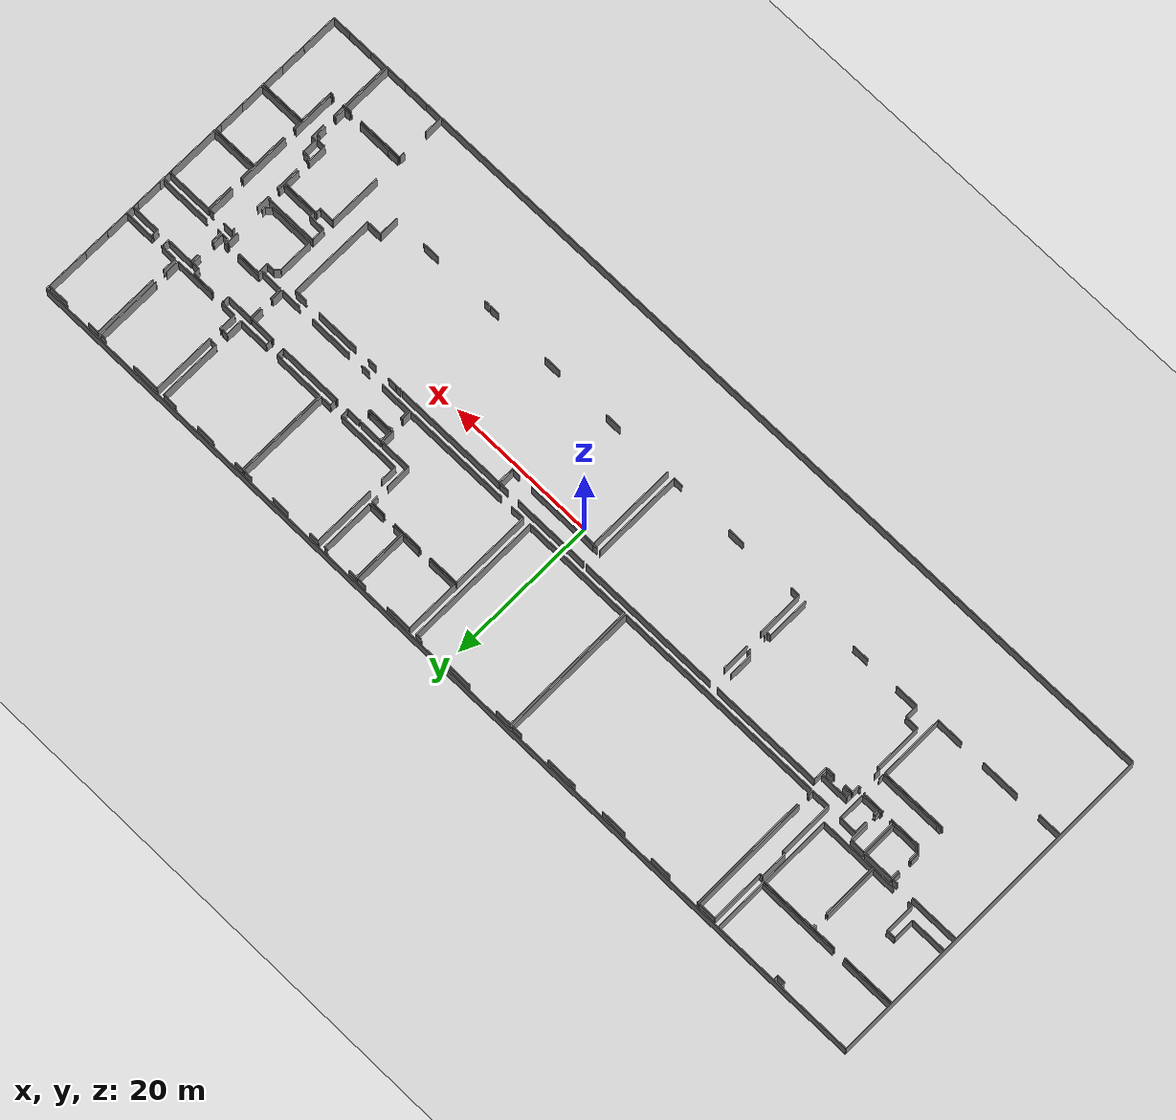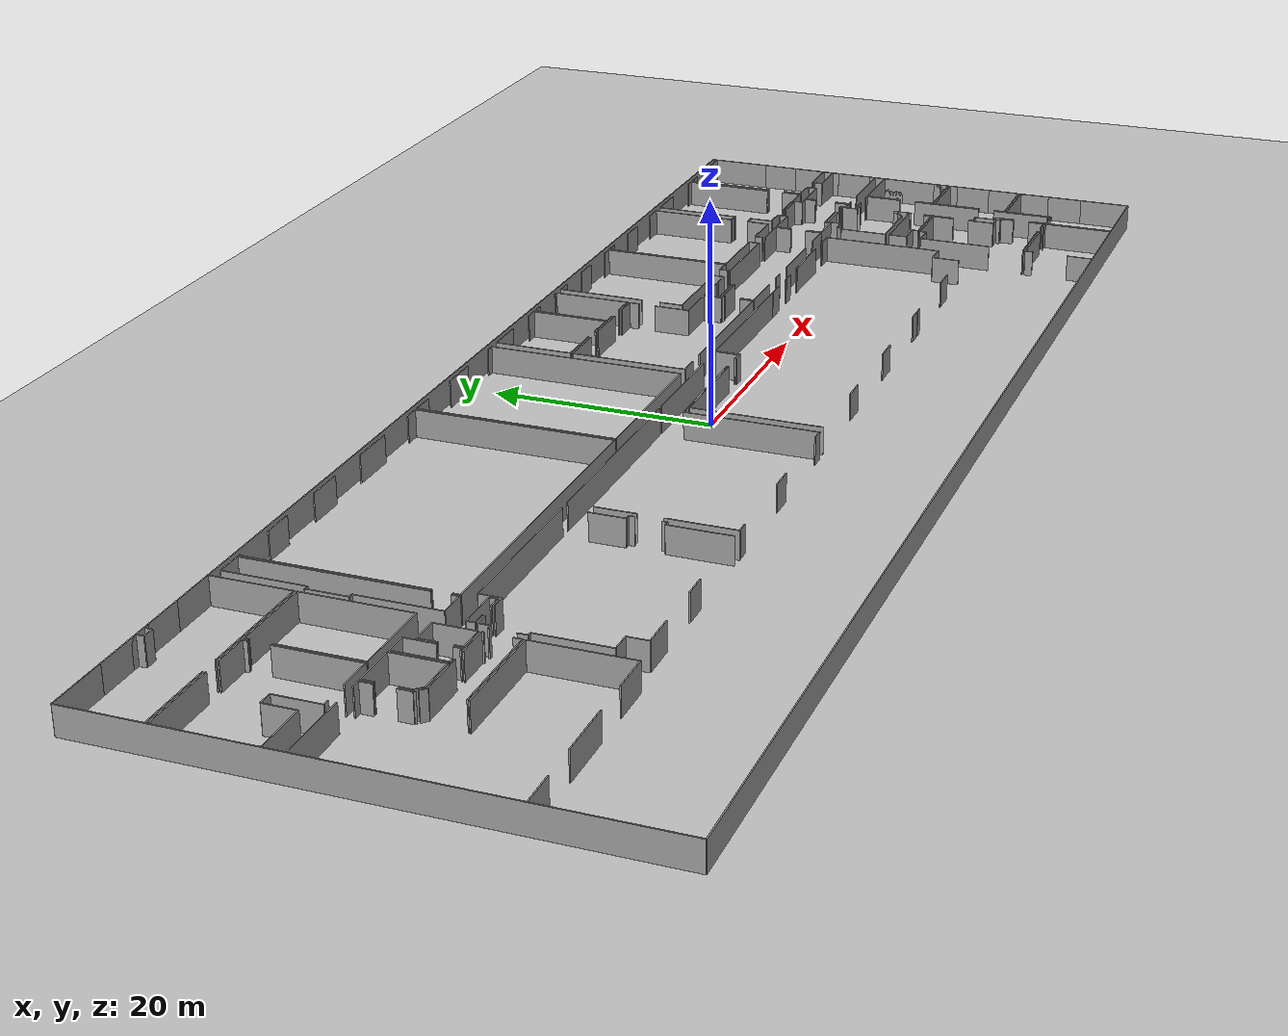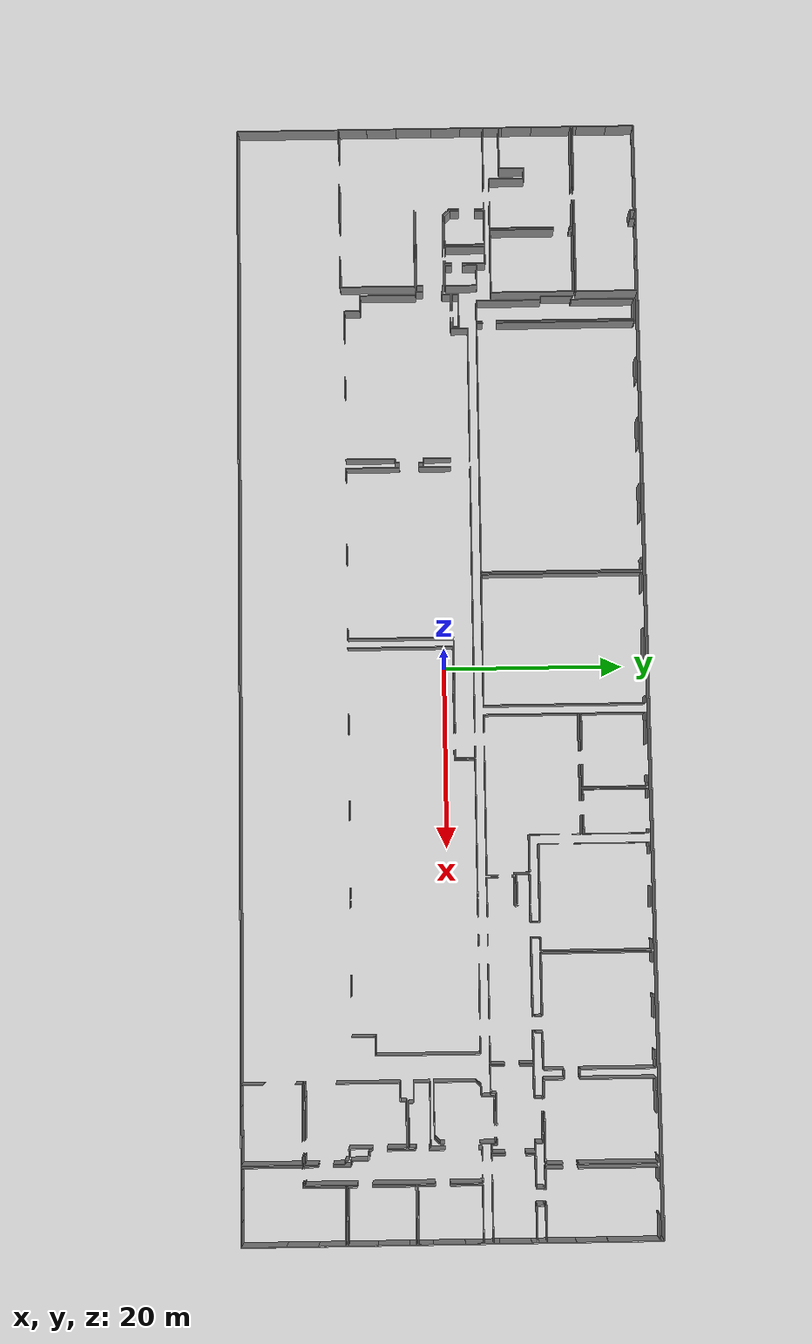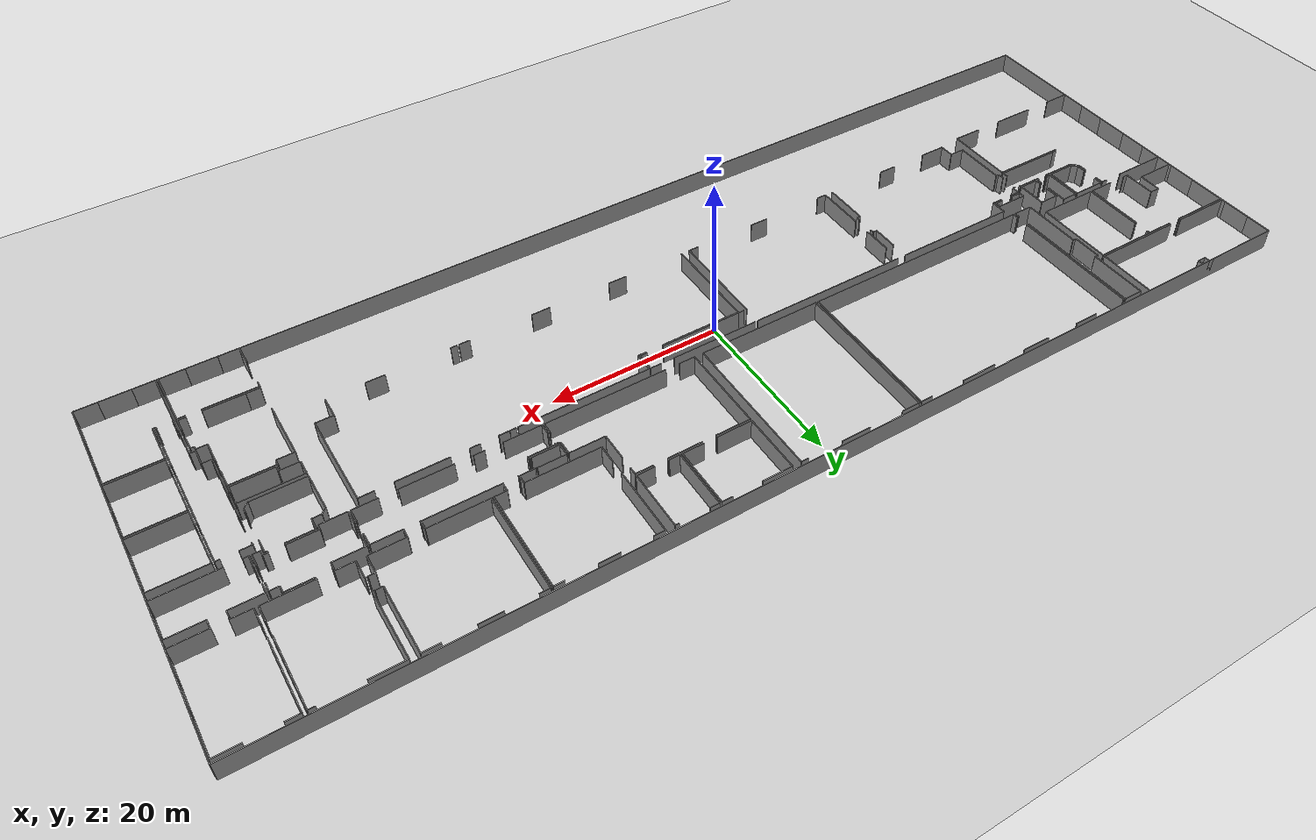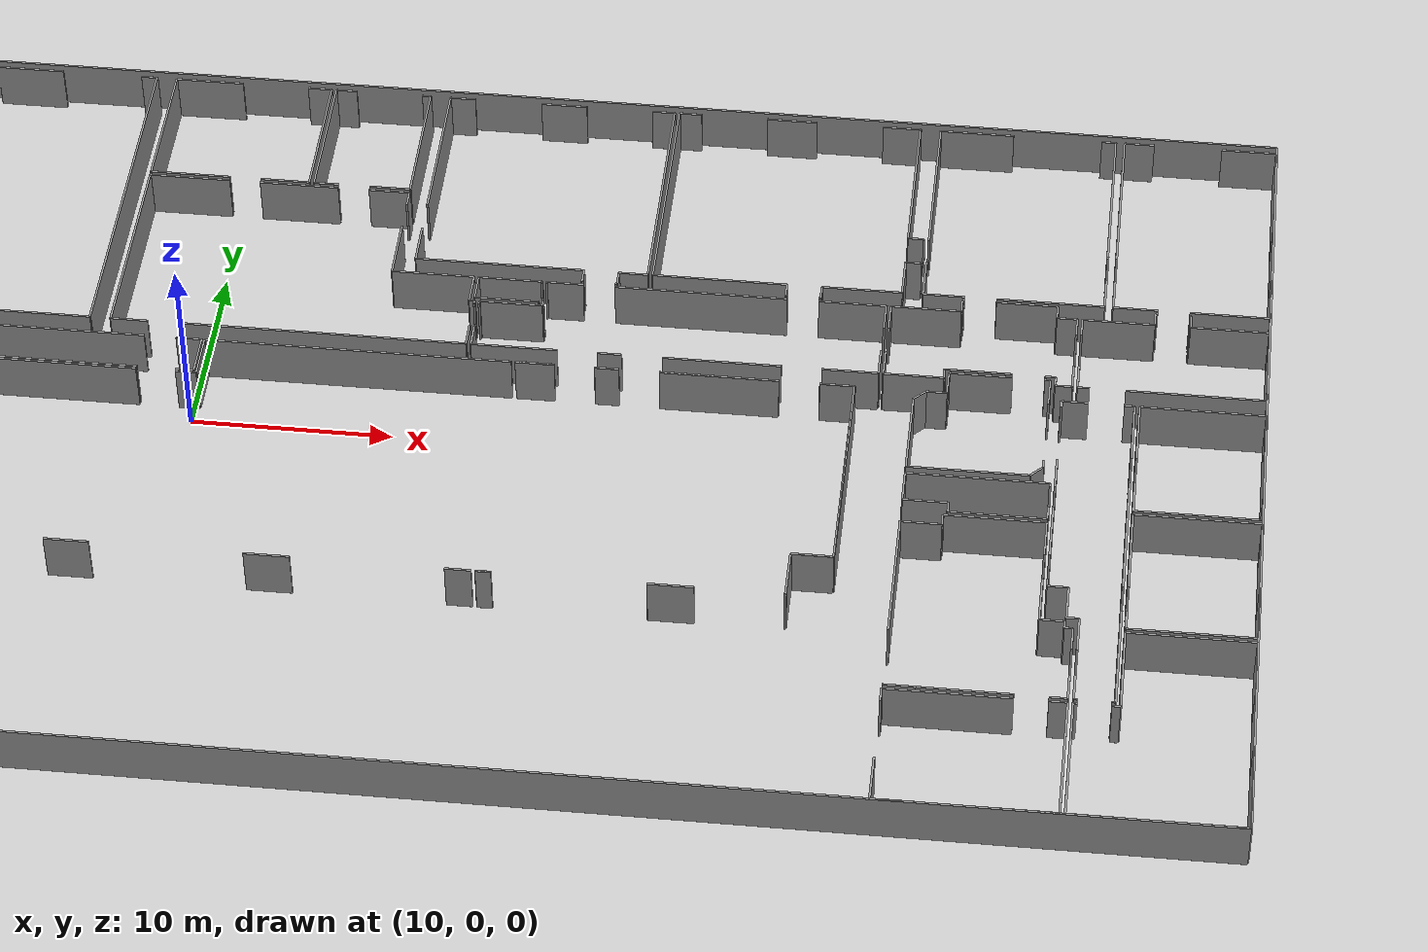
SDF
<sdf version="1.6">
  <world name="default">
    <light name="sun" type="directional">
      <cast_shadows>1</cast_shadows>
      <pose frame="">0 0 10 0 -0 0</pose>
      <diffuse>0.8 0.8 0.8 1</diffuse>
      <specular>0.1 0.1 0.1 1</specular>
      <attenuation>
        <range>1000</range>
        <constant>0.9</constant>
        <linear>0.01</linear>
        <quadratic>0.001</quadratic>
      </attenuation>
      <direction>-0.5 0.5 -1</direction>
    </light>
    <model name="ground_plane">
      <static>1</static>
      <link name="link">
        <collision name="collision">
          <geometry>
            <plane>
              <normal>0 0 1</normal>
              <size>100 100</size>
            </plane>
          </geometry>
          <surface>
            <friction>
              <ode>
                <mu>100</mu>
                <mu2>50</mu2>
              </ode>
              <torsional>
                <ode />
              </torsional>
            </friction>
            <contact>
              <ode />
            </contact>
            <bounce />
          </surface>
          <max_contacts>10</max_contacts>
        </collision>
        <visual name="visual">
          <cast_shadows>0</cast_shadows>
          <geometry>
            <plane>
              <normal>0 0 1</normal>
              <size>100 100</size>
            </plane>
          </geometry>
          <material>
            <script>
              <uri>file://media/materials/scripts/gazebo.material</uri>
              <name>Gazebo/Grey</name>
            </script>
          </material>
        </visual>
        <self_collide>0</self_collide>
        <kinematic>0</kinematic>
        <gravity>1</gravity>
      </link>
    </model>
    <gravity>0 0 -9.8</gravity>
    <magnetic_field>6e-06 2.3e-05 -4.2e-05</magnetic_field>
    <atmosphere type="adiabatic" />
    <physics default="0" name="default_physics" type="ode">
      <max_step_size>0.001</max_step_size>
      <real_time_factor>1</real_time_factor>
      <real_time_update_rate>1000</real_time_update_rate>
    </physics>
    <scene>
      <ambient>0.4 0.4 0.4 1</ambient>
      <background>0.7 0.7 0.7 1</background>
      <shadows>1</shadows>
    </scene>
    <spherical_coordinates>
      <surface_model>EARTH_WGS84</surface_model>
      <latitude_deg>0</latitude_deg>
      <longitude_deg>0</longitude_deg>
      <elevation>0</elevation>
      <heading_deg>0</heading_deg>
    </spherical_coordinates>
  <model name="50010540">
		<static>1</static>
		<link name="Wall_0">
			<collision name="Wall_0_Collision">
				<geometry>
					<box>
						<size>5.65717808411 0.1 2.5</size>
					</box>
				</geometry>
				<pose frame="">2.82858904205 0 1.25 0 0 0</pose>
			</collision>
			<visual name="Wall_0_Visual">
				<pose frame="">2.82858904205 0 1.25 0 0 0</pose>
				<geometry>
					<box>
						<size>5.65717808411 0.1 2.5</size>
					</box>
				</geometry>
				<material>
					<script>
						<uri>file://media/materials/scripts/gazebo.material</uri>
						<name>Gazebo/Grey</name>
					</script>
					<ambient>1 1 1 1</ambient>
				</material>
			</visual>
			<pose frame="">0.0 -0.0 0 0 0 0.0</pose>
		</link>
		<link name="Wall_1">
			<collision name="Wall_1_Collision">
				<geometry>
					<box>
						<size>0.677229308471 0.1 2.5</size>
					</box>
				</geometry>
				<pose frame="">0.338614654236 0 1.25 0 0 0</pose>
			</collision>
			<visual name="Wall_1_Visual">
				<pose frame="">0.338614654236 0 1.25 0 0 0</pose>
				<geometry>
					<box>
						<size>0.677229308471 0.1 2.5</size>
					</box>
				</geometry>
				<material>
					<script>
						<uri>file://media/materials/scripts/gazebo.material</uri>
						<name>Gazebo/Grey</name>
					</script>
					<ambient>1 1 1 1</ambient>
				</material>
			</visual>
			<pose frame="">9.3474931203 -0.0 0 0 0 0.0</pose>
		</link>
		<link name="Wall_2">
			<collision name="Wall_2_Collision">
				<geometry>
					<box>
						<size>0.657527630015 0.1 2.5</size>
					</box>
				</geometry>
				<pose frame="">0.328763815008 0 1.25 0 0 0</pose>
			</collision>
			<visual name="Wall_2_Visual">
				<pose frame="">0.328763815008 0 1.25 0 0 0</pose>
				<geometry>
					<box>
						<size>0.657527630015 0.1 2.5</size>
					</box>
				</geometry>
				<material>
					<script>
						<uri>file://media/materials/scripts/gazebo.material</uri>
						<name>Gazebo/Grey</name>
					</script>
					<ambient>1 1 1 1</ambient>
				</material>
			</visual>
			<pose frame="">10.0247224288 -0.0 0 0 0 -1.57079632679</pose>
		</link>
		<link name="Wall_3">
			<collision name="Wall_3_Collision">
				<geometry>
					<box>
						<size>1.05079855352 0.1 2.5</size>
					</box>
				</geometry>
				<pose frame="">0.525399276758 0 1.25 0 0 0</pose>
			</collision>
			<visual name="Wall_3_Visual">
				<pose frame="">0.525399276758 0 1.25 0 0 0</pose>
				<geometry>
					<box>
						<size>1.05079855352 0.1 2.5</size>
					</box>
				</geometry>
				<material>
					<script>
						<uri>file://media/materials/scripts/gazebo.material</uri>
						<name>Gazebo/Grey</name>
					</script>
					<ambient>1 1 1 1</ambient>
				</material>
			</visual>
			<pose frame="">10.0247224288 -0.657527630015 0 0 0 0.0</pose>
		</link>
		<link name="Wall_4">
			<collision name="Wall_4_Collision">
				<geometry>
					<box>
						<size>0.655621015971 0.1 2.5</size>
					</box>
				</geometry>
				<pose frame="">0.327810507986 0 1.25 0 0 0</pose>
			</collision>
			<visual name="Wall_4_Visual">
				<pose frame="">0.327810507986 0 1.25 0 0 0</pose>
				<geometry>
					<box>
						<size>0.655621015971 0.1 2.5</size>
					</box>
				</geometry>
				<material>
					<script>
						<uri>file://media/materials/scripts/gazebo.material</uri>
						<name>Gazebo/Grey</name>
					</script>
					<ambient>1 1 1 1</ambient>
				</material>
			</visual>
			<pose frame="">11.0755209823 -0.657527630015 0 0 0 1.57079632679</pose>
		</link>
		<link name="Wall_5">
			<collision name="Wall_5_Collision">
				<geometry>
					<box>
						<size>0.505379829294 0.1 2.5</size>
					</box>
				</geometry>
				<pose frame="">0.252689914647 0 1.25 0 0 0</pose>
			</collision>
			<visual name="Wall_5_Visual">
				<pose frame="">0.252689914647 0 1.25 0 0 0</pose>
				<geometry>
					<box>
						<size>0.505379829294 0.1 2.5</size>
					</box>
				</geometry>
				<material>
					<script>
						<uri>file://media/materials/scripts/gazebo.material</uri>
						<name>Gazebo/Grey</name>
					</script>
					<ambient>1 1 1 1</ambient>
				</material>
			</visual>
			<pose frame="">11.0755209823 -0.00190661404412 0 0 0 0.0</pose>
		</link>
		<link name="Wall_6">
			<collision name="Wall_6_Collision">
				<geometry>
					<box>
						<size>4.22378564574 0.1 2.5</size>
					</box>
				</geometry>
				<pose frame="">2.11189282287 0 1.25 0 0 0</pose>
			</collision>
			<visual name="Wall_6_Visual">
				<pose frame="">2.11189282287 0 1.25 0 0 0</pose>
				<geometry>
					<box>
						<size>4.22378564574 0.1 2.5</size>
					</box>
				</geometry>
				<material>
					<script>
						<uri>file://media/materials/scripts/gazebo.material</uri>
						<name>Gazebo/Grey</name>
					</script>
					<ambient>1 1 1 1</ambient>
				</material>
			</visual>
			<pose frame="">15.2966373684 -0.00190661404412 0 0 0 0.0</pose>
		</link>
		<link name="Wall_7">
			<collision name="Wall_7_Collision">
				<geometry>
					<box>
						<size>7.03070284149 0.1 2.5</size>
					</box>
				</geometry>
				<pose frame="">3.51535142075 0 1.25 0 0 0</pose>
			</collision>
			<visual name="Wall_7_Visual">
				<pose frame="">3.51535142075 0 1.25 0 0 0</pose>
				<geometry>
					<box>
						<size>7.03070284149 0.1 2.5</size>
					</box>
				</geometry>
				<material>
					<script>
						<uri>file://media/materials/scripts/gazebo.material</uri>
						<name>Gazebo/Grey</name>
					</script>
					<ambient>1 1 1 1</ambient>
				</material>
			</visual>
			<pose frame="">19.5204230141 -0.00190661404412 0 0 0 -1.57079632679</pose>
		</link>
		<link name="Wall_8">
			<collision name="Wall_8_Collision">
				<geometry>
					<box>
						<size>10.7779620838 0.1 2.5</size>
					</box>
				</geometry>
				<pose frame="">5.3889810419 0 1.25 0 0 0</pose>
			</collision>
			<visual name="Wall_8_Visual">
				<pose frame="">5.3889810419 0 1.25 0 0 0</pose>
				<geometry>
					<box>
						<size>10.7779620838 0.1 2.5</size>
					</box>
				</geometry>
				<material>
					<script>
						<uri>file://media/materials/scripts/gazebo.material</uri>
						<name>Gazebo/Grey</name>
					</script>
					<ambient>1 1 1 1</ambient>
				</material>
			</visual>
			<pose frame="">19.5204230141 -7.03260945553 0 0 0 3.14159265359</pose>
		</link>
		<link name="Wall_9">
			<collision name="Wall_9_Collision">
				<geometry>
					<box>
						<size>7.16035259649 0.1 2.5</size>
					</box>
				</geometry>
				<pose frame="">3.58017629825 0 1.25 0 0 0</pose>
			</collision>
			<visual name="Wall_9_Visual">
				<pose frame="">3.58017629825 0 1.25 0 0 0</pose>
				<geometry>
					<box>
						<size>7.16035259649 0.1 2.5</size>
					</box>
				</geometry>
				<material>
					<script>
						<uri>file://media/materials/scripts/gazebo.material</uri>
						<name>Gazebo/Grey</name>
					</script>
					<ambient>1 1 1 1</ambient>
				</material>
			</visual>
			<pose frame="">7.17204649596 -7.03260945553 0 0 0 3.14159265359</pose>
		</link>
		<link name="Wall_10">
			<collision name="Wall_10_Collision">
				<geometry>
					<box>
						<size>0.500295525177 0.1 2.5</size>
					</box>
				</geometry>
				<pose frame="">0.250147762588 0 1.25 0 0 0</pose>
			</collision>
			<visual name="Wall_10_Visual">
				<pose frame="">0.250147762588 0 1.25 0 0 0</pose>
				<geometry>
					<box>
						<size>0.500295525177 0.1 2.5</size>
					</box>
				</geometry>
				<material>
					<script>
						<uri>file://media/materials/scripts/gazebo.material</uri>
						<name>Gazebo/Grey</name>
					</script>
					<ambient>1 1 1 1</ambient>
				</material>
			</visual>
			<pose frame="">0.0116938994706 -7.03260945553 0 0 0 1.57079632679</pose>
		</link>
		<link name="Wall_11">
			<collision name="Wall_11_Collision">
				<geometry>
					<box>
						<size>3.13830850348 0.1 2.5</size>
					</box>
				</geometry>
				<pose frame="">1.56915425174 0 1.25 0 0 0</pose>
			</collision>
			<visual name="Wall_11_Visual">
				<pose frame="">1.56915425174 0 1.25 0 0 0</pose>
				<geometry>
					<box>
						<size>3.13830850348 0.1 2.5</size>
					</box>
				</geometry>
				<material>
					<script>
						<uri>file://media/materials/scripts/gazebo.material</uri>
						<name>Gazebo/Grey</name>
					</script>
					<ambient>1 1 1 1</ambient>
				</material>
			</visual>
			<pose frame="">0.0116938994706 -3.13828671662 0 0 0 1.57452251449</pose>
		</link>
		<link name="Wall_12">
			<collision name="Wall_12_Collision">
				<geometry>
					<box>
						<size>0.398990765633 0.1 2.5</size>
					</box>
				</geometry>
				<pose frame="">0.199495382816 0 1.25 0 0 0</pose>
			</collision>
			<visual name="Wall_12_Visual">
				<pose frame="">0.199495382816 0 1.25 0 0 0</pose>
				<geometry>
					<box>
						<size>0.398990765633 0.1 2.5</size>
					</box>
				</geometry>
				<material>
					<script>
						<uri>file://media/materials/scripts/gazebo.material</uri>
						<name>Gazebo/Grey</name>
					</script>
					<ambient>1 1 1 1</ambient>
				</material>
			</visual>
			<pose frame="">0.00317769007353 -15.5523778655 0 0 0 1.57079632679</pose>
		</link>
		<link name="Wall_13">
			<collision name="Wall_13_Collision">
				<geometry>
					<box>
						<size>4.48067011128 0.1 2.5</size>
					</box>
				</geometry>
				<pose frame="">2.24033505564 0 1.25 0 0 0</pose>
			</collision>
			<visual name="Wall_13_Visual">
				<pose frame="">2.24033505564 0 1.25 0 0 0</pose>
				<geometry>
					<box>
						<size>4.48067011128 0.1 2.5</size>
					</box>
				</geometry>
				<material>
					<script>
						<uri>file://media/materials/scripts/gazebo.material</uri>
						<name>Gazebo/Grey</name>
					</script>
					<ambient>1 1 1 1</ambient>
				</material>
			</visual>
			<pose frame="">0.00317769007353 -11.7484286323 0 0 0 1.57079632679</pose>
		</link>
		<link name="Wall_14">
			<collision name="Wall_14_Collision">
				<geometry>
					<box>
						<size>7.1736988948 0.1 2.5</size>
					</box>
				</geometry>
				<pose frame="">3.5868494474 0 1.25 0 0 0</pose>
			</collision>
			<visual name="Wall_14_Visual">
				<pose frame="">3.5868494474 0 1.25 0 0 0</pose>
				<geometry>
					<box>
						<size>7.1736988948 0.1 2.5</size>
					</box>
				</geometry>
				<material>
					<script>
						<uri>file://media/materials/scripts/gazebo.material</uri>
						<name>Gazebo/Grey</name>
					</script>
					<ambient>1 1 1 1</ambient>
				</material>
			</visual>
			<pose frame="">0.00317769007353 -7.26775852098 0 0 0 0.0</pose>
		</link>
		<link name="Wall_15">
			<collision name="Wall_15_Collision">
				<geometry>
					<box>
						<size>3.19052794143 0.1 2.5</size>
					</box>
				</geometry>
				<pose frame="">1.59526397071 0 1.25 0 0 0</pose>
			</collision>
			<visual name="Wall_15_Visual">
				<pose frame="">1.59526397071 0 1.25 0 0 0</pose>
				<geometry>
					<box>
						<size>3.19052794143 0.1 2.5</size>
					</box>
				</geometry>
				<material>
					<script>
						<uri>file://media/materials/scripts/gazebo.material</uri>
						<name>Gazebo/Grey</name>
					</script>
					<ambient>1 1 1 1</ambient>
				</material>
			</visual>
			<pose frame="">8.74640126599 -7.26775852098 0 0 0 0.0</pose>
		</link>
		<link name="Wall_16">
			<collision name="Wall_16_Collision">
				<geometry>
					<box>
						<size>0.393906461515 0.1 2.5</size>
					</box>
				</geometry>
				<pose frame="">0.196953230757 0 1.25 0 0 0</pose>
			</collision>
			<visual name="Wall_16_Visual">
				<pose frame="">0.196953230757 0 1.25 0 0 0</pose>
				<geometry>
					<box>
						<size>0.393906461515 0.1 2.5</size>
					</box>
				</geometry>
				<material>
					<script>
						<uri>file://media/materials/scripts/gazebo.material</uri>
						<name>Gazebo/Grey</name>
					</script>
					<ambient>1 1 1 1</ambient>
				</material>
			</visual>
			<pose frame="">11.9369292074 -7.26775852098 0 0 0 -1.57079632679</pose>
		</link>
		<link name="Wall_17">
			<collision name="Wall_17_Collision">
				<geometry>
					<box>
						<size>7.28936681348 0.1 2.5</size>
					</box>
				</geometry>
				<pose frame="">3.64468340674 0 1.25 0 0 0</pose>
			</collision>
			<visual name="Wall_17_Visual">
				<pose frame="">3.64468340674 0 1.25 0 0 0</pose>
				<geometry>
					<box>
						<size>7.28936681348 0.1 2.5</size>
					</box>
				</geometry>
				<material>
					<script>
						<uri>file://media/materials/scripts/gazebo.material</uri>
						<name>Gazebo/Grey</name>
					</script>
					<ambient>1 1 1 1</ambient>
				</material>
			</visual>
			<pose frame="">11.9369292074 -9.44867077224 0 0 0 -1.57079632679</pose>
		</link>
		<link name="Wall_18">
			<collision name="Wall_18_Collision">
				<geometry>
					<box>
						<size>3.09290930237 0.1 2.5</size>
					</box>
				</geometry>
				<pose frame="">1.54645465118 0 1.25 0 0 0</pose>
			</collision>
			<visual name="Wall_18_Visual">
				<pose frame="">1.54645465118 0 1.25 0 0 0</pose>
				<geometry>
					<box>
						<size>3.09290930237 0.1 2.5</size>
					</box>
				</geometry>
				<material>
					<script>
						<uri>file://media/materials/scripts/gazebo.material</uri>
						<name>Gazebo/Grey</name>
					</script>
					<ambient>1 1 1 1</ambient>
				</material>
			</visual>
			<pose frame="">11.9369292074 -16.7380375857 0 0 0 3.14159265359</pose>
		</link>
		<link name="Wall_19">
			<collision name="Wall_19_Collision">
				<geometry>
					<box>
						<size>0.572365536045 0.1 2.5</size>
					</box>
				</geometry>
				<pose frame="">0.286182768022 0 1.25 0 0 0</pose>
			</collision>
			<visual name="Wall_19_Visual">
				<pose frame="">0.286182768022 0 1.25 0 0 0</pose>
				<geometry>
					<box>
						<size>0.572365536045 0.1 2.5</size>
					</box>
				</geometry>
				<material>
					<script>
						<uri>file://media/materials/scripts/gazebo.material</uri>
						<name>Gazebo/Grey</name>
					</script>
					<ambient>1 1 1 1</ambient>
				</material>
			</visual>
			<pose frame="">6.6550998748 -16.7380375857 0 0 0 3.14159265359</pose>
		</link>
		<link name="Wall_20">
			<collision name="Wall_20_Collision">
				<geometry>
					<box>
						<size>3.99766122011 0.1 2.5</size>
					</box>
				</geometry>
				<pose frame="">1.99883061005 0 1.25 0 0 0</pose>
			</collision>
			<visual name="Wall_20_Visual">
				<pose frame="">1.99883061005 0 1.25 0 0 0</pose>
				<geometry>
					<box>
						<size>3.99766122011 0.1 2.5</size>
					</box>
				</geometry>
				<material>
					<script>
						<uri>file://media/materials/scripts/gazebo.material</uri>
						<name>Gazebo/Grey</name>
					</script>
					<ambient>1 1 1 1</ambient>
				</material>
			</visual>
			<pose frame="">6.08273433875 -16.7380375857 0 0 0 1.57079632679</pose>
		</link>
		<link name="Wall_21">
			<collision name="Wall_21_Collision">
				<geometry>
					<box>
						<size>1.2315455649 0.1 2.5</size>
					</box>
				</geometry>
				<pose frame="">0.615772782449 0 1.25 0 0 0</pose>
			</collision>
			<visual name="Wall_21_Visual">
				<pose frame="">0.615772782449 0 1.25 0 0 0</pose>
				<geometry>
					<box>
						<size>1.2315455649 0.1 2.5</size>
					</box>
				</geometry>
				<material>
					<script>
						<uri>file://media/materials/scripts/gazebo.material</uri>
						<name>Gazebo/Grey</name>
					</script>
					<ambient>1 1 1 1</ambient>
				</material>
			</visual>
			<pose frame="">6.08273433875 -12.7403763656 0 0 0 3.14159265359</pose>
		</link>
		<link name="Wall_22">
			<collision name="Wall_22_Collision">
				<geometry>
					<box>
						<size>2.80157867643 0.1 2.5</size>
					</box>
				</geometry>
				<pose frame="">1.40078933821 0 1.25 0 0 0</pose>
			</collision>
			<visual name="Wall_22_Visual">
				<pose frame="">1.40078933821 0 1.25 0 0 0</pose>
				<geometry>
					<box>
						<size>2.80157867643 0.1 2.5</size>
					</box>
				</geometry>
				<material>
					<script>
						<uri>file://media/materials/scripts/gazebo.material</uri>
						<name>Gazebo/Grey</name>
					</script>
					<ambient>1 1 1 1</ambient>
				</material>
			</visual>
			<pose frame="">4.85118877386 -12.7403763656 0 0 0 -1.57079632679</pose>
		</link>
		<link name="Wall_23">
			<collision name="Wall_23_Collision">
				<geometry>
					<box>
						<size>4.84802228787 0.1 2.5</size>
					</box>
				</geometry>
				<pose frame="">2.42401114394 0 1.25 0 0 0</pose>
			</collision>
			<visual name="Wall_23_Visual">
				<pose frame="">2.42401114394 0 1.25 0 0 0</pose>
				<geometry>
					<box>
						<size>4.84802228787 0.1 2.5</size>
					</box>
				</geometry>
				<material>
					<script>
						<uri>file://media/materials/scripts/gazebo.material</uri>
						<name>Gazebo/Grey</name>
					</script>
					<ambient>1 1 1 1</ambient>
				</material>
			</visual>
			<pose frame="">4.85118877386 -15.541955042 0 0 0 -3.13944273949</pose>
		</link>
		<link name="Wall_24">
			<collision name="Wall_24_Collision">
				<geometry>
					<box>
						<size>7.29864566849 0.1 2.5</size>
					</box>
				</geometry>
				<pose frame="">3.64932283425 0 1.25 0 0 0</pose>
			</collision>
			<visual name="Wall_24_Visual">
				<pose frame="">3.64932283425 0 1.25 0 0 0</pose>
				<geometry>
					<box>
						<size>7.29864566849 0.1 2.5</size>
					</box>
				</geometry>
				<material>
					<script>
						<uri>file://media/materials/scripts/gazebo.material</uri>
						<name>Gazebo/Grey</name>
					</script>
					<ambient>1 1 1 1</ambient>
				</material>
			</visual>
			<pose frame="">12.1536476704 -16.7415965986 0 0 0 1.57079632679</pose>
		</link>
		<link name="Wall_25">
			<collision name="Wall_25_Collision">
				<geometry>
					<box>
						<size>0.386534220544 0.1 2.5</size>
					</box>
				</geometry>
				<pose frame="">0.193267110272 0 1.25 0 0 0</pose>
			</collision>
			<visual name="Wall_25_Visual">
				<pose frame="">0.193267110272 0 1.25 0 0 0</pose>
				<geometry>
					<box>
						<size>0.386534220544 0.1 2.5</size>
					</box>
				</geometry>
				<material>
					<script>
						<uri>file://media/materials/scripts/gazebo.material</uri>
						<name>Gazebo/Grey</name>
					</script>
					<ambient>1 1 1 1</ambient>
				</material>
			</visual>
			<pose frame="">12.1536476704 -7.65365720351 0 0 0 1.57079632679</pose>
		</link>
		<link name="Wall_26">
			<collision name="Wall_26_Collision">
				<geometry>
					<box>
						<size>7.3639789764 0.1 2.5</size>
					</box>
				</geometry>
				<pose frame="">3.6819894882 0 1.25 0 0 0</pose>
			</collision>
			<visual name="Wall_26_Visual">
				<pose frame="">3.6819894882 0 1.25 0 0 0</pose>
				<geometry>
					<box>
						<size>7.3639789764 0.1 2.5</size>
					</box>
				</geometry>
				<material>
					<script>
						<uri>file://media/materials/scripts/gazebo.material</uri>
						<name>Gazebo/Grey</name>
					</script>
					<ambient>1 1 1 1</ambient>
				</material>
			</visual>
			<pose frame="">12.1536476704 -7.26712298296 0 0 0 0.0</pose>
		</link>
		<link name="Wall_27">
			<collision name="Wall_27_Collision">
				<geometry>
					<box>
						<size>9.47917659695 0.1 2.5</size>
					</box>
				</geometry>
				<pose frame="">4.73958829847 0 1.25 0 0 0</pose>
			</collision>
			<visual name="Wall_27_Visual">
				<pose frame="">4.73958829847 0 1.25 0 0 0</pose>
				<geometry>
					<box>
						<size>9.47917659695 0.1 2.5</size>
					</box>
				</geometry>
				<material>
					<script>
						<uri>file://media/materials/scripts/gazebo.material</uri>
						<name>Gazebo/Grey</name>
					</script>
					<ambient>1 1 1 1</ambient>
				</material>
			</visual>
			<pose frame="">19.5176266468 -7.26712298296 0 0 0 -1.57079632679</pose>
		</link>
		<link name="Wall_28">
			<collision name="Wall_28_Collision">
				<geometry>
					<box>
						<size>7.36398047817 0.1 2.5</size>
					</box>
				</geometry>
				<pose frame="">3.68199023909 0 1.25 0 0 0</pose>
			</collision>
			<visual name="Wall_28_Visual">
				<pose frame="">3.68199023909 0 1.25 0 0 0</pose>
				<geometry>
					<box>
						<size>7.36398047817 0.1 2.5</size>
					</box>
				</geometry>
				<material>
					<script>
						<uri>file://media/materials/scripts/gazebo.material</uri>
						<name>Gazebo/Grey</name>
					</script>
					<ambient>1 1 1 1</ambient>
				</material>
			</visual>
			<pose frame="">19.5176266468 -16.7462995799 0 0 0 3.14095400692</pose>
		</link>
		<link name="Wall_29">
			<collision name="Wall_29_Collision">
				<geometry>
					<box>
						<size>3.23654089369 0.1 2.5</size>
					</box>
				</geometry>
				<pose frame="">1.61827044685 0 1.25 0 0 0</pose>
			</collision>
			<visual name="Wall_29_Visual">
				<pose frame="">1.61827044685 0 1.25 0 0 0</pose>
				<geometry>
					<box>
						<size>3.23654089369 0.1 2.5</size>
					</box>
				</geometry>
				<material>
					<script>
						<uri>file://media/materials/scripts/gazebo.material</uri>
						<name>Gazebo/Grey</name>
					</script>
					<ambient>1 1 1 1</ambient>
				</material>
			</visual>
			<pose frame="">0.00228793685294 -33.9973434511 0 0 0 1.57079632679</pose>
		</link>
		<link name="Wall_30">
			<collision name="Wall_30_Collision">
				<geometry>
					<box>
						<size>4.01380388568 0.1 2.5</size>
					</box>
				</geometry>
				<pose frame="">2.00690194284 0 1.25 0 0 0</pose>
			</collision>
			<visual name="Wall_30_Visual">
				<pose frame="">2.00690194284 0 1.25 0 0 0</pose>
				<geometry>
					<box>
						<size>4.01380388568 0.1 2.5</size>
					</box>
				</geometry>
				<material>
					<script>
						<uri>file://media/materials/scripts/gazebo.material</uri>
						<name>Gazebo/Grey</name>
					</script>
					<ambient>1 1 1 1</ambient>
				</material>
			</visual>
			<pose frame="">0.00228793685294 -27.3610555015 0 0 0 1.57079632679</pose>
		</link>
		<link name="Wall_31">
			<collision name="Wall_31_Collision">
				<geometry>
					<box>
						<size>2.57634400402 0.1 2.5</size>
					</box>
				</geometry>
				<pose frame="">1.28817200201 0 1.25 0 0 0</pose>
			</collision>
			<visual name="Wall_31_Visual">
				<pose frame="">1.28817200201 0 1.25 0 0 0</pose>
				<geometry>
					<box>
						<size>2.57634400402 0.1 2.5</size>
					</box>
				</geometry>
				<material>
					<script>
						<uri>file://media/materials/scripts/gazebo.material</uri>
						<name>Gazebo/Grey</name>
					</script>
					<ambient>1 1 1 1</ambient>
				</material>
			</visual>
			<pose frame="">0.00228793685294 -19.9604695355 0 0 0 1.57079632679</pose>
		</link>
		<link name="Wall_32">
			<collision name="Wall_32_Collision">
				<geometry>
					<box>
						<size>6.66094682453 0.1 2.5</size>
					</box>
				</geometry>
				<pose frame="">3.33047341227 0 1.25 0 0 0</pose>
			</collision>
			<visual name="Wall_32_Visual">
				<pose frame="">3.33047341227 0 1.25 0 0 0</pose>
				<geometry>
					<box>
						<size>6.66094682453 0.1 2.5</size>
					</box>
				</geometry>
				<material>
					<script>
						<uri>file://media/materials/scripts/gazebo.material</uri>
						<name>Gazebo/Grey</name>
					</script>
					<ambient>1 1 1 1</ambient>
				</material>
			</visual>
			<pose frame="">0.00228793685294 -17.3841255315 0 0 0 0.0</pose>
		</link>
		<link name="Wall_33">
			<collision name="Wall_33_Collision">
				<geometry>
					<box>
						<size>0.750697502971 0.1 2.5</size>
					</box>
				</geometry>
				<pose frame="">0.375348751486 0 1.25 0 0 0</pose>
			</collision>
			<visual name="Wall_33_Visual">
				<pose frame="">0.375348751486 0 1.25 0 0 0</pose>
				<geometry>
					<box>
						<size>0.750697502971 0.1 2.5</size>
					</box>
				</geometry>
				<material>
					<script>
						<uri>file://media/materials/scripts/gazebo.material</uri>
						<name>Gazebo/Grey</name>
					</script>
					<ambient>1 1 1 1</ambient>
				</material>
			</visual>
			<pose frame="">8.86664505837 -17.3841255315 0 0 0 0.0</pose>
		</link>
		<link name="Wall_34">
			<collision name="Wall_34_Collision">
				<geometry>
					<box>
						<size>1.08816818878 0.1 2.5</size>
					</box>
				</geometry>
				<pose frame="">0.54408409439 0 1.25 0 0 0</pose>
			</collision>
			<visual name="Wall_34_Visual">
				<pose frame="">0.54408409439 0 1.25 0 0 0</pose>
				<geometry>
					<box>
						<size>1.08816818878 0.1 2.5</size>
					</box>
				</geometry>
				<material>
					<script>
						<uri>file://media/materials/scripts/gazebo.material</uri>
						<name>Gazebo/Grey</name>
					</script>
					<ambient>1 1 1 1</ambient>
				</material>
			</visual>
			<pose frame="">9.61734256135 -17.3841255315 0 0 0 -1.57079632679</pose>
		</link>
		<link name="Wall_35">
			<collision name="Wall_35_Collision">
				<geometry>
					<box>
						<size>1.21387760809 0.1 2.5</size>
					</box>
				</geometry>
				<pose frame="">0.606938804045 0 1.25 0 0 0</pose>
			</collision>
			<visual name="Wall_35_Visual">
				<pose frame="">0.606938804045 0 1.25 0 0 0</pose>
				<geometry>
					<box>
						<size>1.21387760809 0.1 2.5</size>
					</box>
				</geometry>
				<material>
					<script>
						<uri>file://media/materials/scripts/gazebo.material</uri>
						<name>Gazebo/Grey</name>
					</script>
					<ambient>1 1 1 1</ambient>
				</material>
			</visual>
			<pose frame="">9.61734256135 -20.2357846035 0 0 0 -1.57079632679</pose>
		</link>
		<link name="Wall_36">
			<collision name="Wall_36_Collision">
				<geometry>
					<box>
						<size>0.174644412543 0.1 2.5</size>
					</box>
				</geometry>
				<pose frame="">0.0873222062716 0 1.25 0 0 0</pose>
			</collision>
			<visual name="Wall_36_Visual">
				<pose frame="">0.0873222062716 0 1.25 0 0 0</pose>
				<geometry>
					<box>
						<size>0.174644412543 0.1 2.5</size>
					</box>
				</geometry>
				<material>
					<script>
						<uri>file://media/materials/scripts/gazebo.material</uri>
						<name>Gazebo/Grey</name>
					</script>
					<ambient>1 1 1 1</ambient>
				</material>
			</visual>
			<pose frame="">9.61734256135 -21.4496622115 0 0 0 -0.796205771407</pose>
		</link>
		<link name="Wall_37">
			<collision name="Wall_37_Collision">
				<geometry>
					<box>
						<size>8.90706527611 0.1 2.5</size>
					</box>
				</geometry>
				<pose frame="">4.45353263805 0 1.25 0 0 0</pose>
			</collision>
			<visual name="Wall_37_Visual">
				<pose frame="">4.45353263805 0 1.25 0 0 0</pose>
				<geometry>
					<box>
						<size>8.90706527611 0.1 2.5</size>
					</box>
				</geometry>
				<material>
					<script>
						<uri>file://media/materials/scripts/gazebo.material</uri>
						<name>Gazebo/Grey</name>
					</script>
					<ambient>1 1 1 1</ambient>
				</material>
			</visual>
			<pose frame="">9.73949296777 -25.4635932048 0 0 0 0.0</pose>
		</link>
		<link name="Wall_38">
			<collision name="Wall_38_Collision">
				<geometry>
					<box>
						<size>8.51608228946 0.1 2.5</size>
					</box>
				</geometry>
				<pose frame="">4.25804114473 0 1.25 0 0 0</pose>
			</collision>
			<visual name="Wall_38_Visual">
				<pose frame="">4.25804114473 0 1.25 0 0 0</pose>
				<geometry>
					<box>
						<size>8.51608228946 0.1 2.5</size>
					</box>
				</geometry>
				<material>
					<script>
						<uri>file://media/materials/scripts/gazebo.material</uri>
						<name>Gazebo/Grey</name>
					</script>
					<ambient>1 1 1 1</ambient>
				</material>
			</visual>
			<pose frame="">18.6465582439 -25.4635932048 0 0 0 -1.57079632679</pose>
		</link>
		<link name="Wall_39">
			<collision name="Wall_39_Collision">
				<geometry>
					<box>
						<size>3.60947460072 0.1 2.5</size>
					</box>
				</geometry>
				<pose frame="">1.80473730036 0 1.25 0 0 0</pose>
			</collision>
			<visual name="Wall_39_Visual">
				<pose frame="">1.80473730036 0 1.25 0 0 0</pose>
				<geometry>
					<box>
						<size>3.60947460072 0.1 2.5</size>
					</box>
				</geometry>
				<material>
					<script>
						<uri>file://media/materials/scripts/gazebo.material</uri>
						<name>Gazebo/Grey</name>
					</script>
					<ambient>1 1 1 1</ambient>
				</material>
			</visual>
			<pose frame="">18.6465582439 -33.9796754943 0 0 0 3.14159265359</pose>
		</link>
		<link name="Wall_40">
			<collision name="Wall_40_Collision">
				<geometry>
					<box>
						<size>5.2374687792 0.1 2.5</size>
					</box>
				</geometry>
				<pose frame="">2.6187343896 0 1.25 0 0 0</pose>
			</collision>
			<visual name="Wall_40_Visual">
				<pose frame="">2.6187343896 0 1.25 0 0 0</pose>
				<geometry>
					<box>
						<size>5.2374687792 0.1 2.5</size>
					</box>
				</geometry>
				<material>
					<script>
						<uri>file://media/materials/scripts/gazebo.material</uri>
						<name>Gazebo/Grey</name>
					</script>
					<ambient>1 1 1 1</ambient>
				</material>
			</visual>
			<pose frame="">11.7381329164 -33.9796754943 0 0 0 3.14159265359</pose>
		</link>
		<link name="Wall_41">
			<collision name="Wall_41_Collision">
				<geometry>
					<box>
						<size>3.21599799424 0.1 2.5</size>
					</box>
				</geometry>
				<pose frame="">1.60799899712 0 1.25 0 0 0</pose>
			</collision>
			<visual name="Wall_41_Visual">
				<pose frame="">1.60799899712 0 1.25 0 0 0</pose>
				<geometry>
					<box>
						<size>3.21599799424 0.1 2.5</size>
					</box>
				</geometry>
				<material>
					<script>
						<uri>file://media/materials/scripts/gazebo.material</uri>
						<name>Gazebo/Grey</name>
					</script>
					<ambient>1 1 1 1</ambient>
				</material>
			</visual>
			<pose frame="">3.21823739887 -33.9796754943 0 0 0 -3.13609885486</pose>
		</link>
		<link name="Wall_42">
			<collision name="Wall_42_Collision">
				<geometry>
					<box>
						<size>3.95965604683 0.1 2.5</size>
					</box>
				</geometry>
				<pose frame="">1.97982802341 0 1.25 0 0 0</pose>
			</collision>
			<visual name="Wall_42_Visual">
				<pose frame="">1.97982802341 0 1.25 0 0 0</pose>
				<geometry>
					<box>
						<size>3.95965604683 0.1 2.5</size>
					</box>
				</geometry>
				<material>
					<script>
						<uri>file://media/materials/scripts/gazebo.material</uri>
						<name>Gazebo/Grey</name>
					</script>
					<ambient>1 1 1 1</ambient>
				</material>
			</visual>
			<pose frame="">9.86787164674 -17.3780243665 0 0 0 0.0</pose>
		</link>
		<link name="Wall_43">
			<collision name="Wall_43_Collision">
				<geometry>
					<box>
						<size>4.5593497175 0.1 2.5</size>
					</box>
				</geometry>
				<pose frame="">2.27967485875 0 1.25 0 0 0</pose>
			</collision>
			<visual name="Wall_43_Visual">
				<pose frame="">2.27967485875 0 1.25 0 0 0</pose>
				<geometry>
					<box>
						<size>4.5593497175 0.1 2.5</size>
					</box>
				</geometry>
				<material>
					<script>
						<uri>file://media/materials/scripts/gazebo.material</uri>
						<name>Gazebo/Grey</name>
					</script>
					<ambient>1 1 1 1</ambient>
				</material>
			</visual>
			<pose frame="">13.8275276936 -17.3780243665 0 0 0 -1.57079632679</pose>
		</link>
		<link name="Wall_44">
			<collision name="Wall_44_Collision">
				<geometry>
					<box>
						<size>3.35907262293 0.1 2.5</size>
					</box>
				</geometry>
				<pose frame="">1.67953631146 0 1.25 0 0 0</pose>
			</collision>
			<visual name="Wall_44_Visual">
				<pose frame="">1.67953631146 0 1.25 0 0 0</pose>
				<geometry>
					<box>
						<size>3.35907262293 0.1 2.5</size>
					</box>
				</geometry>
				<material>
					<script>
						<uri>file://media/materials/scripts/gazebo.material</uri>
						<name>Gazebo/Grey</name>
					</script>
					<ambient>1 1 1 1</ambient>
				</material>
			</visual>
			<pose frame="">13.8275276936 -21.937374084 0 0 0 3.14159265359</pose>
		</link>
		<link name="Wall_45">
			<collision name="Wall_45_Collision">
				<geometry>
					<box>
						<size>0.865820725998 0.1 2.5</size>
					</box>
				</geometry>
				<pose frame="">0.432910362999 0 1.25 0 0 0</pose>
			</collision>
			<visual name="Wall_45_Visual">
				<pose frame="">0.432910362999 0 1.25 0 0 0</pose>
				<geometry>
					<box>
						<size>0.865820725998 0.1 2.5</size>
					</box>
				</geometry>
				<material>
					<script>
						<uri>file://media/materials/scripts/gazebo.material</uri>
						<name>Gazebo/Grey</name>
					</script>
					<ambient>1 1 1 1</ambient>
				</material>
			</visual>
			<pose frame="">10.4684550706 -21.937374084 0 0 0 2.34944695427</pose>
		</link>
		<link name="Wall_46">
			<collision name="Wall_46_Collision">
				<geometry>
					<box>
						<size>1.07774536534 0.1 2.5</size>
					</box>
				</geometry>
				<pose frame="">0.53887268267 0 1.25 0 0 0</pose>
			</collision>
			<visual name="Wall_46_Visual">
				<pose frame="">0.53887268267 0 1.25 0 0 0</pose>
				<geometry>
					<box>
						<size>1.07774536534 0.1 2.5</size>
					</box>
				</geometry>
				<material>
					<script>
						<uri>file://media/materials/scripts/gazebo.material</uri>
						<name>Gazebo/Grey</name>
					</script>
					<ambient>1 1 1 1</ambient>
				</material>
			</visual>
			<pose frame="">9.86037229817 -21.3210293174 0 0 0 1.57079632679</pose>
		</link>
		<link name="Wall_47">
			<collision name="Wall_47_Collision">
				<geometry>
					<box>
						<size>1.08069486092 0.1 2.5</size>
					</box>
				</geometry>
				<pose frame="">0.540347430461 0 1.25 0 0 0</pose>
			</collision>
			<visual name="Wall_47_Visual">
				<pose frame="">0.540347430461 0 1.25 0 0 0</pose>
				<geometry>
					<box>
						<size>1.08069486092 0.1 2.5</size>
					</box>
				</geometry>
				<material>
					<script>
						<uri>file://media/materials/scripts/gazebo.material</uri>
						<name>Gazebo/Grey</name>
					</script>
					<ambient>1 1 1 1</ambient>
				</material>
			</visual>
			<pose frame="">9.86037229817 -18.4586932067 0 0 0 1.56385689455</pose>
		</link>
		<link name="Wall_48">
			<collision name="Wall_48_Collision">
				<geometry>
					<box>
						<size>0.546435585045 0.1 2.5</size>
					</box>
				</geometry>
				<pose frame="">0.273217792522 0 1.25 0 0 0</pose>
			</collision>
			<visual name="Wall_48_Visual">
				<pose frame="">0.273217792522 0 1.25 0 0 0</pose>
				<geometry>
					<box>
						<size>0.546435585045 0.1 2.5</size>
					</box>
				</geometry>
				<material>
					<script>
						<uri>file://media/materials/scripts/gazebo.material</uri>
						<name>Gazebo/Grey</name>
					</script>
					<ambient>1 1 1 1</ambient>
				</material>
			</visual>
			<pose frame="">10.4307041126 -25.2600939325 0 0 0 3.14159265359</pose>
		</link>
		<link name="Wall_49">
			<collision name="Wall_49_Collision">
				<geometry>
					<box>
						<size>0.655086307743 0.1 2.5</size>
					</box>
				</geometry>
				<pose frame="">0.327543153871 0 1.25 0 0 0</pose>
			</collision>
			<visual name="Wall_49_Visual">
				<pose frame="">0.327543153871 0 1.25 0 0 0</pose>
				<geometry>
					<box>
						<size>0.655086307743 0.1 2.5</size>
					</box>
				</geometry>
				<material>
					<script>
						<uri>file://media/materials/scripts/gazebo.material</uri>
						<name>Gazebo/Grey</name>
					</script>
					<ambient>1 1 1 1</ambient>
				</material>
			</visual>
			<pose frame="">9.88426852752 -21.7028605566 0 0 0 -0.764679295178</pose>
		</link>
		<link name="Wall_50">
			<collision name="Wall_50_Collision">
				<geometry>
					<box>
						<size>4.13086998799 0.1 2.5</size>
					</box>
				</geometry>
				<pose frame="">2.06543499399 0 1.25 0 0 0</pose>
			</collision>
			<visual name="Wall_50_Visual">
				<pose frame="">2.06543499399 0 1.25 0 0 0</pose>
				<geometry>
					<box>
						<size>4.13086998799 0.1 2.5</size>
					</box>
				</geometry>
				<material>
					<script>
						<uri>file://media/materials/scripts/gazebo.material</uri>
						<name>Gazebo/Grey</name>
					</script>
					<ambient>1 1 1 1</ambient>
				</material>
			</visual>
			<pose frame="">10.3569817029 -22.1563804839 0 0 0 0.0</pose>
		</link>
		<link name="Wall_51">
			<collision name="Wall_51_Collision">
				<geometry>
					<box>
						<size>2.9039002968 0.1 2.5</size>
					</box>
				</geometry>
				<pose frame="">1.4519501484 0 1.25 0 0 0</pose>
			</collision>
			<visual name="Wall_51_Visual">
				<pose frame="">1.4519501484 0 1.25 0 0 0</pose>
				<geometry>
					<box>
						<size>2.9039002968 0.1 2.5</size>
					</box>
				</geometry>
				<material>
					<script>
						<uri>file://media/materials/scripts/gazebo.material</uri>
						<name>Gazebo/Grey</name>
					</script>
					<ambient>1 1 1 1</ambient>
				</material>
			</visual>
			<pose frame="">15.7429121623 -22.1563804839 0 0 0 0.0</pose>
		</link>
		<link name="Wall_52">
			<collision name="Wall_52_Collision">
				<geometry>
					<box>
						<size>0.185449992691 0.1 2.5</size>
					</box>
				</geometry>
				<pose frame="">0.0927249963457 0 1.25 0 0 0</pose>
			</collision>
			<visual name="Wall_52_Visual">
				<pose frame="">0.0927249963457 0 1.25 0 0 0</pose>
				<geometry>
					<box>
						<size>0.185449992691 0.1 2.5</size>
					</box>
				</geometry>
				<material>
					<script>
						<uri>file://media/materials/scripts/gazebo.material</uri>
						<name>Gazebo/Grey</name>
					</script>
					<ambient>1 1 1 1</ambient>
				</material>
			</visual>
			<pose frame="">18.6468124591 -22.1563804839 0 0 0 -1.57079632679</pose>
		</link>
		<link name="Wall_53">
			<collision name="Wall_53_Collision">
				<geometry>
					<box>
						<size>0.712692329692 0.1 2.5</size>
					</box>
				</geometry>
				<pose frame="">0.356346164846 0 1.25 0 0 0</pose>
			</collision>
			<visual name="Wall_53_Visual">
				<pose frame="">0.356346164846 0 1.25 0 0 0</pose>
				<geometry>
					<box>
						<size>0.712692329692 0.1 2.5</size>
					</box>
				</geometry>
				<material>
					<script>
						<uri>file://media/materials/scripts/gazebo.material</uri>
						<name>Gazebo/Grey</name>
					</script>
					<ambient>1 1 1 1</ambient>
				</material>
			</visual>
			<pose frame="">18.6468124591 -24.5440968052 0 0 0 -1.57079632679</pose>
		</link>
		<link name="Wall_54">
			<collision name="Wall_54_Collision">
				<geometry>
					<box>
						<size>8.21610901117 0.1 2.5</size>
					</box>
				</geometry>
				<pose frame="">4.10805450559 0 1.25 0 0 0</pose>
			</collision>
			<visual name="Wall_54_Visual">
				<pose frame="">4.10805450559 0 1.25 0 0 0</pose>
				<geometry>
					<box>
						<size>8.21610901117 0.1 2.5</size>
					</box>
				</geometry>
				<material>
					<script>
						<uri>file://media/materials/scripts/gazebo.material</uri>
						<name>Gazebo/Grey</name>
					</script>
					<ambient>1 1 1 1</ambient>
				</material>
			</visual>
			<pose frame="">18.6468124591 -25.2567891348 0 0 0 -3.14119041967</pose>
		</link>
		<link name="Wall_55">
			<collision name="Wall_55_Collision">
				<geometry>
					<box>
						<size>4.55655335024 0.1 2.5</size>
					</box>
				</geometry>
				<pose frame="">2.27827667512 0 1.25 0 0 0</pose>
			</collision>
			<visual name="Wall_55_Visual">
				<pose frame="">2.27827667512 0 1.25 0 0 0</pose>
				<geometry>
					<box>
						<size>4.55655335024 0.1 2.5</size>
					</box>
				</geometry>
				<material>
					<script>
						<uri>file://media/materials/scripts/gazebo.material</uri>
						<name>Gazebo/Grey</name>
					</script>
					<ambient>1 1 1 1</ambient>
				</material>
			</visual>
			<pose frame="">14.0753875193 -21.9378825144 0 0 0 1.57079632679</pose>
		</link>
		<link name="Wall_56">
			<collision name="Wall_56_Collision">
				<geometry>
					<box>
						<size>1.95148302796 0.1 2.5</size>
					</box>
				</geometry>
				<pose frame="">0.975741513979 0 1.25 0 0 0</pose>
			</collision>
			<visual name="Wall_56_Visual">
				<pose frame="">0.975741513979 0 1.25 0 0 0</pose>
				<geometry>
					<box>
						<size>1.95148302796 0.1 2.5</size>
					</box>
				</geometry>
				<material>
					<script>
						<uri>file://media/materials/scripts/gazebo.material</uri>
						<name>Gazebo/Grey</name>
					</script>
					<ambient>1 1 1 1</ambient>
				</material>
			</visual>
			<pose frame="">14.0753875193 -17.3813291642 0 0 0 0.0</pose>
		</link>
		<link name="Wall_57">
			<collision name="Wall_57_Collision">
				<geometry>
					<box>
						<size>2.60850222756 0.1 2.5</size>
					</box>
				</geometry>
				<pose frame="">1.30425111378 0 1.25 0 0 0</pose>
			</collision>
			<visual name="Wall_57_Visual">
				<pose frame="">1.30425111378 0 1.25 0 0 0</pose>
				<geometry>
					<box>
						<size>2.60850222756 0.1 2.5</size>
					</box>
				</geometry>
				<material>
					<script>
						<uri>file://media/materials/scripts/gazebo.material</uri>
						<name>Gazebo/Grey</name>
					</script>
					<ambient>1 1 1 1</ambient>
				</material>
			</visual>
			<pose frame="">16.0268705473 -17.3813291642 0 0 0 -1.57079632679</pose>
		</link>
		<link name="Wall_58">
			<collision name="Wall_58_Collision">
				<geometry>
					<box>
						<size>0.720445893471 0.1 2.5</size>
					</box>
				</geometry>
				<pose frame="">0.360222946736 0 1.25 0 0 0</pose>
			</collision>
			<visual name="Wall_58_Visual">
				<pose frame="">0.360222946736 0 1.25 0 0 0</pose>
				<geometry>
					<box>
						<size>0.720445893471 0.1 2.5</size>
					</box>
				</geometry>
				<material>
					<script>
						<uri>file://media/materials/scripts/gazebo.material</uri>
						<name>Gazebo/Grey</name>
					</script>
					<ambient>1 1 1 1</ambient>
				</material>
			</visual>
			<pose frame="">16.0268705473 -21.2251901848 0 0 0 -1.57079632679</pose>
		</link>
		<link name="Wall_59">
			<collision name="Wall_59_Collision">
				<geometry>
					<box>
						<size>0.279890941677 0.1 2.5</size>
					</box>
				</geometry>
				<pose frame="">0.139945470838 0 1.25 0 0 0</pose>
			</collision>
			<visual name="Wall_59_Visual">
				<pose frame="">0.139945470838 0 1.25 0 0 0</pose>
				<geometry>
					<box>
						<size>0.279890941677 0.1 2.5</size>
					</box>
				</geometry>
				<material>
					<script>
						<uri>file://media/materials/scripts/gazebo.material</uri>
						<name>Gazebo/Grey</name>
					</script>
					<ambient>1 1 1 1</ambient>
				</material>
			</visual>
			<pose frame="">16.0268705473 -21.9456360782 0 0 0 3.14159265359</pose>
		</link>
		<link name="Wall_60">
			<collision name="Wall_60_Collision">
				<geometry>
					<box>
						<size>0.413553723087 0.1 2.5</size>
					</box>
				</geometry>
				<pose frame="">0.206776861544 0 1.25 0 0 0</pose>
			</collision>
			<visual name="Wall_60_Visual">
				<pose frame="">0.206776861544 0 1.25 0 0 0</pose>
				<geometry>
					<box>
						<size>0.413553723087 0.1 2.5</size>
					</box>
				</geometry>
				<material>
					<script>
						<uri>file://media/materials/scripts/gazebo.material</uri>
						<name>Gazebo/Grey</name>
					</script>
					<ambient>1 1 1 1</ambient>
				</material>
			</visual>
			<pose frame="">14.4888685517 -21.9456360782 0 0 0 3.12284292976</pose>
		</link>
		<link name="Wall_61">
			<collision name="Wall_61_Collision">
				<geometry>
					<box>
						<size>2.37182787088 0.1 2.5</size>
					</box>
				</geometry>
				<pose frame="">1.18591393544 0 1.25 0 0 0</pose>
			</collision>
			<visual name="Wall_61_Visual">
				<pose frame="">1.18591393544 0 1.25 0 0 0</pose>
				<geometry>
					<box>
						<size>2.37182787088 0.1 2.5</size>
					</box>
				</geometry>
				<material>
					<script>
						<uri>file://media/materials/scripts/gazebo.material</uri>
						<name>Gazebo/Grey</name>
					</script>
					<ambient>1 1 1 1</ambient>
				</material>
			</visual>
			<pose frame="">16.2711713601 -18.3695907771 0 0 0 0.0</pose>
		</link>
		<link name="Wall_62">
			<collision name="Wall_62_Collision">
				<geometry>
					<box>
						<size>3.57197785786 0.1 2.5</size>
					</box>
				</geometry>
				<pose frame="">1.78598892893 0 1.25 0 0 0</pose>
			</collision>
			<visual name="Wall_62_Visual">
				<pose frame="">1.78598892893 0 1.25 0 0 0</pose>
				<geometry>
					<box>
						<size>3.57197785786 0.1 2.5</size>
					</box>
				</geometry>
				<material>
					<script>
						<uri>file://media/materials/scripts/gazebo.material</uri>
						<name>Gazebo/Grey</name>
					</script>
					<ambient>1 1 1 1</ambient>
				</material>
			</visual>
			<pose frame="">18.642999231 -18.3695907771 0 0 0 -1.57079632679</pose>
		</link>
		<link name="Wall_63">
			<collision name="Wall_63_Collision">
				<geometry>
					<box>
						<size>2.36242190827 0.1 2.5</size>
					</box>
				</geometry>
				<pose frame="">1.18121095413 0 1.25 0 0 0</pose>
			</collision>
			<visual name="Wall_63_Visual">
				<pose frame="">1.18121095413 0 1.25 0 0 0</pose>
				<geometry>
					<box>
						<size>2.36242190827 0.1 2.5</size>
					</box>
				</geometry>
				<material>
					<script>
						<uri>file://media/materials/scripts/gazebo.material</uri>
						<name>Gazebo/Grey</name>
					</script>
					<ambient>1 1 1 1</ambient>
				</material>
			</visual>
			<pose frame="">18.642999231 -21.9415686349 0 0 0 3.14159265359</pose>
		</link>
		<link name="Wall_64">
			<collision name="Wall_64_Collision">
				<geometry>
					<box>
						<size>0.716759772986 0.1 2.5</size>
					</box>
				</geometry>
				<pose frame="">0.358379886493 0 1.25 0 0 0</pose>
			</collision>
			<visual name="Wall_64_Visual">
				<pose frame="">0.358379886493 0 1.25 0 0 0</pose>
				<geometry>
					<box>
						<size>0.716759772986 0.1 2.5</size>
					</box>
				</geometry>
				<material>
					<script>
						<uri>file://media/materials/scripts/gazebo.material</uri>
						<name>Gazebo/Grey</name>
					</script>
					<ambient>1 1 1 1</ambient>
				</material>
			</visual>
			<pose frame="">16.2805773227 -21.9415686349 0 0 0 1.57079632679</pose>
		</link>
		<link name="Wall_65">
			<collision name="Wall_65_Collision">
				<geometry>
					<box>
						<size>1.59865999315 0.1 2.5</size>
					</box>
				</geometry>
				<pose frame="">0.799329996574 0 1.25 0 0 0</pose>
			</collision>
			<visual name="Wall_65_Visual">
				<pose frame="">0.799329996574 0 1.25 0 0 0</pose>
				<geometry>
					<box>
						<size>1.59865999315 0.1 2.5</size>
					</box>
				</geometry>
				<material>
					<script>
						<uri>file://media/materials/scripts/gazebo.material</uri>
						<name>Gazebo/Grey</name>
					</script>
					<ambient>1 1 1 1</ambient>
				</material>
			</visual>
			<pose frame="">16.2805773227 -19.9682230993 0 0 0 1.57668001496</pose>
		</link>
		<link name="Wall_66">
			<collision name="Wall_66_Collision">
				<geometry>
					<box>
						<size>6.36275238803 0.1 2.5</size>
					</box>
				</geometry>
				<pose frame="">3.18137619402 0 1.25 0 0 0</pose>
			</collision>
			<visual name="Wall_66_Visual">
				<pose frame="">3.18137619402 0 1.25 0 0 0</pose>
				<geometry>
					<box>
						<size>6.36275238803 0.1 2.5</size>
					</box>
				</geometry>
				<material>
					<script>
						<uri>file://media/materials/scripts/gazebo.material</uri>
						<name>Gazebo/Grey</name>
					</script>
					<ambient>1 1 1 1</ambient>
				</material>
			</visual>
			<pose frame="">19.6804514862 -31.7461406954 0 0 0 1.57079632679</pose>
		</link>
		<link name="Wall_67">
			<collision name="Wall_67_Collision">
				<geometry>
					<box>
						<size>0.357680794677 0.1 2.5</size>
					</box>
				</geometry>
				<pose frame="">0.178840397338 0 1.25 0 0 0</pose>
			</collision>
			<visual name="Wall_67_Visual">
				<pose frame="">0.178840397338 0 1.25 0 0 0</pose>
				<geometry>
					<box>
						<size>0.357680794677 0.1 2.5</size>
					</box>
				</geometry>
				<material>
					<script>
						<uri>file://media/materials/scripts/gazebo.material</uri>
						<name>Gazebo/Grey</name>
					</script>
					<ambient>1 1 1 1</ambient>
				</material>
			</visual>
			<pose frame="">19.6804514862 -25.3833883074 0 0 0 3.14159265359</pose>
		</link>
		<link name="Wall_68">
			<collision name="Wall_68_Collision">
				<geometry>
					<box>
						<size>0.838910179412 0.1 2.5</size>
					</box>
				</geometry>
				<pose frame="">0.419455089706 0 1.25 0 0 0</pose>
			</collision>
			<visual name="Wall_68_Visual">
				<pose frame="">0.419455089706 0 1.25 0 0 0</pose>
				<geometry>
					<box>
						<size>0.838910179412 0.1 2.5</size>
					</box>
				</geometry>
				<material>
					<script>
						<uri>file://media/materials/scripts/gazebo.material</uri>
						<name>Gazebo/Grey</name>
					</script>
					<ambient>1 1 1 1</ambient>
				</material>
			</visual>
			<pose frame="">19.3227706915 -25.3833883074 0 0 0 1.57079632679</pose>
		</link>
		<link name="Wall_69">
			<collision name="Wall_69_Collision">
				<geometry>
					<box>
						<size>0.346368218015 0.1 2.5</size>
					</box>
				</geometry>
				<pose frame="">0.173184109007 0 1.25 0 0 0</pose>
			</collision>
			<visual name="Wall_69_Visual">
				<pose frame="">0.173184109007 0 1.25 0 0 0</pose>
				<geometry>
					<box>
						<size>0.346368218015 0.1 2.5</size>
					</box>
				</geometry>
				<material>
					<script>
						<uri>file://media/materials/scripts/gazebo.material</uri>
						<name>Gazebo/Grey</name>
					</script>
					<ambient>1 1 1 1</ambient>
				</material>
			</visual>
			<pose frame="">19.3227706915 -22.352888838 0 0 0 0.0</pose>
		</link>
		<link name="Wall_70">
			<collision name="Wall_70_Collision">
				<geometry>
					<box>
						<size>0.955976281721 0.1 2.5</size>
					</box>
				</geometry>
				<pose frame="">0.477988140861 0 1.25 0 0 0</pose>
			</collision>
			<visual name="Wall_70_Visual">
				<pose frame="">0.477988140861 0 1.25 0 0 0</pose>
				<geometry>
					<box>
						<size>0.955976281721 0.1 2.5</size>
					</box>
				</geometry>
				<material>
					<script>
						<uri>file://media/materials/scripts/gazebo.material</uri>
						<name>Gazebo/Grey</name>
					</script>
					<ambient>1 1 1 1</ambient>
				</material>
			</visual>
			<pose frame="">19.6691389095 -22.352888838 0 0 0 1.57079632679</pose>
		</link>
		<link name="Wall_71">
			<collision name="Wall_71_Collision">
				<geometry>
					<box>
						<size>1.1626532441 0.1 2.5</size>
					</box>
				</geometry>
				<pose frame="">0.581326622052 0 1.25 0 0 0</pose>
			</collision>
			<visual name="Wall_71_Visual">
				<pose frame="">0.581326622052 0 1.25 0 0 0</pose>
				<geometry>
					<box>
						<size>1.1626532441 0.1 2.5</size>
					</box>
				</geometry>
				<material>
					<script>
						<uri>file://media/materials/scripts/gazebo.material</uri>
						<name>Gazebo/Grey</name>
					</script>
					<ambient>1 1 1 1</ambient>
				</material>
			</visual>
			<pose frame="">19.6691389095 -21.3969125563 0 0 0 0.0</pose>
		</link>
		<link name="Wall_72">
			<collision name="Wall_72_Collision">
				<geometry>
					<box>
						<size>1.29103192307 0.1 2.5</size>
					</box>
				</geometry>
				<pose frame="">0.645515961537 0 1.25 0 0 0</pose>
			</collision>
			<visual name="Wall_72_Visual">
				<pose frame="">0.645515961537 0 1.25 0 0 0</pose>
				<geometry>
					<box>
						<size>1.29103192307 0.1 2.5</size>
					</box>
				</geometry>
				<material>
					<script>
						<uri>file://media/materials/scripts/gazebo.material</uri>
						<name>Gazebo/Grey</name>
					</script>
					<ambient>1 1 1 1</ambient>
				</material>
			</visual>
			<pose frame="">22.3846657388 -21.3969125563 0 0 0 0.0</pose>
		</link>
		<link name="Wall_73">
			<collision name="Wall_73_Collision">
				<geometry>
					<box>
						<size>1.90203817041 0.1 2.5</size>
					</box>
				</geometry>
				<pose frame="">0.951019085207 0 1.25 0 0 0</pose>
			</collision>
			<visual name="Wall_73_Visual">
				<pose frame="">0.951019085207 0 1.25 0 0 0</pose>
				<geometry>
					<box>
						<size>1.90203817041 0.1 2.5</size>
					</box>
				</geometry>
				<material>
					<script>
						<uri>file://media/materials/scripts/gazebo.material</uri>
						<name>Gazebo/Grey</name>
					</script>
					<ambient>1 1 1 1</ambient>
				</material>
			</visual>
			<pose frame="">23.6756976619 -21.3969125563 0 0 0 1.57079632679</pose>
		</link>
		<link name="Wall_74">
			<collision name="Wall_74_Collision">
				<geometry>
					<box>
						<size>14.9886556464 0.1 2.5</size>
					</box>
				</geometry>
				<pose frame="">7.49432782322 0 1.25 0 0 0</pose>
			</collision>
			<visual name="Wall_74_Visual">
				<pose frame="">7.49432782322 0 1.25 0 0 0</pose>
				<geometry>
					<box>
						<size>14.9886556464 0.1 2.5</size>
					</box>
				</geometry>
				<material>
					<script>
						<uri>file://media/materials/scripts/gazebo.material</uri>
						<name>Gazebo/Grey</name>
					</script>
					<ambient>1 1 1 1</ambient>
				</material>
			</visual>
			<pose frame="">23.6756976619 -19.4948743859 0 0 0 0.0</pose>
		</link>
		<link name="Wall_75">
			<collision name="Wall_75_Collision">
				<geometry>
					<box>
						<size>3.12595727913 0.1 2.5</size>
					</box>
				</geometry>
				<pose frame="">1.56297863957 0 1.25 0 0 0</pose>
			</collision>
			<visual name="Wall_75_Visual">
				<pose frame="">1.56297863957 0 1.25 0 0 0</pose>
				<geometry>
					<box>
						<size>3.12595727913 0.1 2.5</size>
					</box>
				</geometry>
				<material>
					<script>
						<uri>file://media/materials/scripts/gazebo.material</uri>
						<name>Gazebo/Grey</name>
					</script>
					<ambient>1 1 1 1</ambient>
				</material>
			</visual>
			<pose frame="">38.6643533083 -21.6699396874 0 0 0 -1.57079632679</pose>
		</link>
		<link name="Wall_76">
			<collision name="Wall_76_Collision">
				<geometry>
					<box>
						<size>0.493177499412 0.1 2.5</size>
					</box>
				</geometry>
				<pose frame="">0.246588749706 0 1.25 0 0 0</pose>
			</collision>
			<visual name="Wall_76_Visual">
				<pose frame="">0.246588749706 0 1.25 0 0 0</pose>
				<geometry>
					<box>
						<size>0.493177499412 0.1 2.5</size>
					</box>
				</geometry>
				<material>
					<script>
						<uri>file://media/materials/scripts/gazebo.material</uri>
						<name>Gazebo/Grey</name>
					</script>
					<ambient>1 1 1 1</ambient>
				</material>
			</visual>
			<pose frame="">38.6643533083 -24.7958969666 0 0 0 0.0</pose>
		</link>
		<link name="Wall_77">
			<collision name="Wall_77_Collision">
				<geometry>
					<box>
						<size>0.499532879559 0.1 2.5</size>
					</box>
				</geometry>
				<pose frame="">0.24976643978 0 1.25 0 0 0</pose>
			</collision>
			<visual name="Wall_77_Visual">
				<pose frame="">0.24976643978 0 1.25 0 0 0</pose>
				<geometry>
					<box>
						<size>0.499532879559 0.1 2.5</size>
					</box>
				</geometry>
				<material>
					<script>
						<uri>file://media/materials/scripts/gazebo.material</uri>
						<name>Gazebo/Grey</name>
					</script>
					<ambient>1 1 1 1</ambient>
				</material>
			</visual>
			<pose frame="">39.1575308077 -24.7958969666 0 0 0 -1.57079632679</pose>
		</link>
		<link name="Wall_78">
			<collision name="Wall_78_Collision">
				<geometry>
					<box>
						<size>0.468137301633 0.1 2.5</size>
					</box>
				</geometry>
				<pose frame="">0.234068650816 0 1.25 0 0 0</pose>
			</collision>
			<visual name="Wall_78_Visual">
				<pose frame="">0.234068650816 0 1.25 0 0 0</pose>
				<geometry>
					<box>
						<size>0.468137301633 0.1 2.5</size>
					</box>
				</geometry>
				<material>
					<script>
						<uri>file://media/materials/scripts/gazebo.material</uri>
						<name>Gazebo/Grey</name>
					</script>
					<ambient>1 1 1 1</ambient>
				</material>
			</visual>
			<pose frame="">39.1575308077 -27.4947726998 0 0 0 -1.57079632679</pose>
		</link>
		<link name="Wall_79">
			<collision name="Wall_79_Collision">
				<geometry>
					<box>
						<size>0.490126916942 0.1 2.5</size>
					</box>
				</geometry>
				<pose frame="">0.245063458471 0 1.25 0 0 0</pose>
			</collision>
			<visual name="Wall_79_Visual">
				<pose frame="">0.245063458471 0 1.25 0 0 0</pose>
				<geometry>
					<box>
						<size>0.490126916942 0.1 2.5</size>
					</box>
				</geometry>
				<material>
					<script>
						<uri>file://media/materials/scripts/gazebo.material</uri>
						<name>Gazebo/Grey</name>
					</script>
					<ambient>1 1 1 1</ambient>
				</material>
			</visual>
			<pose frame="">39.1575308077 -27.9629100015 0 0 0 3.14159265359</pose>
		</link>
		<link name="Wall_80">
			<collision name="Wall_80_Collision">
				<geometry>
					<box>
						<size>5.59705618792 0.1 2.5</size>
					</box>
				</geometry>
				<pose frame="">2.79852809396 0 1.25 0 0 0</pose>
			</collision>
			<visual name="Wall_80_Visual">
				<pose frame="">2.79852809396 0 1.25 0 0 0</pose>
				<geometry>
					<box>
						<size>5.59705618792 0.1 2.5</size>
					</box>
				</geometry>
				<material>
					<script>
						<uri>file://media/materials/scripts/gazebo.material</uri>
						<name>Gazebo/Grey</name>
					</script>
					<ambient>1 1 1 1</ambient>
				</material>
			</visual>
			<pose frame="">38.6674038908 -27.9629100015 0 0 0 -1.57079632679</pose>
		</link>
		<link name="Wall_81">
			<collision name="Wall_81_Collision">
				<geometry>
					<box>
						<size>2.21459576605 0.1 2.5</size>
					</box>
				</geometry>
				<pose frame="">1.10729788302 0 1.25 0 0 0</pose>
			</collision>
			<visual name="Wall_81_Visual">
				<pose frame="">1.10729788302 0 1.25 0 0 0</pose>
				<geometry>
					<box>
						<size>2.21459576605 0.1 2.5</size>
					</box>
				</geometry>
				<material>
					<script>
						<uri>file://media/materials/scripts/gazebo.material</uri>
						<name>Gazebo/Grey</name>
					</script>
					<ambient>1 1 1 1</ambient>
				</material>
			</visual>
			<pose frame="">31.280164223 -33.5599661894 0 0 0 3.14159265359</pose>
		</link>
		<link name="Wall_82">
			<collision name="Wall_82_Collision">
				<geometry>
					<box>
						<size>3.16205583837 0.1 2.5</size>
					</box>
				</geometry>
				<pose frame="">1.58102791918 0 1.25 0 0 0</pose>
			</collision>
			<visual name="Wall_82_Visual">
				<pose frame="">1.58102791918 0 1.25 0 0 0</pose>
				<geometry>
					<box>
						<size>3.16205583837 0.1 2.5</size>
					</box>
				</geometry>
				<material>
					<script>
						<uri>file://media/materials/scripts/gazebo.material</uri>
						<name>Gazebo/Grey</name>
					</script>
					<ambient>1 1 1 1</ambient>
				</material>
			</visual>
			<pose frame="">24.6381564313 -33.5599661894 0 0 0 3.14159265359</pose>
		</link>
		<link name="Wall_83">
			<collision name="Wall_83_Collision">
				<geometry>
					<box>
						<size>1.80569060738 0.1 2.5</size>
					</box>
				</geometry>
				<pose frame="">0.902845303692 0 1.25 0 0 0</pose>
			</collision>
			<visual name="Wall_83_Visual">
				<pose frame="">0.902845303692 0 1.25 0 0 0</pose>
				<geometry>
					<box>
						<size>1.80569060738 0.1 2.5</size>
					</box>
				</geometry>
				<material>
					<script>
						<uri>file://media/materials/scripts/gazebo.material</uri>
						<name>Gazebo/Grey</name>
					</script>
					<ambient>1 1 1 1</ambient>
				</material>
			</visual>
			<pose frame="">21.476100593 -33.5599661894 0 0 0 1.57079632679</pose>
		</link>
		<link name="Wall_84">
			<collision name="Wall_84_Collision">
				<geometry>
					<box>
						<size>1.79566753353 0.1 2.5</size>
					</box>
				</geometry>
				<pose frame="">0.897833766763 0 1.25 0 0 0</pose>
			</collision>
			<visual name="Wall_84_Visual">
				<pose frame="">0.897833766763 0 1.25 0 0 0</pose>
				<geometry>
					<box>
						<size>1.79566753353 0.1 2.5</size>
					</box>
				</geometry>
				<material>
					<script>
						<uri>file://media/materials/scripts/gazebo.material</uri>
						<name>Gazebo/Grey</name>
					</script>
					<ambient>1 1 1 1</ambient>
				</material>
			</visual>
			<pose frame="">21.476100593 -31.754275582 0 0 0 3.13706235259</pose>
		</link>
		<link name="Wall_85">
			<collision name="Wall_85_Collision">
				<geometry>
					<box>
						<size>0.676847985662 0.1 2.5</size>
					</box>
				</geometry>
				<pose frame="">0.338423992831 0 1.25 0 0 0</pose>
			</collision>
			<visual name="Wall_85_Visual">
				<pose frame="">0.338423992831 0 1.25 0 0 0</pose>
				<geometry>
					<box>
						<size>0.676847985662 0.1 2.5</size>
					</box>
				</geometry>
				<material>
					<script>
						<uri>file://media/materials/scripts/gazebo.material</uri>
						<name>Gazebo/Grey</name>
					</script>
					<ambient>1 1 1 1</ambient>
				</material>
			</visual>
			<pose frame="">19.6804514862 -21.1688815166 0 0 0 1.57079632679</pose>
		</link>
		<link name="Wall_86">
			<collision name="Wall_86_Collision">
				<geometry>
					<box>
						<size>3.75908024939 0.1 2.5</size>
					</box>
				</geometry>
				<pose frame="">1.87954012469 0 1.25 0 0 0</pose>
			</collision>
			<visual name="Wall_86_Visual">
				<pose frame="">1.87954012469 0 1.25 0 0 0</pose>
				<geometry>
					<box>
						<size>3.75908024939 0.1 2.5</size>
					</box>
				</geometry>
				<material>
					<script>
						<uri>file://media/materials/scripts/gazebo.material</uri>
						<name>Gazebo/Grey</name>
					</script>
					<ambient>1 1 1 1</ambient>
				</material>
			</visual>
			<pose frame="">19.6804514862 -20.492033531 0 0 0 0.0</pose>
		</link>
		<link name="Wall_87">
			<collision name="Wall_87_Collision">
				<geometry>
					<box>
						<size>0.67201789675 0.1 2.5</size>
					</box>
				</geometry>
				<pose frame="">0.336008948375 0 1.25 0 0 0</pose>
			</collision>
			<visual name="Wall_87_Visual">
				<pose frame="">0.336008948375 0 1.25 0 0 0</pose>
				<geometry>
					<box>
						<size>0.67201789675 0.1 2.5</size>
					</box>
				</geometry>
				<material>
					<script>
						<uri>file://media/materials/scripts/gazebo.material</uri>
						<name>Gazebo/Grey</name>
					</script>
					<ambient>1 1 1 1</ambient>
				</material>
			</visual>
			<pose frame="">23.4395317356 -20.492033531 0 0 0 -1.57079632679</pose>
		</link>
		<link name="Wall_88">
			<collision name="Wall_88_Collision">
				<geometry>
					<box>
						<size>1.04482449618 0.1 2.5</size>
					</box>
				</geometry>
				<pose frame="">0.522412248089 0 1.25 0 0 0</pose>
			</collision>
			<visual name="Wall_88_Visual">
				<pose frame="">0.522412248089 0 1.25 0 0 0</pose>
				<geometry>
					<box>
						<size>1.04482449618 0.1 2.5</size>
					</box>
				</geometry>
				<material>
					<script>
						<uri>file://media/materials/scripts/gazebo.material</uri>
						<name>Gazebo/Grey</name>
					</script>
					<ambient>1 1 1 1</ambient>
				</material>
			</visual>
			<pose frame="">23.4395317356 -21.1640514277 0 0 0 3.14159265359</pose>
		</link>
		<link name="Wall_89">
			<collision name="Wall_89_Collision">
				<geometry>
					<box>
						<size>1.16228195753 0.1 2.5</size>
					</box>
				</geometry>
				<pose frame="">0.581140978763 0 1.25 0 0 0</pose>
			</collision>
			<visual name="Wall_89_Visual">
				<pose frame="">0.581140978763 0 1.25 0 0 0</pose>
				<geometry>
					<box>
						<size>1.16228195753 0.1 2.5</size>
					</box>
				</geometry>
				<material>
					<script>
						<uri>file://media/materials/scripts/gazebo.material</uri>
						<name>Gazebo/Grey</name>
					</script>
					<ambient>1 1 1 1</ambient>
				</material>
			</visual>
			<pose frame="">20.8427234075 -21.1640514277 0 0 0 -3.13743694698</pose>
		</link>
		<link name="Wall_90">
			<collision name="Wall_90_Collision">
				<geometry>
					<box>
						<size>6.07879400306 0.1 2.5</size>
					</box>
				</geometry>
				<pose frame="">3.03939700153 0 1.25 0 0 0</pose>
			</collision>
			<visual name="Wall_90_Visual">
				<pose frame="">3.03939700153 0 1.25 0 0 0</pose>
				<geometry>
					<box>
						<size>6.07879400306 0.1 2.5</size>
					</box>
				</geometry>
				<material>
					<script>
						<uri>file://media/materials/scripts/gazebo.material</uri>
						<name>Gazebo/Grey</name>
					</script>
					<ambient>1 1 1 1</ambient>
				</material>
			</visual>
			<pose frame="">39.6977381202 -33.5569156069 0 0 0 1.57079632679</pose>
		</link>
		<link name="Wall_91">
			<collision name="Wall_91_Collision">
				<geometry>
					<box>
						<size>3.62332932944 0.1 2.5</size>
					</box>
				</geometry>
				<pose frame="">1.81166466472 0 1.25 0 0 0</pose>
			</collision>
			<visual name="Wall_91_Visual">
				<pose frame="">1.81166466472 0 1.25 0 0 0</pose>
				<geometry>
					<box>
						<size>3.62332932944 0.1 2.5</size>
					</box>
				</geometry>
				<material>
					<script>
						<uri>file://media/materials/scripts/gazebo.material</uri>
						<name>Gazebo/Grey</name>
					</script>
					<ambient>1 1 1 1</ambient>
				</material>
			</visual>
			<pose frame="">39.6977381202 -25.2918708333 0 0 0 1.57079632679</pose>
		</link>
		<link name="Wall_92">
			<collision name="Wall_92_Collision">
				<geometry>
					<box>
						<size>19.3772998532 0.1 2.5</size>
					</box>
				</geometry>
				<pose frame="">9.6886499266 0 1.25 0 0 0</pose>
			</collision>
			<visual name="Wall_92_Visual">
				<pose frame="">9.6886499266 0 1.25 0 0 0</pose>
				<geometry>
					<box>
						<size>19.3772998532 0.1 2.5</size>
					</box>
				</geometry>
				<material>
					<script>
						<uri>file://media/materials/scripts/gazebo.material</uri>
						<name>Gazebo/Grey</name>
					</script>
					<ambient>1 1 1 1</ambient>
				</material>
			</visual>
			<pose frame="">39.6977381202 -19.4876292525 0 0 0 0.0</pose>
		</link>
		<link name="Wall_93">
			<collision name="Wall_93_Collision">
				<geometry>
					<box>
						<size>11.9026101546 0.1 2.5</size>
					</box>
				</geometry>
				<pose frame="">5.95130507731 0 1.25 0 0 0</pose>
			</collision>
			<visual name="Wall_93_Visual">
				<pose frame="">5.95130507731 0 1.25 0 0 0</pose>
				<geometry>
					<box>
						<size>11.9026101546 0.1 2.5</size>
					</box>
				</geometry>
				<material>
					<script>
						<uri>file://media/materials/scripts/gazebo.material</uri>
						<name>Gazebo/Grey</name>
					</script>
					<ambient>1 1 1 1</ambient>
				</material>
			</visual>
			<pose frame="">59.0750379734 -21.6529072686 0 0 0 -1.57079632679</pose>
		</link>
		<link name="Wall_94">
			<collision name="Wall_94_Collision">
				<geometry>
					<box>
						<size>1.19163377757 0.1 2.5</size>
					</box>
				</geometry>
				<pose frame="">0.595816888787 0 1.25 0 0 0</pose>
			</collision>
			<visual name="Wall_94_Visual">
				<pose frame="">0.595816888787 0 1.25 0 0 0</pose>
				<geometry>
					<box>
						<size>1.19163377757 0.1 2.5</size>
					</box>
				</geometry>
				<material>
					<script>
						<uri>file://media/materials/scripts/gazebo.material</uri>
						<name>Gazebo/Grey</name>
					</script>
					<ambient>1 1 1 1</ambient>
				</material>
			</visual>
			<pose frame="">59.0750379734 -33.5555174233 0 0 0 3.14159265359</pose>
		</link>
		<link name="Wall_95">
			<collision name="Wall_95_Collision">
				<geometry>
					<box>
						<size>2.20455426541 0.1 2.5</size>
					</box>
				</geometry>
				<pose frame="">1.10227713271 0 1.25 0 0 0</pose>
			</collision>
			<visual name="Wall_95_Visual">
				<pose frame="">1.10227713271 0 1.25 0 0 0</pose>
				<geometry>
					<box>
						<size>2.20455426541 0.1 2.5</size>
					</box>
				</geometry>
				<material>
					<script>
						<uri>file://media/materials/scripts/gazebo.material</uri>
						<name>Gazebo/Grey</name>
					</script>
					<ambient>1 1 1 1</ambient>
				</material>
			</visual>
			<pose frame="">50.5023928006 -33.5555174233 0 0 0 3.14159265359</pose>
		</link>
		<link name="Wall_96">
			<collision name="Wall_96_Collision">
				<geometry>
					<box>
						<size>1.20498088707 0.1 2.5</size>
					</box>
				</geometry>
				<pose frame="">0.602490443533 0 1.25 0 0 0</pose>
			</collision>
			<visual name="Wall_96_Visual">
				<pose frame="">0.602490443533 0 1.25 0 0 0</pose>
				<geometry>
					<box>
						<size>1.20498088707 0.1 2.5</size>
					</box>
				</geometry>
				<material>
					<script>
						<uri>file://media/materials/scripts/gazebo.material</uri>
						<name>Gazebo/Grey</name>
					</script>
					<ambient>1 1 1 1</ambient>
				</material>
			</visual>
			<pose frame="">40.9027181961 -33.5555174233 0 0 0 -3.14043231656</pose>
		</link>
		<link name="Wall_97">
			<collision name="Wall_97_Collision">
				<geometry>
					<box>
						<size>0.702396613853 0.1 2.5</size>
					</box>
				</geometry>
				<pose frame="">0.351198306927 0 1.25 0 0 0</pose>
			</collision>
			<visual name="Wall_97_Visual">
				<pose frame="">0.351198306927 0 1.25 0 0 0</pose>
				<geometry>
					<box>
						<size>0.702396613853 0.1 2.5</size>
					</box>
				</geometry>
				<material>
					<script>
						<uri>file://media/materials/scripts/gazebo.material</uri>
						<name>Gazebo/Grey</name>
					</script>
					<ambient>1 1 1 1</ambient>
				</material>
			</visual>
			<pose frame="">60.1349882743 -21.6679059658 0 0 0 3.14159265359</pose>
		</link>
		<link name="Wall_98">
			<collision name="Wall_98_Collision">
				<geometry>
					<box>
						<size>10.2783020966 0.1 2.5</size>
					</box>
				</geometry>
				<pose frame="">5.13915104832 0 1.25 0 0 0</pose>
			</collision>
			<visual name="Wall_98_Visual">
				<pose frame="">5.13915104832 0 1.25 0 0 0</pose>
				<geometry>
					<box>
						<size>10.2783020966 0.1 2.5</size>
					</box>
				</geometry>
				<material>
					<script>
						<uri>file://media/materials/scripts/gazebo.material</uri>
						<name>Gazebo/Grey</name>
					</script>
					<ambient>1 1 1 1</ambient>
				</material>
			</visual>
			<pose frame="">59.4325916605 -19.4844515625 0 0 0 0.0</pose>
		</link>
		<link name="Wall_99">
			<collision name="Wall_99_Collision">
				<geometry>
					<box>
						<size>1.28454943532 0.1 2.5</size>
					</box>
				</geometry>
				<pose frame="">0.642274717662 0 1.25 0 0 0</pose>
			</collision>
			<visual name="Wall_99_Visual">
				<pose frame="">0.642274717662 0 1.25 0 0 0</pose>
				<geometry>
					<box>
						<size>1.28454943532 0.1 2.5</size>
					</box>
				</geometry>
				<material>
					<script>
						<uri>file://media/materials/scripts/gazebo.material</uri>
						<name>Gazebo/Grey</name>
					</script>
					<ambient>1 1 1 1</ambient>
				</material>
			</visual>
			<pose frame="">71.3002472243 -19.4844515625 0 0 0 0.0</pose>
		</link>
		<link name="Wall_100">
			<collision name="Wall_100_Collision">
				<geometry>
					<box>
						<size>2.18459837175 0.1 2.5</size>
					</box>
				</geometry>
				<pose frame="">1.09229918588 0 1.25 0 0 0</pose>
			</collision>
			<visual name="Wall_100_Visual">
				<pose frame="">1.09229918588 0 1.25 0 0 0</pose>
				<geometry>
					<box>
						<size>2.18459837175 0.1 2.5</size>
					</box>
				</geometry>
				<material>
					<script>
						<uri>file://media/materials/scripts/gazebo.material</uri>
						<name>Gazebo/Grey</name>
					</script>
					<ambient>1 1 1 1</ambient>
				</material>
			</visual>
			<pose frame="">72.5847966596 -19.4844515625 0 0 0 -1.57079632679</pose>
		</link>
		<link name="Wall_101">
			<collision name="Wall_101_Collision">
				<geometry>
					<box>
						<size>0.903735056912 0.1 2.5</size>
					</box>
				</geometry>
				<pose frame="">0.451867528456 0 1.25 0 0 0</pose>
			</collision>
			<visual name="Wall_101_Visual">
				<pose frame="">0.451867528456 0 1.25 0 0 0</pose>
				<geometry>
					<box>
						<size>0.903735056912 0.1 2.5</size>
					</box>
				</geometry>
				<material>
					<script>
						<uri>file://media/materials/scripts/gazebo.material</uri>
						<name>Gazebo/Grey</name>
					</script>
					<ambient>1 1 1 1</ambient>
				</material>
			</visual>
			<pose frame="">72.5847966596 -21.6690499342 0 0 0 3.14159265359</pose>
		</link>
		<link name="Wall_102">
			<collision name="Wall_102_Collision">
				<geometry>
					<box>
						<size>9.62852809836 0.1 2.5</size>
					</box>
				</geometry>
				<pose frame="">4.81426404918 0 1.25 0 0 0</pose>
			</collision>
			<visual name="Wall_102_Visual">
				<pose frame="">4.81426404918 0 1.25 0 0 0</pose>
				<geometry>
					<box>
						<size>9.62852809836 0.1 2.5</size>
					</box>
				</geometry>
				<material>
					<script>
						<uri>file://media/materials/scripts/gazebo.material</uri>
						<name>Gazebo/Grey</name>
					</script>
					<ambient>1 1 1 1</ambient>
				</material>
			</visual>
			<pose frame="">69.7635163047 -21.6690499342 0 0 0 3.14147384328</pose>
		</link>
		<link name="Wall_103">
			<collision name="Wall_103_Collision">
				<geometry>
					<box>
						<size>7.31313593523 0.1 2.5</size>
					</box>
				</geometry>
				<pose frame="">3.65656796761 0 1.25 0 0 0</pose>
			</collision>
			<visual name="Wall_103_Visual">
				<pose frame="">3.65656796761 0 1.25 0 0 0</pose>
				<geometry>
					<box>
						<size>7.31313593523 0.1 2.5</size>
					</box>
				</geometry>
				<material>
					<script>
						<uri>file://media/materials/scripts/gazebo.material</uri>
						<name>Gazebo/Grey</name>
					</script>
					<ambient>1 1 1 1</ambient>
				</material>
			</visual>
			<pose frame="">20.4790685555 -18.4579305611 0 0 0 1.57079632679</pose>
		</link>
		<link name="Wall_104">
			<collision name="Wall_104_Collision">
				<geometry>
					<box>
						<size>0.405219038177 0.1 2.5</size>
					</box>
				</geometry>
				<pose frame="">0.202609519088 0 1.25 0 0 0</pose>
			</collision>
			<visual name="Wall_104_Visual">
				<pose frame="">0.202609519088 0 1.25 0 0 0</pose>
				<geometry>
					<box>
						<size>0.405219038177 0.1 2.5</size>
					</box>
				</geometry>
				<material>
					<script>
						<uri>file://media/materials/scripts/gazebo.material</uri>
						<name>Gazebo/Grey</name>
					</script>
					<ambient>1 1 1 1</ambient>
				</material>
			</visual>
			<pose frame="">20.4790685555 -11.1447946259 0 0 0 3.14159265359</pose>
		</link>
		<link name="Wall_105">
			<collision name="Wall_105_Collision">
				<geometry>
					<box>
						<size>3.57502844033 0.1 2.5</size>
					</box>
				</geometry>
				<pose frame="">1.78751422016 0 1.25 0 0 0</pose>
			</collision>
			<visual name="Wall_105_Visual">
				<pose frame="">1.78751422016 0 1.25 0 0 0</pose>
				<geometry>
					<box>
						<size>3.57502844033 0.1 2.5</size>
					</box>
				</geometry>
				<material>
					<script>
						<uri>file://media/materials/scripts/gazebo.material</uri>
						<name>Gazebo/Grey</name>
					</script>
					<ambient>1 1 1 1</ambient>
				</material>
			</visual>
			<pose frame="">20.0738495173 -11.1447946259 0 0 0 1.57079632679</pose>
		</link>
		<link name="Wall_106">
			<collision name="Wall_106_Collision">
				<geometry>
					<box>
						<size>0.405473253383 0.1 2.5</size>
					</box>
				</geometry>
				<pose frame="">0.202736626691 0 1.25 0 0 0</pose>
			</collision>
			<visual name="Wall_106_Visual">
				<pose frame="">0.202736626691 0 1.25 0 0 0</pose>
				<geometry>
					<box>
						<size>0.405473253383 0.1 2.5</size>
					</box>
				</geometry>
				<material>
					<script>
						<uri>file://media/materials/scripts/gazebo.material</uri>
						<name>Gazebo/Grey</name>
					</script>
					<ambient>1 1 1 1</ambient>
				</material>
			</visual>
			<pose frame="">20.0738495173 -7.56976618556 0 0 0 0.0</pose>
		</link>
		<link name="Wall_107">
			<collision name="Wall_107_Collision">
				<geometry>
					<box>
						<size>7.10201020674 0.1 2.5</size>
					</box>
				</geometry>
				<pose frame="">3.55100510337 0 1.25 0 0 0</pose>
			</collision>
			<visual name="Wall_107_Visual">
				<pose frame="">3.55100510337 0 1.25 0 0 0</pose>
				<geometry>
					<box>
						<size>7.10201020674 0.1 2.5</size>
					</box>
				</geometry>
				<material>
					<script>
						<uri>file://media/materials/scripts/gazebo.material</uri>
						<name>Gazebo/Grey</name>
					</script>
					<ambient>1 1 1 1</ambient>
				</material>
			</visual>
			<pose frame="">20.4793227707 -7.56976618556 0 0 0 1.57079632679</pose>
		</link>
		<link name="Wall_108">
			<collision name="Wall_108_Collision">
				<geometry>
					<box>
						<size>2.37970854227 0.1 2.5</size>
					</box>
				</geometry>
				<pose frame="">1.18985427113 0 1.25 0 0 0</pose>
			</collision>
			<visual name="Wall_108_Visual">
				<pose frame="">1.18985427113 0 1.25 0 0 0</pose>
				<geometry>
					<box>
						<size>2.37970854227 0.1 2.5</size>
					</box>
				</geometry>
				<material>
					<script>
						<uri>file://media/materials/scripts/gazebo.material</uri>
						<name>Gazebo/Grey</name>
					</script>
					<ambient>1 1 1 1</ambient>
				</material>
			</visual>
			<pose frame="">20.4793227707 -0.467755978824 0 0 0 0.0</pose>
		</link>
		<link name="Wall_109">
			<collision name="Wall_109_Collision">
				<geometry>
					<box>
						<size>15.7346501681 0.1 2.5</size>
					</box>
				</geometry>
				<pose frame="">7.86732508405 0 1.25 0 0 0</pose>
			</collision>
			<visual name="Wall_109_Visual">
				<pose frame="">7.86732508405 0 1.25 0 0 0</pose>
				<geometry>
					<box>
						<size>15.7346501681 0.1 2.5</size>
					</box>
				</geometry>
				<material>
					<script>
						<uri>file://media/materials/scripts/gazebo.material</uri>
						<name>Gazebo/Grey</name>
					</script>
					<ambient>1 1 1 1</ambient>
				</material>
			</visual>
			<pose frame="">22.859031313 -0.467755978824 0 0 0 -1.57079632679</pose>
		</link>
		<link name="Wall_110">
			<collision name="Wall_110_Collision">
				<geometry>
					<box>
						<size>0.679008814912 0.1 2.5</size>
					</box>
				</geometry>
				<pose frame="">0.339504407456 0 1.25 0 0 0</pose>
			</collision>
			<visual name="Wall_110_Visual">
				<pose frame="">0.339504407456 0 1.25 0 0 0</pose>
				<geometry>
					<box>
						<size>0.679008814912 0.1 2.5</size>
					</box>
				</geometry>
				<material>
					<script>
						<uri>file://media/materials/scripts/gazebo.material</uri>
						<name>Gazebo/Grey</name>
					</script>
					<ambient>1 1 1 1</ambient>
				</material>
			</visual>
			<pose frame="">22.859031313 -17.7777777778 0 0 0 -1.57079632679</pose>
		</link>
		<link name="Wall_111">
			<collision name="Wall_111_Collision">
				<geometry>
					<box>
						<size>2.37996303241 0.1 2.5</size>
					</box>
				</geometry>
				<pose frame="">1.1899815162 0 1.25 0 0 0</pose>
			</collision>
			<visual name="Wall_111_Visual">
				<pose frame="">1.1899815162 0 1.25 0 0 0</pose>
				<geometry>
					<box>
						<size>2.37996303241 0.1 2.5</size>
					</box>
				</geometry>
				<material>
					<script>
						<uri>file://media/materials/scripts/gazebo.material</uri>
						<name>Gazebo/Grey</name>
					</script>
					<ambient>1 1 1 1</ambient>
				</material>
			</visual>
			<pose frame="">22.859031313 -18.4567865927 0 0 0 -3.1411119871</pose>
		</link>
		<link name="Wall_112">
			<collision name="Wall_112_Collision">
				<geometry>
					<box>
						<size>0.125709419309 0.1 2.5</size>
					</box>
				</geometry>
				<pose frame="">0.0628547096545 0 1.25 0 0 0</pose>
			</collision>
			<visual name="Wall_112_Visual">
				<pose frame="">0.0628547096545 0 1.25 0 0 0</pose>
				<geometry>
					<box>
						<size>0.125709419309 0.1 2.5</size>
					</box>
				</geometry>
				<material>
					<script>
						<uri>file://media/materials/scripts/gazebo.material</uri>
						<name>Gazebo/Grey</name>
					</script>
					<ambient>1 1 1 1</ambient>
				</material>
			</visual>
			<pose frame="">23.0803256497 -0.452630174074 0 0 0 0.0</pose>
		</link>
		<link name="Wall_113">
			<collision name="Wall_113_Collision">
				<geometry>
					<box>
						<size>2.88102092827 0.1 2.5</size>
					</box>
				</geometry>
				<pose frame="">1.44051046413 0 1.25 0 0 0</pose>
			</collision>
			<visual name="Wall_113_Visual">
				<pose frame="">1.44051046413 0 1.25 0 0 0</pose>
				<geometry>
					<box>
						<size>2.88102092827 0.1 2.5</size>
					</box>
				</geometry>
				<material>
					<script>
						<uri>file://media/materials/scripts/gazebo.material</uri>
						<name>Gazebo/Grey</name>
					</script>
					<ambient>1 1 1 1</ambient>
				</material>
			</visual>
			<pose frame="">27.3166949481 -0.452630174074 0 0 0 0.0</pose>
		</link>
		<link name="Wall_114">
			<collision name="Wall_114_Collision">
				<geometry>
					<box>
						<size>3.47652004805 0.1 2.5</size>
					</box>
				</geometry>
				<pose frame="">1.73826002402 0 1.25 0 0 0</pose>
			</collision>
			<visual name="Wall_114_Visual">
				<pose frame="">1.73826002402 0 1.25 0 0 0</pose>
				<geometry>
					<box>
						<size>3.47652004805 0.1 2.5</size>
					</box>
				</geometry>
				<material>
					<script>
						<uri>file://media/materials/scripts/gazebo.material</uri>
						<name>Gazebo/Grey</name>
					</script>
					<ambient>1 1 1 1</ambient>
				</material>
			</visual>
			<pose frame="">34.3205780854 -0.452630174074 0 0 0 0.0</pose>
		</link>
		<link name="Wall_115">
			<collision name="Wall_115_Collision">
				<geometry>
					<box>
						<size>4.25352882483 0.1 2.5</size>
					</box>
				</geometry>
				<pose frame="">2.12676441241 0 1.25 0 0 0</pose>
			</collision>
			<visual name="Wall_115_Visual">
				<pose frame="">2.12676441241 0 1.25 0 0 0</pose>
				<geometry>
					<box>
						<size>4.25352882483 0.1 2.5</size>
					</box>
				</geometry>
				<material>
					<script>
						<uri>file://media/materials/scripts/gazebo.material</uri>
						<name>Gazebo/Grey</name>
					</script>
					<ambient>1 1 1 1</ambient>
				</material>
			</visual>
			<pose frame="">41.9338150711 -0.452630174074 0 0 0 0.0</pose>
		</link>
		<link name="Wall_116">
			<collision name="Wall_116_Collision">
				<geometry>
					<box>
						<size>1.41610580437 0.1 2.5</size>
					</box>
				</geometry>
				<pose frame="">0.708052902184 0 1.25 0 0 0</pose>
			</collision>
			<visual name="Wall_116_Visual">
				<pose frame="">0.708052902184 0 1.25 0 0 0</pose>
				<geometry>
					<box>
						<size>1.41610580437 0.1 2.5</size>
					</box>
				</geometry>
				<material>
					<script>
						<uri>file://media/materials/scripts/gazebo.material</uri>
						<name>Gazebo/Grey</name>
					</script>
					<ambient>1 1 1 1</ambient>
				</material>
			</visual>
			<pose frame="">50.3502449999 -0.452630174074 0 0 0 0.0</pose>
		</link>
		<link name="Wall_117">
			<collision name="Wall_117_Collision">
				<geometry>
					<box>
						<size>17.9990721145 0.1 2.5</size>
					</box>
				</geometry>
				<pose frame="">8.99953605725 0 1.25 0 0 0</pose>
			</collision>
			<visual name="Wall_117_Visual">
				<pose frame="">8.99953605725 0 1.25 0 0 0</pose>
				<geometry>
					<box>
						<size>17.9990721145 0.1 2.5</size>
					</box>
				</geometry>
				<material>
					<script>
						<uri>file://media/materials/scripts/gazebo.material</uri>
						<name>Gazebo/Grey</name>
					</script>
					<ambient>1 1 1 1</ambient>
				</material>
			</visual>
			<pose frame="">51.7663508043 -0.452630174074 0 0 0 -1.57079632679</pose>
		</link>
		<link name="Wall_118">
			<collision name="Wall_118_Collision">
				<geometry>
					<box>
						<size>28.6719162107 0.1 2.5</size>
					</box>
				</geometry>
				<pose frame="">14.3359581053 0 1.25 0 0 0</pose>
			</collision>
			<visual name="Wall_118_Visual">
				<pose frame="">14.3359581053 0 1.25 0 0 0</pose>
				<geometry>
					<box>
						<size>28.6719162107 0.1 2.5</size>
					</box>
				</geometry>
				<material>
					<script>
						<uri>file://media/materials/scripts/gazebo.material</uri>
						<name>Gazebo/Grey</name>
					</script>
					<ambient>1 1 1 1</ambient>
				</material>
			</visual>
			<pose frame="">51.7663508043 -18.4517022886 0 0 0 3.14159265359</pose>
		</link>
		<link name="Wall_119">
			<collision name="Wall_119_Collision">
				<geometry>
					<box>
						<size>0.680406998545 0.1 2.5</size>
					</box>
				</geometry>
				<pose frame="">0.340203499272 0 1.25 0 0 0</pose>
			</collision>
			<visual name="Wall_119_Visual">
				<pose frame="">0.340203499272 0 1.25 0 0 0</pose>
				<geometry>
					<box>
						<size>0.680406998545 0.1 2.5</size>
					</box>
				</geometry>
				<material>
					<script>
						<uri>file://media/materials/scripts/gazebo.material</uri>
						<name>Gazebo/Grey</name>
					</script>
					<ambient>1 1 1 1</ambient>
				</material>
			</visual>
			<pose frame="">23.0944345936 -18.4517022886 0 0 0 1.57079632679</pose>
		</link>
		<link name="Wall_120">
			<collision name="Wall_120_Collision">
				<geometry>
					<box>
						<size>15.7407576562 0.1 2.5</size>
					</box>
				</geometry>
				<pose frame="">7.8703788281 0 1.25 0 0 0</pose>
			</collision>
			<visual name="Wall_120_Visual">
				<pose frame="">7.8703788281 0 1.25 0 0 0</pose>
				<geometry>
					<box>
						<size>15.7407576562 0.1 2.5</size>
					</box>
				</geometry>
				<material>
					<script>
						<uri>file://media/materials/scripts/gazebo.material</uri>
						<name>Gazebo/Grey</name>
					</script>
					<ambient>1 1 1 1</ambient>
				</material>
			</visual>
			<pose frame="">23.0944345936 -16.1933815071 0 0 0 1.57169265886</pose>
		</link>
		<link name="Wall_121">
			<collision name="Wall_121_Collision">
				<geometry>
					<box>
						<size>18.0013600514 0.1 2.5</size>
					</box>
				</geometry>
				<pose frame="">9.00068002568 0 1.25 0 0 0</pose>
			</collision>
			<visual name="Wall_121_Visual">
				<pose frame="">9.00068002568 0 1.25 0 0 0</pose>
				<geometry>
					<box>
						<size>18.0013600514 0.1 2.5</size>
					</box>
				</geometry>
				<material>
					<script>
						<uri>file://media/materials/scripts/gazebo.material</uri>
						<name>Gazebo/Grey</name>
					</script>
					<ambient>1 1 1 1</ambient>
				</material>
			</visual>
			<pose frame="">52.0564103542 -18.4626335424 0 0 0 1.57079632679</pose>
		</link>
		<link name="Wall_122">
			<collision name="Wall_122_Collision">
				<geometry>
					<box>
						<size>2.16756595296 0.1 2.5</size>
					</box>
				</geometry>
				<pose frame="">1.08378297648 0 1.25 0 0 0</pose>
			</collision>
			<visual name="Wall_122_Visual">
				<pose frame="">1.08378297648 0 1.25 0 0 0</pose>
				<geometry>
					<box>
						<size>2.16756595296 0.1 2.5</size>
					</box>
				</geometry>
				<material>
					<script>
						<uri>file://media/materials/scripts/gazebo.material</uri>
						<name>Gazebo/Grey</name>
					</script>
					<ambient>1 1 1 1</ambient>
				</material>
			</visual>
			<pose frame="">52.0564103542 -0.461273491074 0 0 0 0.0</pose>
		</link>
		<link name="Wall_123">
			<collision name="Wall_123_Collision">
				<geometry>
					<box>
						<size>3.47563029483 0.1 2.5</size>
					</box>
				</geometry>
				<pose frame="">1.73781514741 0 1.25 0 0 0</pose>
			</collision>
			<visual name="Wall_123_Visual">
				<pose frame="">1.73781514741 0 1.25 0 0 0</pose>
				<geometry>
					<box>
						<size>3.47563029483 0.1 2.5</size>
					</box>
				</geometry>
				<material>
					<script>
						<uri>file://media/materials/scripts/gazebo.material</uri>
						<name>Gazebo/Grey</name>
					</script>
					<ambient>1 1 1 1</ambient>
				</material>
			</visual>
			<pose frame="">58.348490915 -0.461273491074 0 0 0 0.0</pose>
		</link>
		<link name="Wall_124">
			<collision name="Wall_124_Collision">
				<geometry>
					<box>
						<size>0.81806453253 0.1 2.5</size>
					</box>
				</geometry>
				<pose frame="">0.409032266265 0 1.25 0 0 0</pose>
			</collision>
			<visual name="Wall_124_Visual">
				<pose frame="">0.409032266265 0 1.25 0 0 0</pose>
				<geometry>
					<box>
						<size>0.81806453253 0.1 2.5</size>
					</box>
				</geometry>
				<material>
					<script>
						<uri>file://media/materials/scripts/gazebo.material</uri>
						<name>Gazebo/Grey</name>
					</script>
					<ambient>1 1 1 1</ambient>
				</material>
			</visual>
			<pose frame="">65.9617279008 -0.461273491074 0 0 0 0.0</pose>
		</link>
		<link name="Wall_125">
			<collision name="Wall_125_Collision">
				<geometry>
					<box>
						<size>17.995385994 0.1 2.5</size>
					</box>
				</geometry>
				<pose frame="">8.99769299701 0 1.25 0 0 0</pose>
			</collision>
			<visual name="Wall_125_Visual">
				<pose frame="">8.99769299701 0 1.25 0 0 0</pose>
				<geometry>
					<box>
						<size>17.995385994 0.1 2.5</size>
					</box>
				</geometry>
				<material>
					<script>
						<uri>file://media/materials/scripts/gazebo.material</uri>
						<name>Gazebo/Grey</name>
					</script>
					<ambient>1 1 1 1</ambient>
				</material>
			</visual>
			<pose frame="">66.7797924333 -0.461273491074 0 0 0 -1.57079632679</pose>
		</link>
		<link name="Wall_126">
			<collision name="Wall_126_Collision">
				<geometry>
					<box>
						<size>14.7233832911 0.1 2.5</size>
					</box>
				</geometry>
				<pose frame="">7.36169164555 0 1.25 0 0 0</pose>
			</collision>
			<visual name="Wall_126_Visual">
				<pose frame="">7.36169164555 0 1.25 0 0 0</pose>
				<geometry>
					<box>
						<size>14.7233832911 0.1 2.5</size>
					</box>
				</geometry>
				<material>
					<script>
						<uri>file://media/materials/scripts/gazebo.material</uri>
						<name>Gazebo/Grey</name>
					</script>
					<ambient>1 1 1 1</ambient>
				</material>
			</visual>
			<pose frame="">66.7797924333 -18.4566594851 0 0 0 -3.14118690055</pose>
		</link>
		<link name="Wall_127">
			<collision name="Wall_127_Collision">
				<geometry>
					<box>
						<size>7.16836037548 0.1 2.5</size>
					</box>
				</geometry>
				<pose frame="">3.58418018774 0 1.25 0 0 0</pose>
			</collision>
			<visual name="Wall_127_Visual">
				<pose frame="">3.58418018774 0 1.25 0 0 0</pose>
				<geometry>
					<box>
						<size>7.16836037548 0.1 2.5</size>
					</box>
				</geometry>
				<material>
					<script>
						<uri>file://media/materials/scripts/gazebo.material</uri>
						<name>Gazebo/Grey</name>
					</script>
					<ambient>1 1 1 1</ambient>
				</material>
			</visual>
			<pose frame="">67.8244898219 -7.62887122093 0 0 0 1.57079632679</pose>
		</link>
		<link name="Wall_128">
			<collision name="Wall_128_Collision">
				<geometry>
					<box>
						<size>3.51363546811 0.1 2.5</size>
					</box>
				</geometry>
				<pose frame="">1.75681773405 0 1.25 0 0 0</pose>
			</collision>
			<visual name="Wall_128_Visual">
				<pose frame="">1.75681773405 0 1.25 0 0 0</pose>
				<geometry>
					<box>
						<size>3.51363546811 0.1 2.5</size>
					</box>
				</geometry>
				<material>
					<script>
						<uri>file://media/materials/scripts/gazebo.material</uri>
						<name>Gazebo/Grey</name>
					</script>
					<ambient>1 1 1 1</ambient>
				</material>
			</visual>
			<pose frame="">67.8244898219 -0.460510845456 0 0 0 0.0</pose>
		</link>
		<link name="Wall_129">
			<collision name="Wall_129_Collision">
				<geometry>
					<box>
						<size>1.23828226785 0.1 2.5</size>
					</box>
				</geometry>
				<pose frame="">0.619141133927 0 1.25 0 0 0</pose>
			</collision>
			<visual name="Wall_129_Visual">
				<pose frame="">0.619141133927 0 1.25 0 0 0</pose>
				<geometry>
					<box>
						<size>1.23828226785 0.1 2.5</size>
					</box>
				</geometry>
				<material>
					<script>
						<uri>file://media/materials/scripts/gazebo.material</uri>
						<name>Gazebo/Grey</name>
					</script>
					<ambient>1 1 1 1</ambient>
				</material>
			</visual>
			<pose frame="">74.7660902337 -0.460510845456 0 0 0 0.0</pose>
		</link>
		<link name="Wall_130">
			<collision name="Wall_130_Collision">
				<geometry>
					<box>
						<size>7.16467425499 0.1 2.5</size>
					</box>
				</geometry>
				<pose frame="">3.5823371275 0 1.25 0 0 0</pose>
			</collision>
			<visual name="Wall_130_Visual">
				<pose frame="">3.5823371275 0 1.25 0 0 0</pose>
				<geometry>
					<box>
						<size>7.16467425499 0.1 2.5</size>
					</box>
				</geometry>
				<material>
					<script>
						<uri>file://media/materials/scripts/gazebo.material</uri>
						<name>Gazebo/Grey</name>
					</script>
					<ambient>1 1 1 1</ambient>
				</material>
			</visual>
			<pose frame="">76.0043725015 -0.460510845456 0 0 0 -1.57079632679</pose>
		</link>
		<link name="Wall_131">
			<collision name="Wall_131_Collision">
				<geometry>
					<box>
						<size>2.51139201891 0.1 2.5</size>
					</box>
				</geometry>
				<pose frame="">1.25569600946 0 1.25 0 0 0</pose>
			</collision>
			<visual name="Wall_131_Visual">
				<pose frame="">1.25569600946 0 1.25 0 0 0</pose>
				<geometry>
					<box>
						<size>2.51139201891 0.1 2.5</size>
					</box>
				</geometry>
				<material>
					<script>
						<uri>file://media/materials/scripts/gazebo.material</uri>
						<name>Gazebo/Grey</name>
					</script>
					<ambient>1 1 1 1</ambient>
				</material>
			</visual>
			<pose frame="">76.0043725015 -7.62518510045 0 0 0 3.14159265359</pose>
		</link>
		<link name="Wall_132">
			<collision name="Wall_132_Collision">
				<geometry>
					<box>
						<size>4.09744234646 0.1 2.5</size>
					</box>
				</geometry>
				<pose frame="">2.04872117323 0 1.25 0 0 0</pose>
			</collision>
			<visual name="Wall_132_Visual">
				<pose frame="">2.04872117323 0 1.25 0 0 0</pose>
				<geometry>
					<box>
						<size>4.09744234646 0.1 2.5</size>
					</box>
				</geometry>
				<material>
					<script>
						<uri>file://media/materials/scripts/gazebo.material</uri>
						<name>Gazebo/Grey</name>
					</script>
					<ambient>1 1 1 1</ambient>
				</material>
			</visual>
			<pose frame="">71.9219305103 -7.62518510045 0 0 0 -3.1406930385</pose>
		</link>
		<link name="Wall_133">
			<collision name="Wall_133_Collision">
				<geometry>
					<box>
						<size>7.17052120473 0.1 2.5</size>
					</box>
				</geometry>
				<pose frame="">3.58526060236 0 1.25 0 0 0</pose>
			</collision>
			<visual name="Wall_133_Visual">
				<pose frame="">3.58526060236 0 1.25 0 0 0</pose>
				<geometry>
					<box>
						<size>7.17052120473 0.1 2.5</size>
					</box>
				</geometry>
				<material>
					<script>
						<uri>file://media/materials/scripts/gazebo.material</uri>
						<name>Gazebo/Grey</name>
					</script>
					<ambient>1 1 1 1</ambient>
				</material>
			</visual>
			<pose frame="">76.2411739658 -7.63649767711 0 0 0 1.57079632679</pose>
		</link>
		<link name="Wall_134">
			<collision name="Wall_134_Collision">
				<geometry>
					<box>
						<size>1.08664289754 0.1 2.5</size>
					</box>
				</geometry>
				<pose frame="">0.543321448772 0 1.25 0 0 0</pose>
			</collision>
			<visual name="Wall_134_Visual">
				<pose frame="">0.543321448772 0 1.25 0 0 0</pose>
				<geometry>
					<box>
						<size>1.08664289754 0.1 2.5</size>
					</box>
				</geometry>
				<material>
					<script>
						<uri>file://media/materials/scripts/gazebo.material</uri>
						<name>Gazebo/Grey</name>
					</script>
					<ambient>1 1 1 1</ambient>
				</material>
			</visual>
			<pose frame="">76.2411739658 -0.465976472383 0 0 0 0.0</pose>
		</link>
		<link name="Wall_135">
			<collision name="Wall_135_Collision">
				<geometry>
					<box>
						<size>0.429750805544 0.1 2.5</size>
					</box>
				</geometry>
				<pose frame="">0.214875402772 0 1.25 0 0 0</pose>
			</collision>
			<visual name="Wall_135_Visual">
				<pose frame="">0.214875402772 0 1.25 0 0 0</pose>
				<geometry>
					<box>
						<size>0.429750805544 0.1 2.5</size>
					</box>
				</geometry>
				<material>
					<script>
						<uri>file://media/materials/scripts/gazebo.material</uri>
						<name>Gazebo/Grey</name>
					</script>
					<ambient>1 1 1 1</ambient>
				</material>
			</visual>
			<pose frame="">80.7635353709 -0.465976472383 0 0 0 0.0</pose>
		</link>
		<link name="Wall_136">
			<collision name="Wall_136_Collision">
				<geometry>
					<box>
						<size>7.1606068117 0.1 2.5</size>
					</box>
				</geometry>
				<pose frame="">3.58030340585 0 1.25 0 0 0</pose>
			</collision>
			<visual name="Wall_136_Visual">
				<pose frame="">3.58030340585 0 1.25 0 0 0</pose>
				<geometry>
					<box>
						<size>7.1606068117 0.1 2.5</size>
					</box>
				</geometry>
				<material>
					<script>
						<uri>file://media/materials/scripts/gazebo.material</uri>
						<name>Gazebo/Grey</name>
					</script>
					<ambient>1 1 1 1</ambient>
				</material>
			</visual>
			<pose frame="">81.1932861764 -0.465976472383 0 0 0 -1.57079632679</pose>
		</link>
		<link name="Wall_137">
			<collision name="Wall_137_Collision">
				<geometry>
					<box>
						<size>2.0745231876 0.1 2.5</size>
					</box>
				</geometry>
				<pose frame="">1.0372615938 0 1.25 0 0 0</pose>
			</collision>
			<visual name="Wall_137_Visual">
				<pose frame="">1.0372615938 0 1.25 0 0 0</pose>
				<geometry>
					<box>
						<size>2.0745231876 0.1 2.5</size>
					</box>
				</geometry>
				<material>
					<script>
						<uri>file://media/materials/scripts/gazebo.material</uri>
						<name>Gazebo/Grey</name>
					</script>
					<ambient>1 1 1 1</ambient>
				</material>
			</visual>
			<pose frame="">81.1932861764 -7.62658328408 0 0 0 3.14159265359</pose>
		</link>
		<link name="Wall_138">
			<collision name="Wall_138_Collision">
				<geometry>
					<box>
						<size>1.269208139 0.1 2.5</size>
					</box>
				</geometry>
				<pose frame="">0.634604069498 0 1.25 0 0 0</pose>
			</collision>
			<visual name="Wall_138_Visual">
				<pose frame="">0.634604069498 0 1.25 0 0 0</pose>
				<geometry>
					<box>
						<size>1.269208139 0.1 2.5</size>
					</box>
				</geometry>
				<material>
					<script>
						<uri>file://media/materials/scripts/gazebo.material</uri>
						<name>Gazebo/Grey</name>
					</script>
					<ambient>1 1 1 1</ambient>
				</material>
			</visual>
			<pose frame="">77.5103433812 -7.62658328408 0 0 0 -3.13378109491</pose>
		</link>
		<link name="Wall_139">
			<collision name="Wall_139_Collision">
				<geometry>
					<box>
						<size>10.5836145589 0.1 2.5</size>
					</box>
				</geometry>
				<pose frame="">5.29180727945 0 1.25 0 0 0</pose>
			</collision>
			<visual name="Wall_139_Visual">
				<pose frame="">5.29180727945 0 1.25 0 0 0</pose>
				<geometry>
					<box>
						<size>10.5836145589 0.1 2.5</size>
					</box>
				</geometry>
				<material>
					<script>
						<uri>file://media/materials/scripts/gazebo.material</uri>
						<name>Gazebo/Grey</name>
					</script>
					<ambient>1 1 1 1</ambient>
				</material>
			</visual>
			<pose frame="">67.8244898219 -18.4575492383 0 0 0 1.57079632679</pose>
		</link>
		<link name="Wall_140">
			<collision name="Wall_140_Collision">
				<geometry>
					<box>
						<size>4.11104120193 0.1 2.5</size>
					</box>
				</geometry>
				<pose frame="">2.05552060096 0 1.25 0 0 0</pose>
			</collision>
			<visual name="Wall_140_Visual">
				<pose frame="">2.05552060096 0 1.25 0 0 0</pose>
				<geometry>
					<box>
						<size>4.11104120193 0.1 2.5</size>
					</box>
				</geometry>
				<material>
					<script>
						<uri>file://media/materials/scripts/gazebo.material</uri>
						<name>Gazebo/Grey</name>
					</script>
					<ambient>1 1 1 1</ambient>
				</material>
			</visual>
			<pose frame="">67.8244898219 -7.8739346794 0 0 0 0.0</pose>
		</link>
		<link name="Wall_141">
			<collision name="Wall_141_Collision">
				<geometry>
					<box>
						<size>4.02435381672 0.1 2.5</size>
					</box>
				</geometry>
				<pose frame="">2.01217690836 0 1.25 0 0 0</pose>
			</collision>
			<visual name="Wall_141_Visual">
				<pose frame="">2.01217690836 0 1.25 0 0 0</pose>
				<geometry>
					<box>
						<size>4.02435381672 0.1 2.5</size>
					</box>
				</geometry>
				<material>
					<script>
						<uri>file://media/materials/scripts/gazebo.material</uri>
						<name>Gazebo/Grey</name>
					</script>
					<ambient>1 1 1 1</ambient>
				</material>
			</visual>
			<pose frame="">73.5037846289 -7.8739346794 0 0 0 0.0</pose>
		</link>
		<link name="Wall_142">
			<collision name="Wall_142_Collision">
				<geometry>
					<box>
						<size>2.07820930809 0.1 2.5</size>
					</box>
				</geometry>
				<pose frame="">1.03910465404 0 1.25 0 0 0</pose>
			</collision>
			<visual name="Wall_142_Visual">
				<pose frame="">1.03910465404 0 1.25 0 0 0</pose>
				<geometry>
					<box>
						<size>2.07820930809 0.1 2.5</size>
					</box>
				</geometry>
				<material>
					<script>
						<uri>file://media/materials/scripts/gazebo.material</uri>
						<name>Gazebo/Grey</name>
					</script>
					<ambient>1 1 1 1</ambient>
				</material>
			</visual>
			<pose frame="">79.1192714192 -7.8739346794 0 0 0 0.0</pose>
		</link>
		<link name="Wall_143">
			<collision name="Wall_143_Collision">
				<geometry>
					<box>
						<size>0.914284987957 0.1 2.5</size>
					</box>
				</geometry>
				<pose frame="">0.457142493978 0 1.25 0 0 0</pose>
			</collision>
			<visual name="Wall_143_Visual">
				<pose frame="">0.457142493978 0 1.25 0 0 0</pose>
				<geometry>
					<box>
						<size>0.914284987957 0.1 2.5</size>
					</box>
				</geometry>
				<material>
					<script>
						<uri>file://media/materials/scripts/gazebo.material</uri>
						<name>Gazebo/Grey</name>
					</script>
					<ambient>1 1 1 1</ambient>
				</material>
			</visual>
			<pose frame="">81.1974807273 -7.8739346794 0 0 0 -1.57079632679</pose>
		</link>
		<link name="Wall_144">
			<collision name="Wall_144_Collision">
				<geometry>
					<box>
						<size>3.30822958175 0.1 2.5</size>
					</box>
				</geometry>
				<pose frame="">1.65411479088 0 1.25 0 0 0</pose>
			</collision>
			<visual name="Wall_144_Visual">
				<pose frame="">1.65411479088 0 1.25 0 0 0</pose>
				<geometry>
					<box>
						<size>3.30822958175 0.1 2.5</size>
					</box>
				</geometry>
				<material>
					<script>
						<uri>file://media/materials/scripts/gazebo.material</uri>
						<name>Gazebo/Grey</name>
					</script>
					<ambient>1 1 1 1</ambient>
				</material>
			</visual>
			<pose frame="">81.1974807273 -10.3824032234 0 0 0 -1.57079632679</pose>
		</link>
		<link name="Wall_145">
			<collision name="Wall_145_Collision">
				<geometry>
					<box>
						<size>4.13671693772 0.1 2.5</size>
					</box>
				</geometry>
				<pose frame="">2.06835846886 0 1.25 0 0 0</pose>
			</collision>
			<visual name="Wall_145_Visual">
				<pose frame="">2.06835846886 0 1.25 0 0 0</pose>
				<geometry>
					<box>
						<size>4.13671693772 0.1 2.5</size>
					</box>
				</geometry>
				<material>
					<script>
						<uri>file://media/materials/scripts/gazebo.material</uri>
						<name>Gazebo/Grey</name>
					</script>
					<ambient>1 1 1 1</ambient>
				</material>
			</visual>
			<pose frame="">81.1974807273 -13.6906328052 0 0 0 0.0</pose>
		</link>
		<link name="Wall_146">
			<collision name="Wall_146_Collision">
				<geometry>
					<box>
						<size>1.70222501859 0.1 2.5</size>
					</box>
				</geometry>
				<pose frame="">0.851112509295 0 1.25 0 0 0</pose>
			</collision>
			<visual name="Wall_146_Visual">
				<pose frame="">0.851112509295 0 1.25 0 0 0</pose>
				<geometry>
					<box>
						<size>1.70222501859 0.1 2.5</size>
					</box>
				</geometry>
				<material>
					<script>
						<uri>file://media/materials/scripts/gazebo.material</uri>
						<name>Gazebo/Grey</name>
					</script>
					<ambient>1 1 1 1</ambient>
				</material>
			</visual>
			<pose frame="">85.334197665 -13.6906328052 0 0 0 -1.57079632679</pose>
		</link>
		<link name="Wall_147">
			<collision name="Wall_147_Collision">
				<geometry>
					<box>
						<size>0.275060852765 0.1 2.5</size>
					</box>
				</geometry>
				<pose frame="">0.137530426382 0 1.25 0 0 0</pose>
			</collision>
			<visual name="Wall_147_Visual">
				<pose frame="">0.137530426382 0 1.25 0 0 0</pose>
				<geometry>
					<box>
						<size>0.275060852765 0.1 2.5</size>
					</box>
				</geometry>
				<material>
					<script>
						<uri>file://media/materials/scripts/gazebo.material</uri>
						<name>Gazebo/Grey</name>
					</script>
					<ambient>1 1 1 1</ambient>
				</material>
			</visual>
			<pose frame="">85.334197665 -15.3928578238 0 0 0 0.0</pose>
		</link>
		<link name="Wall_148">
			<collision name="Wall_148_Collision">
				<geometry>
					<box>
						<size>0.197143892162 0.1 2.5</size>
					</box>
				</geometry>
				<pose frame="">0.098571946081 0 1.25 0 0 0</pose>
			</collision>
			<visual name="Wall_148_Visual">
				<pose frame="">0.098571946081 0 1.25 0 0 0</pose>
				<geometry>
					<box>
						<size>0.197143892162 0.1 2.5</size>
					</box>
				</geometry>
				<material>
					<script>
						<uri>file://media/materials/scripts/gazebo.material</uri>
						<name>Gazebo/Grey</name>
					</script>
					<ambient>1 1 1 1</ambient>
				</material>
			</visual>
			<pose frame="">85.6092585178 -15.3928578238 0 0 0 -1.57079632679</pose>
		</link>
		<link name="Wall_149">
			<collision name="Wall_149_Collision">
				<geometry>
					<box>
						<size>1.29281142952 0.1 2.5</size>
					</box>
				</geometry>
				<pose frame="">0.646405714758 0 1.25 0 0 0</pose>
			</collision>
			<visual name="Wall_149_Visual">
				<pose frame="">0.646405714758 0 1.25 0 0 0</pose>
				<geometry>
					<box>
						<size>1.29281142952 0.1 2.5</size>
					</box>
				</geometry>
				<material>
					<script>
						<uri>file://media/materials/scripts/gazebo.material</uri>
						<name>Gazebo/Grey</name>
					</script>
					<ambient>1 1 1 1</ambient>
				</material>
			</visual>
			<pose frame="">85.6092585178 -17.164356486 0 0 0 -1.57079632679</pose>
		</link>
		<link name="Wall_150">
			<collision name="Wall_150_Collision">
				<geometry>
					<box>
						<size>14.2640152021 0.1 2.5</size>
					</box>
				</geometry>
				<pose frame="">7.13200760103 0 1.25 0 0 0</pose>
			</collision>
			<visual name="Wall_150_Visual">
				<pose frame="">7.13200760103 0 1.25 0 0 0</pose>
				<geometry>
					<box>
						<size>14.2640152021 0.1 2.5</size>
					</box>
				</geometry>
				<material>
					<script>
						<uri>file://media/materials/scripts/gazebo.material</uri>
						<name>Gazebo/Grey</name>
					</script>
					<ambient>1 1 1 1</ambient>
				</material>
			</visual>
			<pose frame="">85.6092585178 -18.4571679155 0 0 0 3.14159265359</pose>
		</link>
		<link name="Wall_151">
			<collision name="Wall_151_Collision">
				<geometry>
					<box>
						<size>1.87216792256 0.1 2.5</size>
					</box>
				</geometry>
				<pose frame="">0.936083961278 0 1.25 0 0 0</pose>
			</collision>
			<visual name="Wall_151_Visual">
				<pose frame="">0.936083961278 0 1.25 0 0 0</pose>
				<geometry>
					<box>
						<size>1.87216792256 0.1 2.5</size>
					</box>
				</geometry>
				<material>
					<script>
						<uri>file://media/materials/scripts/gazebo.material</uri>
						<name>Gazebo/Grey</name>
					</script>
					<ambient>1 1 1 1</ambient>
				</material>
			</visual>
			<pose frame="">69.6966577056 -18.4571679155 0 0 0 -3.14138897378</pose>
		</link>
		<link name="Wall_152">
			<collision name="Wall_152_Collision">
				<geometry>
					<box>
						<size>2.21815477893 0.1 2.5</size>
					</box>
				</geometry>
				<pose frame="">1.10907738946 0 1.25 0 0 0</pose>
			</collision>
			<visual name="Wall_152_Visual">
				<pose frame="">1.10907738946 0 1.25 0 0 0</pose>
				<geometry>
					<box>
						<size>2.21815477893 0.1 2.5</size>
					</box>
				</geometry>
				<material>
					<script>
						<uri>file://media/materials/scripts/gazebo.material</uri>
						<name>Gazebo/Grey</name>
					</script>
					<ambient>1 1 1 1</ambient>
				</material>
			</visual>
			<pose frame="">82.2406528246 -12.6638575886 0 0 0 1.57079632679</pose>
		</link>
		<link name="Wall_153">
			<collision name="Wall_153_Collision">
				<geometry>
					<box>
						<size>8.20975296637 0.1 2.5</size>
					</box>
				</geometry>
				<pose frame="">4.10487648319 0 1.25 0 0 0</pose>
			</collision>
			<visual name="Wall_153_Visual">
				<pose frame="">4.10487648319 0 1.25 0 0 0</pose>
				<geometry>
					<box>
						<size>8.20975296637 0.1 2.5</size>
					</box>
				</geometry>
				<material>
					<script>
						<uri>file://media/materials/scripts/gazebo.material</uri>
						<name>Gazebo/Grey</name>
					</script>
					<ambient>1 1 1 1</ambient>
				</material>
			</visual>
			<pose frame="">82.2406528246 -8.67789026801 0 0 0 1.57079632679</pose>
		</link>
		<link name="Wall_154">
			<collision name="Wall_154_Collision">
				<geometry>
					<box>
						<size>1.30577640502 0.1 2.5</size>
					</box>
				</geometry>
				<pose frame="">0.652888202508 0 1.25 0 0 0</pose>
			</collision>
			<visual name="Wall_154_Visual">
				<pose frame="">0.652888202508 0 1.25 0 0 0</pose>
				<geometry>
					<box>
						<size>1.30577640502 0.1 2.5</size>
					</box>
				</geometry>
				<material>
					<script>
						<uri>file://media/materials/scripts/gazebo.material</uri>
						<name>Gazebo/Grey</name>
					</script>
					<ambient>1 1 1 1</ambient>
				</material>
			</visual>
			<pose frame="">82.2406528246 -0.468137301633 0 0 0 0.0</pose>
		</link>
		<link name="Wall_155">
			<collision name="Wall_155_Collision">
				<geometry>
					<box>
						<size>2.359625541 0.1 2.5</size>
					</box>
				</geometry>
				<pose frame="">1.1798127705 0 1.25 0 0 0</pose>
			</collision>
			<visual name="Wall_155_Visual">
				<pose frame="">1.1798127705 0 1.25 0 0 0</pose>
				<geometry>
					<box>
						<size>2.359625541 0.1 2.5</size>
					</box>
				</geometry>
				<material>
					<script>
						<uri>file://media/materials/scripts/gazebo.material</uri>
						<name>Gazebo/Grey</name>
					</script>
					<ambient>1 1 1 1</ambient>
				</material>
			</visual>
			<pose frame="">87.0150686063 -0.468137301633 0 0 0 0.0</pose>
		</link>
		<link name="Wall_156">
			<collision name="Wall_156_Collision">
				<geometry>
					<box>
						<size>1.17282185234 0.1 2.5</size>
					</box>
				</geometry>
				<pose frame="">0.58641092617 0 1.25 0 0 0</pose>
			</collision>
			<visual name="Wall_156_Visual">
				<pose frame="">0.58641092617 0 1.25 0 0 0</pose>
				<geometry>
					<box>
						<size>1.17282185234 0.1 2.5</size>
					</box>
				</geometry>
				<material>
					<script>
						<uri>file://media/materials/scripts/gazebo.material</uri>
						<name>Gazebo/Grey</name>
					</script>
					<ambient>1 1 1 1</ambient>
				</material>
			</visual>
			<pose frame="">92.7936344512 -0.468137301633 0 0 0 0.0</pose>
		</link>
		<link name="Wall_157">
			<collision name="Wall_157_Collision">
				<geometry>
					<box>
						<size>12.196991363 0.1 2.5</size>
					</box>
				</geometry>
				<pose frame="">6.09849568152 0 1.25 0 0 0</pose>
			</collision>
			<visual name="Wall_157_Visual">
				<pose frame="">6.09849568152 0 1.25 0 0 0</pose>
				<geometry>
					<box>
						<size>12.196991363 0.1 2.5</size>
					</box>
				</geometry>
				<material>
					<script>
						<uri>file://media/materials/scripts/gazebo.material</uri>
						<name>Gazebo/Grey</name>
					</script>
					<ambient>1 1 1 1</ambient>
				</material>
			</visual>
			<pose frame="">93.9664563036 -0.468137301633 0 0 0 -1.57079632679</pose>
		</link>
		<link name="Wall_158">
			<collision name="Wall_158_Collision">
				<geometry>
					<box>
						<size>1.45271279402 0.1 2.5</size>
					</box>
				</geometry>
				<pose frame="">0.726356397008 0 1.25 0 0 0</pose>
			</collision>
			<visual name="Wall_158_Visual">
				<pose frame="">0.726356397008 0 1.25 0 0 0</pose>
				<geometry>
					<box>
						<size>1.45271279402 0.1 2.5</size>
					</box>
				</geometry>
				<material>
					<script>
						<uri>file://media/materials/scripts/gazebo.material</uri>
						<name>Gazebo/Grey</name>
					</script>
					<ambient>1 1 1 1</ambient>
				</material>
			</visual>
			<pose frame="">93.9664563036 -12.6651286647 0 0 0 3.14159265359</pose>
		</link>
		<link name="Wall_159">
			<collision name="Wall_159_Collision">
				<geometry>
					<box>
						<size>0.788702676251 0.1 2.5</size>
					</box>
				</geometry>
				<pose frame="">0.394351338125 0 1.25 0 0 0</pose>
			</collision>
			<visual name="Wall_159_Visual">
				<pose frame="">0.394351338125 0 1.25 0 0 0</pose>
				<geometry>
					<box>
						<size>0.788702676251 0.1 2.5</size>
					</box>
				</geometry>
				<material>
					<script>
						<uri>file://media/materials/scripts/gazebo.material</uri>
						<name>Gazebo/Grey</name>
					</script>
					<ambient>1 1 1 1</ambient>
				</material>
			</visual>
			<pose frame="">92.5137435096 -12.6651286647 0 0 0 -1.57079632679</pose>
		</link>
		<link name="Wall_160">
			<collision name="Wall_160_Collision">
				<geometry>
					<box>
						<size>0.0932969805589 0.1 2.5</size>
					</box>
				</geometry>
				<pose frame="">0.0466484902794 0 1.25 0 0 0</pose>
			</collision>
			<visual name="Wall_160_Visual">
				<pose frame="">0.0466484902794 0 1.25 0 0 0</pose>
				<geometry>
					<box>
						<size>0.0932969805589 0.1 2.5</size>
					</box>
				</geometry>
				<material>
					<script>
						<uri>file://media/materials/scripts/gazebo.material</uri>
						<name>Gazebo/Grey</name>
					</script>
					<ambient>1 1 1 1</ambient>
				</material>
			</visual>
			<pose frame="">92.5137435096 -13.4538313409 0 0 0 3.14159265359</pose>
		</link>
		<link name="Wall_161">
			<collision name="Wall_161_Collision">
				<geometry>
					<box>
						<size>0.0902463980883 0.1 2.5</size>
					</box>
				</geometry>
				<pose frame="">0.0451231990442 0 1.25 0 0 0</pose>
			</collision>
			<visual name="Wall_161_Visual">
				<pose frame="">0.0451231990442 0 1.25 0 0 0</pose>
				<geometry>
					<box>
						<size>0.0902463980883 0.1 2.5</size>
					</box>
				</geometry>
				<material>
					<script>
						<uri>file://media/materials/scripts/gazebo.material</uri>
						<name>Gazebo/Grey</name>
					</script>
					<ambient>1 1 1 1</ambient>
				</material>
			</visual>
			<pose frame="">90.8382110876 -13.4538313409 0 0 0 3.14159265359</pose>
		</link>
		<link name="Wall_162">
			<collision name="Wall_162_Collision">
				<geometry>
					<box>
						<size>0.790355075089 0.1 2.5</size>
					</box>
				</geometry>
				<pose frame="">0.395177537544 0 1.25 0 0 0</pose>
			</collision>
			<visual name="Wall_162_Visual">
				<pose frame="">0.395177537544 0 1.25 0 0 0</pose>
				<geometry>
					<box>
						<size>0.790355075089 0.1 2.5</size>
					</box>
				</geometry>
				<material>
					<script>
						<uri>file://media/materials/scripts/gazebo.material</uri>
						<name>Gazebo/Grey</name>
					</script>
					<ambient>1 1 1 1</ambient>
				</material>
			</visual>
			<pose frame="">90.7479646895 -13.4538313409 0 0 0 1.57079632679</pose>
		</link>
		<link name="Wall_163">
			<collision name="Wall_163_Collision">
				<geometry>
					<box>
						<size>8.50731187341 0.1 2.5</size>
					</box>
				</geometry>
				<pose frame="">4.2536559367 0 1.25 0 0 0</pose>
			</collision>
			<visual name="Wall_163_Visual">
				<pose frame="">4.2536559367 0 1.25 0 0 0</pose>
				<geometry>
					<box>
						<size>8.50731187341 0.1 2.5</size>
					</box>
				</geometry>
				<material>
					<script>
						<uri>file://media/materials/scripts/gazebo.material</uri>
						<name>Gazebo/Grey</name>
					</script>
					<ambient>1 1 1 1</ambient>
				</material>
			</visual>
			<pose frame="">90.7479646895 -12.6634762658 0 0 0 -3.14154783064</pose>
		</link>
		<link name="Wall_164">
			<collision name="Wall_164_Collision">
				<geometry>
					<box>
						<size>1.46898256719 0.1 2.5</size>
					</box>
				</geometry>
				<pose frame="">0.734491283596 0 1.25 0 0 0</pose>
			</collision>
			<visual name="Wall_164_Visual">
				<pose frame="">0.734491283596 0 1.25 0 0 0</pose>
				<geometry>
					<box>
						<size>1.46898256719 0.1 2.5</size>
					</box>
				</geometry>
				<material>
					<script>
						<uri>file://media/materials/scripts/gazebo.material</uri>
						<name>Gazebo/Grey</name>
					</script>
					<ambient>1 1 1 1</ambient>
				</material>
			</visual>
			<pose frame="">85.5706178065 -15.1596153724 0 0 0 1.57079632679</pose>
		</link>
		<link name="Wall_165">
			<collision name="Wall_165_Collision">
				<geometry>
					<box>
						<size>3.19141769465 0.1 2.5</size>
					</box>
				</geometry>
				<pose frame="">1.59570884732 0 1.25 0 0 0</pose>
			</collision>
			<visual name="Wall_165_Visual">
				<pose frame="">1.59570884732 0 1.25 0 0 0</pose>
				<geometry>
					<box>
						<size>3.19141769465 0.1 2.5</size>
					</box>
				</geometry>
				<material>
					<script>
						<uri>file://media/materials/scripts/gazebo.material</uri>
						<name>Gazebo/Grey</name>
					</script>
					<ambient>1 1 1 1</ambient>
				</material>
			</visual>
			<pose frame="">85.5706178065 -13.6906328052 0 0 0 0.0</pose>
		</link>
		<link name="Wall_166">
			<collision name="Wall_166_Collision">
				<geometry>
					<box>
						<size>0.0959662402207 0.1 2.5</size>
					</box>
				</geometry>
				<pose frame="">0.0479831201103 0 1.25 0 0 0</pose>
			</collision>
			<visual name="Wall_166_Visual">
				<pose frame="">0.0479831201103 0 1.25 0 0 0</pose>
				<geometry>
					<box>
						<size>0.0959662402207 0.1 2.5</size>
					</box>
				</geometry>
				<material>
					<script>
						<uri>file://media/materials/scripts/gazebo.material</uri>
						<name>Gazebo/Grey</name>
					</script>
					<ambient>1 1 1 1</ambient>
				</material>
			</visual>
			<pose frame="">88.7620355012 -13.6906328052 0 0 0 -1.57079632679</pose>
		</link>
		<link name="Wall_167">
			<collision name="Wall_167_Collision">
				<geometry>
					<box>
						<size>0.0683838903824 0.1 2.5</size>
					</box>
				</geometry>
				<pose frame="">0.0341919451912 0 1.25 0 0 0</pose>
			</collision>
			<visual name="Wall_167_Visual">
				<pose frame="">0.0341919451912 0 1.25 0 0 0</pose>
				<geometry>
					<box>
						<size>0.0683838903824 0.1 2.5</size>
					</box>
				</geometry>
				<material>
					<script>
						<uri>file://media/materials/scripts/gazebo.material</uri>
						<name>Gazebo/Grey</name>
					</script>
					<ambient>1 1 1 1</ambient>
				</material>
			</visual>
			<pose frame="">88.7620355012 -15.0775038609 0 0 0 -1.57079632679</pose>
		</link>
		<link name="Wall_168">
			<collision name="Wall_168_Collision">
				<geometry>
					<box>
						<size>3.19144721863 0.1 2.5</size>
					</box>
				</geometry>
				<pose frame="">1.59572360932 0 1.25 0 0 0</pose>
			</collision>
			<visual name="Wall_168_Visual">
				<pose frame="">1.59572360932 0 1.25 0 0 0</pose>
				<geometry>
					<box>
						<size>3.19144721863 0.1 2.5</size>
					</box>
				</geometry>
				<material>
					<script>
						<uri>file://media/materials/scripts/gazebo.material</uri>
						<name>Gazebo/Grey</name>
					</script>
					<ambient>1 1 1 1</ambient>
				</material>
			</visual>
			<pose frame="">88.7620355012 -15.1458877513 0 0 0 -3.13729126224</pose>
		</link>
		<link name="Wall_169">
			<collision name="Wall_169_Collision">
				<geometry>
					<box>
						<size>12.2066515409 0.1 2.5</size>
					</box>
				</geometry>
				<pose frame="">6.10332577043 0 1.25 0 0 0</pose>
			</collision>
			<visual name="Wall_169_Visual">
				<pose frame="">6.10332577043 0 1.25 0 0 0</pose>
				<geometry>
					<box>
						<size>12.2066515409 0.1 2.5</size>
					</box>
				</geometry>
				<material>
					<script>
						<uri>file://media/materials/scripts/gazebo.material</uri>
						<name>Gazebo/Grey</name>
					</script>
					<ambient>1 1 1 1</ambient>
				</material>
			</visual>
			<pose frame="">94.2046559515 -12.663094943 0 0 0 1.57079632679</pose>
		</link>
		<link name="Wall_170">
			<collision name="Wall_170_Collision">
				<geometry>
					<box>
						<size>1.15871290841 0.1 2.5</size>
					</box>
				</geometry>
				<pose frame="">0.579356454206 0 1.25 0 0 0</pose>
			</collision>
			<visual name="Wall_170_Visual">
				<pose frame="">0.579356454206 0 1.25 0 0 0</pose>
				<geometry>
					<box>
						<size>1.15871290841 0.1 2.5</size>
					</box>
				</geometry>
				<material>
					<script>
						<uri>file://media/materials/scripts/gazebo.material</uri>
						<name>Gazebo/Grey</name>
					</script>
					<ambient>1 1 1 1</ambient>
				</material>
			</visual>
			<pose frame="">94.2046559515 -0.456443402162 0 0 0 0.0</pose>
		</link>
		<link name="Wall_171">
			<collision name="Wall_171_Collision">
				<geometry>
					<box>
						<size>2.57786929525 0.1 2.5</size>
					</box>
				</geometry>
				<pose frame="">1.28893464763 0 1.25 0 0 0</pose>
			</collision>
			<visual name="Wall_171_Visual">
				<pose frame="">1.28893464763 0 1.25 0 0 0</pose>
				<geometry>
					<box>
						<size>2.57786929525 0.1 2.5</size>
					</box>
				</geometry>
				<material>
					<script>
						<uri>file://media/materials/scripts/gazebo.material</uri>
						<name>Gazebo/Grey</name>
					</script>
					<ambient>1 1 1 1</ambient>
				</material>
			</visual>
			<pose frame="">98.7896814048 -0.456443402162 0 0 0 0.0</pose>
		</link>
		<link name="Wall_172">
			<collision name="Wall_172_Collision">
				<geometry>
					<box>
						<size>1.92822233662 0.1 2.5</size>
					</box>
				</geometry>
				<pose frame="">0.96411116831 0 1.25 0 0 0</pose>
			</collision>
			<visual name="Wall_172_Visual">
				<pose frame="">0.96411116831 0 1.25 0 0 0</pose>
				<geometry>
					<box>
						<size>1.92822233662 0.1 2.5</size>
					</box>
				</geometry>
				<material>
					<script>
						<uri>file://media/materials/scripts/gazebo.material</uri>
						<name>Gazebo/Grey</name>
					</script>
					<ambient>1 1 1 1</ambient>
				</material>
			</visual>
			<pose frame="">104.788143403 -0.456443402162 0 0 0 0.0</pose>
		</link>
		<link name="Wall_173">
			<collision name="Wall_173_Collision">
				<geometry>
					<box>
						<size>8.22259083427 0.1 2.5</size>
					</box>
				</geometry>
				<pose frame="">4.11129541714 0 1.25 0 0 0</pose>
			</collision>
			<visual name="Wall_173_Visual">
				<pose frame="">4.11129541714 0 1.25 0 0 0</pose>
				<geometry>
					<box>
						<size>8.22259083427 0.1 2.5</size>
					</box>
				</geometry>
				<material>
					<script>
						<uri>file://media/materials/scripts/gazebo.material</uri>
						<name>Gazebo/Grey</name>
					</script>
					<ambient>1 1 1 1</ambient>
				</material>
			</visual>
			<pose frame="">106.716365739 -0.456443402162 0 0 0 -1.57079632679</pose>
		</link>
		<link name="Wall_174">
			<collision name="Wall_174_Collision">
				<geometry>
					<box>
						<size>0.808404354706 0.1 2.5</size>
					</box>
				</geometry>
				<pose frame="">0.404202177353 0 1.25 0 0 0</pose>
			</collision>
			<visual name="Wall_174_Visual">
				<pose frame="">0.404202177353 0 1.25 0 0 0</pose>
				<geometry>
					<box>
						<size>0.808404354706 0.1 2.5</size>
					</box>
				</geometry>
				<material>
					<script>
						<uri>file://media/materials/scripts/gazebo.material</uri>
						<name>Gazebo/Grey</name>
					</script>
					<ambient>1 1 1 1</ambient>
				</material>
			</visual>
			<pose frame="">106.716365739 -8.67903423643 0 0 0 0.0</pose>
		</link>
		<link name="Wall_175">
			<collision name="Wall_175_Collision">
				<geometry>
					<box>
						<size>0.0997794683089 0.1 2.5</size>
					</box>
				</geometry>
				<pose frame="">0.0498897341544 0 1.25 0 0 0</pose>
			</collision>
			<visual name="Wall_175_Visual">
				<pose frame="">0.0498897341544 0 1.25 0 0 0</pose>
				<geometry>
					<box>
						<size>0.0997794683089 0.1 2.5</size>
					</box>
				</geometry>
				<material>
					<script>
						<uri>file://media/materials/scripts/gazebo.material</uri>
						<name>Gazebo/Grey</name>
					</script>
					<ambient>1 1 1 1</ambient>
				</material>
			</visual>
			<pose frame="">107.524770094 -8.67903423643 0 0 0 -1.57079632679</pose>
		</link>
		<link name="Wall_176">
			<collision name="Wall_176_Collision">
				<geometry>
					<box>
						<size>0.0845265559559 0.1 2.5</size>
					</box>
				</geometry>
				<pose frame="">0.042263277978 0 1.25 0 0 0</pose>
			</collision>
			<visual name="Wall_176_Visual">
				<pose frame="">0.042263277978 0 1.25 0 0 0</pose>
				<geometry>
					<box>
						<size>0.0845265559559 0.1 2.5</size>
					</box>
				</geometry>
				<material>
					<script>
						<uri>file://media/materials/scripts/gazebo.material</uri>
						<name>Gazebo/Grey</name>
					</script>
					<ambient>1 1 1 1</ambient>
				</material>
			</visual>
			<pose frame="">107.524770094 -10.3604136081 0 0 0 -1.57079632679</pose>
		</link>
		<link name="Wall_177">
			<collision name="Wall_177_Collision">
				<geometry>
					<box>
						<size>0.793151442354 0.1 2.5</size>
					</box>
				</geometry>
				<pose frame="">0.396575721177 0 1.25 0 0 0</pose>
			</collision>
			<visual name="Wall_177_Visual">
				<pose frame="">0.396575721177 0 1.25 0 0 0</pose>
				<geometry>
					<box>
						<size>0.793151442354 0.1 2.5</size>
					</box>
				</geometry>
				<material>
					<script>
						<uri>file://media/materials/scripts/gazebo.material</uri>
						<name>Gazebo/Grey</name>
					</script>
					<ambient>1 1 1 1</ambient>
				</material>
			</visual>
			<pose frame="">107.524770094 -10.4449401641 0 0 0 3.14159265359</pose>
		</link>
		<link name="Wall_178">
			<collision name="Wall_178_Collision">
				<geometry>
					<box>
						<size>2.21434155084 0.1 2.5</size>
					</box>
				</geometry>
				<pose frame="">1.10717077542 0 1.25 0 0 0</pose>
			</collision>
			<visual name="Wall_178_Visual">
				<pose frame="">1.10717077542 0 1.25 0 0 0</pose>
				<geometry>
					<box>
						<size>2.21434155084 0.1 2.5</size>
					</box>
				</geometry>
				<material>
					<script>
						<uri>file://media/materials/scripts/gazebo.material</uri>
						<name>Gazebo/Grey</name>
					</script>
					<ambient>1 1 1 1</ambient>
				</material>
			</visual>
			<pose frame="">106.731618652 -10.4449401641 0 0 0 -1.57079632679</pose>
		</link>
		<link name="Wall_179">
			<collision name="Wall_179_Collision">
				<geometry>
					<box>
						<size>4.01011776519 0.1 2.5</size>
					</box>
				</geometry>
				<pose frame="">2.0050588826 0 1.25 0 0 0</pose>
			</collision>
			<visual name="Wall_179_Visual">
				<pose frame="">2.0050588826 0 1.25 0 0 0</pose>
				<geometry>
					<box>
						<size>4.01011776519 0.1 2.5</size>
					</box>
				</geometry>
				<material>
					<script>
						<uri>file://media/materials/scripts/gazebo.material</uri>
						<name>Gazebo/Grey</name>
					</script>
					<ambient>1 1 1 1</ambient>
				</material>
			</visual>
			<pose frame="">106.731618652 -12.6592817149 0 0 0 3.14159265359</pose>
		</link>
		<link name="Wall_180">
			<collision name="Wall_180_Collision">
				<geometry>
					<box>
						<size>0.802048974559 0.1 2.5</size>
					</box>
				</geometry>
				<pose frame="">0.40102448728 0 1.25 0 0 0</pose>
			</collision>
			<visual name="Wall_180_Visual">
				<pose frame="">0.40102448728 0 1.25 0 0 0</pose>
				<geometry>
					<box>
						<size>0.802048974559 0.1 2.5</size>
					</box>
				</geometry>
				<material>
					<script>
						<uri>file://media/materials/scripts/gazebo.material</uri>
						<name>Gazebo/Grey</name>
					</script>
					<ambient>1 1 1 1</ambient>
				</material>
			</visual>
			<pose frame="">102.721500887 -12.6592817149 0 0 0 -1.57079632679</pose>
		</link>
		<link name="Wall_181">
			<collision name="Wall_181_Collision">
				<geometry>
					<box>
						<size>0.0816030810883 0.1 2.5</size>
					</box>
				</geometry>
				<pose frame="">0.0408015405441 0 1.25 0 0 0</pose>
			</collision>
			<visual name="Wall_181_Visual">
				<pose frame="">0.0408015405441 0 1.25 0 0 0</pose>
				<geometry>
					<box>
						<size>0.0816030810883 0.1 2.5</size>
					</box>
				</geometry>
				<material>
					<script>
						<uri>file://media/materials/scripts/gazebo.material</uri>
						<name>Gazebo/Grey</name>
					</script>
					<ambient>1 1 1 1</ambient>
				</material>
			</visual>
			<pose frame="">102.721500887 -13.4613306895 0 0 0 3.14159265359</pose>
		</link>
		<link name="Wall_182">
			<collision name="Wall_182_Collision">
				<geometry>
					<box>
						<size>0.0905006132942 0.1 2.5</size>
					</box>
				</geometry>
				<pose frame="">0.0452503066471 0 1.25 0 0 0</pose>
			</collision>
			<visual name="Wall_182_Visual">
				<pose frame="">0.0452503066471 0 1.25 0 0 0</pose>
				<geometry>
					<box>
						<size>0.0905006132942 0.1 2.5</size>
					</box>
				</geometry>
				<material>
					<script>
						<uri>file://media/materials/scripts/gazebo.material</uri>
						<name>Gazebo/Grey</name>
					</script>
					<ambient>1 1 1 1</ambient>
				</material>
			</visual>
			<pose frame="">101.051561199 -13.4613306895 0 0 0 3.14159265359</pose>
		</link>
		<link name="Wall_183">
			<collision name="Wall_183_Collision">
				<geometry>
					<box>
						<size>0.795439379206 0.1 2.5</size>
					</box>
				</geometry>
				<pose frame="">0.397719689603 0 1.25 0 0 0</pose>
			</collision>
			<visual name="Wall_183_Visual">
				<pose frame="">0.397719689603 0 1.25 0 0 0</pose>
				<geometry>
					<box>
						<size>0.795439379206 0.1 2.5</size>
					</box>
				</geometry>
				<material>
					<script>
						<uri>file://media/materials/scripts/gazebo.material</uri>
						<name>Gazebo/Grey</name>
					</script>
					<ambient>1 1 1 1</ambient>
				</material>
			</visual>
			<pose frame="">100.961060586 -13.4613306895 0 0 0 1.57079632679</pose>
		</link>
		<link name="Wall_184">
			<collision name="Wall_184_Collision">
				<geometry>
					<box>
						<size>6.75640521303 0.1 2.5</size>
					</box>
				</geometry>
				<pose frame="">3.37820260651 0 1.25 0 0 0</pose>
			</collision>
			<visual name="Wall_184_Visual">
				<pose frame="">3.37820260651 0 1.25 0 0 0</pose>
				<geometry>
					<box>
						<size>6.75640521303 0.1 2.5</size>
					</box>
				</geometry>
				<material>
					<script>
						<uri>file://media/materials/scripts/gazebo.material</uri>
						<name>Gazebo/Grey</name>
					</script>
					<ambient>1 1 1 1</ambient>
				</material>
			</visual>
			<pose frame="">100.961060586 -12.6658913103 0 0 0 3.14117876969</pose>
		</link>
		<link name="Wall_185">
			<collision name="Wall_185_Collision">
				<geometry>
					<box>
						<size>1.28887109382 0.1 2.5</size>
					</box>
				</geometry>
				<pose frame="">0.644435546912 0 1.25 0 0 0</pose>
			</collision>
			<visual name="Wall_185_Visual">
				<pose frame="">0.644435546912 0 1.25 0 0 0</pose>
				<geometry>
					<box>
						<size>1.28887109382 0.1 2.5</size>
					</box>
				</geometry>
				<material>
					<script>
						<uri>file://media/materials/scripts/gazebo.material</uri>
						<name>Gazebo/Grey</name>
					</script>
					<ambient>1 1 1 1</ambient>
				</material>
			</visual>
			<pose frame="">85.8506358558 -18.4604727132 0 0 0 1.57079632679</pose>
		</link>
		<link name="Wall_186">
			<collision name="Wall_186_Collision">
				<geometry>
					<box>
						<size>0.181636764603 0.1 2.5</size>
					</box>
				</geometry>
				<pose frame="">0.0908183823015 0 1.25 0 0 0</pose>
			</collision>
			<visual name="Wall_186_Visual">
				<pose frame="">0.0908183823015 0 1.25 0 0 0</pose>
				<geometry>
					<box>
						<size>0.181636764603 0.1 2.5</size>
					</box>
				</geometry>
				<material>
					<script>
						<uri>file://media/materials/scripts/gazebo.material</uri>
						<name>Gazebo/Grey</name>
					</script>
					<ambient>1 1 1 1</ambient>
				</material>
			</visual>
			<pose frame="">85.8506358558 -15.5802144305 0 0 0 1.57079632679</pose>
		</link>
		<link name="Wall_187">
			<collision name="Wall_187_Collision">
				<geometry>
					<box>
						<size>3.146167388 0.1 2.5</size>
					</box>
				</geometry>
				<pose frame="">1.573083694 0 1.25 0 0 0</pose>
			</collision>
			<visual name="Wall_187_Visual">
				<pose frame="">1.573083694 0 1.25 0 0 0</pose>
				<geometry>
					<box>
						<size>3.146167388 0.1 2.5</size>
					</box>
				</geometry>
				<material>
					<script>
						<uri>file://media/materials/scripts/gazebo.material</uri>
						<name>Gazebo/Grey</name>
					</script>
					<ambient>1 1 1 1</ambient>
				</material>
			</visual>
			<pose frame="">85.8506358558 -15.3985776659 0 0 0 0.0</pose>
		</link>
		<link name="Wall_188">
			<collision name="Wall_188_Collision">
				<geometry>
					<box>
						<size>0.33925019225 0.1 2.5</size>
					</box>
				</geometry>
				<pose frame="">0.169625096125 0 1.25 0 0 0</pose>
			</collision>
			<visual name="Wall_188_Visual">
				<pose frame="">0.169625096125 0 1.25 0 0 0</pose>
				<geometry>
					<box>
						<size>0.33925019225 0.1 2.5</size>
					</box>
				</geometry>
				<material>
					<script>
						<uri>file://media/materials/scripts/gazebo.material</uri>
						<name>Gazebo/Grey</name>
					</script>
					<ambient>1 1 1 1</ambient>
				</material>
			</visual>
			<pose frame="">88.9968032438 -15.3985776659 0 0 0 1.57079632679</pose>
		</link>
		<link name="Wall_189">
			<collision name="Wall_189_Collision">
				<geometry>
					<box>
						<size>0.0911361513089 0.1 2.5</size>
					</box>
				</geometry>
				<pose frame="">0.0455680756544 0 1.25 0 0 0</pose>
			</collision>
			<visual name="Wall_189_Visual">
				<pose frame="">0.0455680756544 0 1.25 0 0 0</pose>
				<geometry>
					<box>
						<size>0.0911361513089 0.1 2.5</size>
					</box>
				</geometry>
				<material>
					<script>
						<uri>file://media/materials/scripts/gazebo.material</uri>
						<name>Gazebo/Grey</name>
					</script>
					<ambient>1 1 1 1</ambient>
				</material>
			</visual>
			<pose frame="">88.9968032438 -13.7865990454 0 0 0 1.57079632679</pose>
		</link>
		<link name="Wall_190">
			<collision name="Wall_190_Collision">
				<geometry>
					<box>
						<size>1.84483974909 0.1 2.5</size>
					</box>
				</geometry>
				<pose frame="">0.922419874545 0 1.25 0 0 0</pose>
			</collision>
			<visual name="Wall_190_Visual">
				<pose frame="">0.922419874545 0 1.25 0 0 0</pose>
				<geometry>
					<box>
						<size>1.84483974909 0.1 2.5</size>
					</box>
				</geometry>
				<material>
					<script>
						<uri>file://media/materials/scripts/gazebo.material</uri>
						<name>Gazebo/Grey</name>
					</script>
					<ambient>1 1 1 1</ambient>
				</material>
			</visual>
			<pose frame="">88.9968032438 -13.6954628941 0 0 0 0.0</pose>
		</link>
		<link name="Wall_191">
			<collision name="Wall_191_Collision">
				<geometry>
					<box>
						<size>8.6213273847 0.1 2.5</size>
					</box>
				</geometry>
				<pose frame="">4.31066369235 0 1.25 0 0 0</pose>
			</collision>
			<visual name="Wall_191_Visual">
				<pose frame="">4.31066369235 0 1.25 0 0 0</pose>
				<geometry>
					<box>
						<size>8.6213273847 0.1 2.5</size>
					</box>
				</geometry>
				<material>
					<script>
						<uri>file://media/materials/scripts/gazebo.material</uri>
						<name>Gazebo/Grey</name>
					</script>
					<ambient>1 1 1 1</ambient>
				</material>
			</visual>
			<pose frame="">92.4276916624 -13.6954628941 0 0 0 0.0</pose>
		</link>
		<link name="Wall_192">
			<collision name="Wall_192_Collision">
				<geometry>
					<box>
						<size>3.37750322536 0.1 2.5</size>
					</box>
				</geometry>
				<pose frame="">1.68875161268 0 1.25 0 0 0</pose>
			</collision>
			<visual name="Wall_192_Visual">
				<pose frame="">1.68875161268 0 1.25 0 0 0</pose>
				<geometry>
					<box>
						<size>3.37750322536 0.1 2.5</size>
					</box>
				</geometry>
				<material>
					<script>
						<uri>file://media/materials/scripts/gazebo.material</uri>
						<name>Gazebo/Grey</name>
					</script>
					<ambient>1 1 1 1</ambient>
				</material>
			</visual>
			<pose frame="">102.646126078 -13.6954628941 0 0 0 0.0</pose>
		</link>
		<link name="Wall_193">
			<collision name="Wall_193_Collision">
				<geometry>
					<box>
						<size>1.58668420752 0.1 2.5</size>
					</box>
				</geometry>
				<pose frame="">0.793342103758 0 1.25 0 0 0</pose>
			</collision>
			<visual name="Wall_193_Visual">
				<pose frame="">0.793342103758 0 1.25 0 0 0</pose>
				<geometry>
					<box>
						<size>1.58668420752 0.1 2.5</size>
					</box>
				</geometry>
				<material>
					<script>
						<uri>file://media/materials/scripts/gazebo.material</uri>
						<name>Gazebo/Grey</name>
					</script>
					<ambient>1 1 1 1</ambient>
				</material>
			</visual>
			<pose frame="">106.023629303 -13.6954628941 0 0 0 -1.57079632679</pose>
		</link>
		<link name="Wall_194">
			<collision name="Wall_194_Collision">
				<geometry>
					<box>
						<size>1.57219394078 0.1 2.5</size>
					</box>
				</geometry>
				<pose frame="">0.78609697039 0 1.25 0 0 0</pose>
			</collision>
			<visual name="Wall_194_Visual">
				<pose frame="">0.78609697039 0 1.25 0 0 0</pose>
				<geometry>
					<box>
						<size>1.57219394078 0.1 2.5</size>
					</box>
				</geometry>
				<material>
					<script>
						<uri>file://media/materials/scripts/gazebo.material</uri>
						<name>Gazebo/Grey</name>
					</script>
					<ambient>1 1 1 1</ambient>
				</material>
			</visual>
			<pose frame="">106.023629303 -16.8876432344 0 0 0 -1.57079632679</pose>
		</link>
		<link name="Wall_195">
			<collision name="Wall_195_Collision">
				<geometry>
					<box>
						<size>2.79738412553 0.1 2.5</size>
					</box>
				</geometry>
				<pose frame="">1.39869206277 0 1.25 0 0 0</pose>
			</collision>
			<visual name="Wall_195_Visual">
				<pose frame="">1.39869206277 0 1.25 0 0 0</pose>
				<geometry>
					<box>
						<size>2.79738412553 0.1 2.5</size>
					</box>
				</geometry>
				<material>
					<script>
						<uri>file://media/materials/scripts/gazebo.material</uri>
						<name>Gazebo/Grey</name>
					</script>
					<ambient>1 1 1 1</ambient>
				</material>
			</visual>
			<pose frame="">106.023629303 -18.4598371752 0 0 0 3.14159265359</pose>
		</link>
		<link name="Wall_196">
			<collision name="Wall_196_Collision">
				<geometry>
					<box>
						<size>5.89143739633 0.1 2.5</size>
					</box>
				</geometry>
				<pose frame="">2.94571869816 0 1.25 0 0 0</pose>
			</collision>
			<visual name="Wall_196_Visual">
				<pose frame="">2.94571869816 0 1.25 0 0 0</pose>
				<geometry>
					<box>
						<size>5.89143739633 0.1 2.5</size>
					</box>
				</geometry>
				<material>
					<script>
						<uri>file://media/materials/scripts/gazebo.material</uri>
						<name>Gazebo/Grey</name>
					</script>
					<ambient>1 1 1 1</ambient>
				</material>
			</visual>
			<pose frame="">101.241587066 -18.4598371752 0 0 0 3.14159265359</pose>
		</link>
		<link name="Wall_197">
			<collision name="Wall_197_Collision">
				<geometry>
					<box>
						<size>1.21311496247 0.1 2.5</size>
					</box>
				</geometry>
				<pose frame="">0.606557481236 0 1.25 0 0 0</pose>
			</collision>
			<visual name="Wall_197_Visual">
				<pose frame="">0.606557481236 0 1.25 0 0 0</pose>
				<geometry>
					<box>
						<size>1.21311496247 0.1 2.5</size>
					</box>
				</geometry>
				<material>
					<script>
						<uri>file://media/materials/scripts/gazebo.material</uri>
						<name>Gazebo/Grey</name>
					</script>
					<ambient>1 1 1 1</ambient>
				</material>
			</visual>
			<pose frame="">93.3497302141 -18.4598371752 0 0 0 3.14159265359</pose>
		</link>
		<link name="Wall_198">
			<collision name="Wall_198_Collision">
				<geometry>
					<box>
						<size>4.28911900074 0.1 2.5</size>
					</box>
				</geometry>
				<pose frame="">2.14455950037 0 1.25 0 0 0</pose>
			</collision>
			<visual name="Wall_198_Visual">
				<pose frame="">2.14455950037 0 1.25 0 0 0</pose>
				<geometry>
					<box>
						<size>4.28911900074 0.1 2.5</size>
					</box>
				</geometry>
				<material>
					<script>
						<uri>file://media/materials/scripts/gazebo.material</uri>
						<name>Gazebo/Grey</name>
					</script>
					<ambient>1 1 1 1</ambient>
				</material>
			</visual>
			<pose frame="">90.1397548094 -18.4598371752 0 0 0 -3.1414444791</pose>
		</link>
		<link name="Wall_199">
			<collision name="Wall_199_Collision">
				<geometry>
					<box>
						<size>3.77509580736 0.1 2.5</size>
					</box>
				</geometry>
				<pose frame="">1.88754790368 0 1.25 0 0 0</pose>
			</collision>
			<visual name="Wall_199_Visual">
				<pose frame="">1.88754790368 0 1.25 0 0 0</pose>
				<geometry>
					<box>
						<size>3.77509580736 0.1 2.5</size>
					</box>
				</geometry>
				<material>
					<script>
						<uri>file://media/materials/scripts/gazebo.material</uri>
						<name>Gazebo/Grey</name>
					</script>
					<ambient>1 1 1 1</ambient>
				</material>
			</visual>
			<pose frame="">107.761190236 -0.458731339015 0 0 0 0.0</pose>
		</link>
		<link name="Wall_200">
			<collision name="Wall_200_Collision">
				<geometry>
					<box>
						<size>0.724513336765 0.1 2.5</size>
					</box>
				</geometry>
				<pose frame="">0.362256668383 0 1.25 0 0 0</pose>
			</collision>
			<visual name="Wall_200_Visual">
				<pose frame="">0.362256668383 0 1.25 0 0 0</pose>
				<geometry>
					<box>
						<size>0.724513336765 0.1 2.5</size>
					</box>
				</geometry>
				<material>
					<script>
						<uri>file://media/materials/scripts/gazebo.material</uri>
						<name>Gazebo/Grey</name>
					</script>
					<ambient>1 1 1 1</ambient>
				</material>
			</visual>
			<pose frame="">116.068943164 -0.458731339015 0 0 0 0.0</pose>
		</link>
		<link name="Wall_201">
			<collision name="Wall_201_Collision">
				<geometry>
					<box>
						<size>8.61637018818 0.1 2.5</size>
					</box>
				</geometry>
				<pose frame="">4.30818509409 0 1.25 0 0 0</pose>
			</collision>
			<visual name="Wall_201_Visual">
				<pose frame="">4.30818509409 0 1.25 0 0 0</pose>
				<geometry>
					<box>
						<size>8.61637018818 0.1 2.5</size>
					</box>
				</geometry>
				<material>
					<script>
						<uri>file://media/materials/scripts/gazebo.material</uri>
						<name>Gazebo/Grey</name>
					</script>
					<ambient>1 1 1 1</ambient>
				</material>
			</visual>
			<pose frame="">116.793456501 -0.458731339015 0 0 0 -1.57079632679</pose>
		</link>
		<link name="Wall_202">
			<collision name="Wall_202_Collision">
				<geometry>
					<box>
						<size>0.0190661404412 0.1 2.5</size>
					</box>
				</geometry>
				<pose frame="">0.00953307022058 0 1.25 0 0 0</pose>
			</collision>
			<visual name="Wall_202_Visual">
				<pose frame="">0.00953307022058 0 1.25 0 0 0</pose>
				<geometry>
					<box>
						<size>0.0190661404412 0.1 2.5</size>
					</box>
				</geometry>
				<material>
					<script>
						<uri>file://media/materials/scripts/gazebo.material</uri>
						<name>Gazebo/Grey</name>
					</script>
					<ambient>1 1 1 1</ambient>
				</material>
			</visual>
			<pose frame="">116.793456501 -9.0751015272 0 0 0 0.0</pose>
		</link>
		<link name="Wall_203">
			<collision name="Wall_203_Collision">
				<geometry>
					<box>
						<size>0.109312538529 0.1 2.5</size>
					</box>
				</geometry>
				<pose frame="">0.0546562692647 0 1.25 0 0 0</pose>
			</collision>
			<visual name="Wall_203_Visual">
				<pose frame="">0.0546562692647 0 1.25 0 0 0</pose>
				<geometry>
					<box>
						<size>0.109312538529 0.1 2.5</size>
					</box>
				</geometry>
				<material>
					<script>
						<uri>file://media/materials/scripts/gazebo.material</uri>
						<name>Gazebo/Grey</name>
					</script>
					<ambient>1 1 1 1</ambient>
				</material>
			</visual>
			<pose frame="">116.812522641 -9.0751015272 0 0 0 -1.57079632679</pose>
		</link>
		<link name="Wall_204">
			<collision name="Wall_204_Collision">
				<geometry>
					<box>
						<size>1.89644543588 0.1 2.5</size>
					</box>
				</geometry>
				<pose frame="">0.948222717942 0 1.25 0 0 0</pose>
			</collision>
			<visual name="Wall_204_Visual">
				<pose frame="">0.948222717942 0 1.25 0 0 0</pose>
				<geometry>
					<box>
						<size>1.89644543588 0.1 2.5</size>
					</box>
				</geometry>
				<material>
					<script>
						<uri>file://media/materials/scripts/gazebo.material</uri>
						<name>Gazebo/Grey</name>
					</script>
					<ambient>1 1 1 1</ambient>
				</material>
			</visual>
			<pose frame="">116.812522641 -10.7591501586 0 0 0 -1.57079632679</pose>
		</link>
		<link name="Wall_205">
			<collision name="Wall_205_Collision">
				<geometry>
					<box>
						<size>5.37919375647 0.1 2.5</size>
					</box>
				</geometry>
				<pose frame="">2.68959687824 0 1.25 0 0 0</pose>
			</collision>
			<visual name="Wall_205_Visual">
				<pose frame="">2.68959687824 0 1.25 0 0 0</pose>
				<geometry>
					<box>
						<size>5.37919375647 0.1 2.5</size>
					</box>
				</geometry>
				<material>
					<script>
						<uri>file://media/materials/scripts/gazebo.material</uri>
						<name>Gazebo/Grey</name>
					</script>
					<ambient>1 1 1 1</ambient>
				</material>
			</visual>
			<pose frame="">116.812522641 -12.6555955945 0 0 0 3.14159265359</pose>
		</link>
		<link name="Wall_206">
			<collision name="Wall_206_Collision">
				<geometry>
					<box>
						<size>2.05914316765 0.1 2.5</size>
					</box>
				</geometry>
				<pose frame="">1.02957158382 0 1.25 0 0 0</pose>
			</collision>
			<visual name="Wall_206_Visual">
				<pose frame="">1.02957158382 0 1.25 0 0 0</pose>
				<geometry>
					<box>
						<size>2.05914316765 0.1 2.5</size>
					</box>
				</geometry>
				<material>
					<script>
						<uri>file://media/materials/scripts/gazebo.material</uri>
						<name>Gazebo/Grey</name>
					</script>
					<ambient>1 1 1 1</ambient>
				</material>
			</visual>
			<pose frame="">109.831773088 -12.6555955945 0 0 0 3.14159265359</pose>
		</link>
		<link name="Wall_207">
			<collision name="Wall_207_Collision">
				<geometry>
					<box>
						<size>2.30306265769 0.1 2.5</size>
					</box>
				</geometry>
				<pose frame="">1.15153132885 0 1.25 0 0 0</pose>
			</collision>
			<visual name="Wall_207_Visual">
				<pose frame="">1.15153132885 0 1.25 0 0 0</pose>
				<geometry>
					<box>
						<size>2.30306265769 0.1 2.5</size>
					</box>
				</geometry>
				<material>
					<script>
						<uri>file://media/materials/scripts/gazebo.material</uri>
						<name>Gazebo/Grey</name>
					</script>
					<ambient>1 1 1 1</ambient>
				</material>
			</visual>
			<pose frame="">107.77262992 -12.6555955945 0 0 0 1.57079632679</pose>
		</link>
		<link name="Wall_208">
			<collision name="Wall_208_Collision">
				<geometry>
					<box>
						<size>8.29454162624 0.1 2.5</size>
					</box>
				</geometry>
				<pose frame="">4.14727081312 0 1.25 0 0 0</pose>
			</collision>
			<visual name="Wall_208_Visual">
				<pose frame="">4.14727081312 0 1.25 0 0 0</pose>
				<geometry>
					<box>
						<size>8.29454162624 0.1 2.5</size>
					</box>
				</geometry>
				<material>
					<script>
						<uri>file://media/materials/scripts/gazebo.material</uri>
						<name>Gazebo/Grey</name>
					</script>
					<ambient>1 1 1 1</ambient>
				</material>
			</visual>
			<pose frame="">107.77262992 -8.75326507655 0 0 0 1.57217550944</pose>
		</link>
		<link name="Wall_209">
			<collision name="Wall_209_Collision">
				<geometry>
					<box>
						<size>1.90470743007 0.1 2.5</size>
					</box>
				</geometry>
				<pose frame="">0.952353715037 0 1.25 0 0 0</pose>
			</collision>
			<visual name="Wall_209_Visual">
				<pose frame="">0.952353715037 0 1.25 0 0 0</pose>
				<geometry>
					<box>
						<size>1.90470743007 0.1 2.5</size>
					</box>
				</geometry>
				<material>
					<script>
						<uri>file://media/materials/scripts/gazebo.material</uri>
						<name>Gazebo/Grey</name>
					</script>
					<ambient>1 1 1 1</ambient>
				</material>
			</visual>
			<pose frame="">117.244688491 -12.6576293161 0 0 0 1.57079632679</pose>
		</link>
		<link name="Wall_210">
			<collision name="Wall_210_Collision">
				<geometry>
					<box>
						<size>8.70420154182 0.1 2.5</size>
					</box>
				</geometry>
				<pose frame="">4.35210077091 0 1.25 0 0 0</pose>
			</collision>
			<visual name="Wall_210_Visual">
				<pose frame="">4.35210077091 0 1.25 0 0 0</pose>
				<geometry>
					<box>
						<size>8.70420154182 0.1 2.5</size>
					</box>
				</geometry>
				<material>
					<script>
						<uri>file://media/materials/scripts/gazebo.material</uri>
						<name>Gazebo/Grey</name>
					</script>
					<ambient>1 1 1 1</ambient>
				</material>
			</visual>
			<pose frame="">117.244688491 -9.15645039308 0 0 0 1.57079632679</pose>
		</link>
		<link name="Wall_211">
			<collision name="Wall_211_Collision">
				<geometry>
					<box>
						<size>1.52910446338 0.1 2.5</size>
					</box>
				</geometry>
				<pose frame="">0.764552231692 0 1.25 0 0 0</pose>
			</collision>
			<visual name="Wall_211_Visual">
				<pose frame="">0.764552231692 0 1.25 0 0 0</pose>
				<geometry>
					<box>
						<size>1.52910446338 0.1 2.5</size>
					</box>
				</geometry>
				<material>
					<script>
						<uri>file://media/materials/scripts/gazebo.material</uri>
						<name>Gazebo/Grey</name>
					</script>
					<ambient>1 1 1 1</ambient>
				</material>
			</visual>
			<pose frame="">117.244688491 -0.452248851265 0 0 0 0.0</pose>
		</link>
		<link name="Wall_212">
			<collision name="Wall_212_Collision">
				<geometry>
					<box>
						<size>2.79890941677 0.1 2.5</size>
					</box>
				</geometry>
				<pose frame="">1.39945470838 0 1.25 0 0 0</pose>
			</collision>
			<visual name="Wall_212_Visual">
				<pose frame="">1.39945470838 0 1.25 0 0 0</pose>
				<geometry>
					<box>
						<size>2.79890941677 0.1 2.5</size>
					</box>
				</geometry>
				<material>
					<script>
						<uri>file://media/materials/scripts/gazebo.material</uri>
						<name>Gazebo/Grey</name>
					</script>
					<ambient>1 1 1 1</ambient>
				</material>
			</visual>
			<pose frame="">122.236204059 -0.452248851265 0 0 0 0.0</pose>
		</link>
		<link name="Wall_213">
			<collision name="Wall_213_Collision">
				<geometry>
					<box>
						<size>5.63442582318 0.1 2.5</size>
					</box>
				</geometry>
				<pose frame="">2.81721291159 0 1.25 0 0 0</pose>
			</collision>
			<visual name="Wall_213_Visual">
				<pose frame="">2.81721291159 0 1.25 0 0 0</pose>
				<geometry>
					<box>
						<size>5.63442582318 0.1 2.5</size>
					</box>
				</geometry>
				<material>
					<script>
						<uri>file://media/materials/scripts/gazebo.material</uri>
						<name>Gazebo/Grey</name>
					</script>
					<ambient>1 1 1 1</ambient>
				</material>
			</visual>
			<pose frame="">125.035113475 -0.452248851265 0 0 0 -1.57079632679</pose>
		</link>
		<link name="Wall_214">
			<collision name="Wall_214_Collision">
				<geometry>
					<box>
						<size>3.15074326171 0.1 2.5</size>
					</box>
				</geometry>
				<pose frame="">1.57537163085 0 1.25 0 0 0</pose>
			</collision>
			<visual name="Wall_214_Visual">
				<pose frame="">1.57537163085 0 1.25 0 0 0</pose>
				<geometry>
					<box>
						<size>3.15074326171 0.1 2.5</size>
					</box>
				</geometry>
				<material>
					<script>
						<uri>file://media/materials/scripts/gazebo.material</uri>
						<name>Gazebo/Grey</name>
					</script>
					<ambient>1 1 1 1</ambient>
				</material>
			</visual>
			<pose frame="">125.035113475 -9.5115890357 0 0 0 -1.57079632679</pose>
		</link>
		<link name="Wall_215">
			<collision name="Wall_215_Collision">
				<geometry>
					<box>
						<size>3.98736550427 0.1 2.5</size>
					</box>
				</geometry>
				<pose frame="">1.99368275213 0 1.25 0 0 0</pose>
			</collision>
			<visual name="Wall_215_Visual">
				<pose frame="">1.99368275213 0 1.25 0 0 0</pose>
				<geometry>
					<box>
						<size>3.98736550427 0.1 2.5</size>
					</box>
				</geometry>
				<material>
					<script>
						<uri>file://media/materials/scripts/gazebo.material</uri>
						<name>Gazebo/Grey</name>
					</script>
					<ambient>1 1 1 1</ambient>
				</material>
			</visual>
			<pose frame="">125.035113475 -12.6623322974 0 0 0 3.14159265359</pose>
		</link>
		<link name="Wall_216">
			<collision name="Wall_216_Collision">
				<geometry>
					<box>
						<size>2.22693016957 0.1 2.5</size>
					</box>
				</geometry>
				<pose frame="">1.11346508479 0 1.25 0 0 0</pose>
			</collision>
			<visual name="Wall_216_Visual">
				<pose frame="">1.11346508479 0 1.25 0 0 0</pose>
				<geometry>
					<box>
						<size>2.22693016957 0.1 2.5</size>
					</box>
				</geometry>
				<material>
					<script>
						<uri>file://media/materials/scripts/gazebo.material</uri>
						<name>Gazebo/Grey</name>
					</script>
					<ambient>1 1 1 1</ambient>
				</material>
			</visual>
			<pose frame="">119.471613695 -12.6623322974 0 0 0 3.13948078458</pose>
		</link>
		<link name="Wall_217">
			<collision name="Wall_217_Collision">
				<geometry>
					<box>
						<size>1.57689692209 0.1 2.5</size>
					</box>
				</geometry>
				<pose frame="">0.788448461045 0 1.25 0 0 0</pose>
			</collision>
			<visual name="Wall_217_Visual">
				<pose frame="">0.788448461045 0 1.25 0 0 0</pose>
				<geometry>
					<box>
						<size>1.57689692209 0.1 2.5</size>
					</box>
				</geometry>
				<material>
					<script>
						<uri>file://media/materials/scripts/gazebo.material</uri>
						<name>Gazebo/Grey</name>
					</script>
					<ambient>1 1 1 1</ambient>
				</material>
			</visual>
			<pose frame="">106.252422989 -18.461489574 0 0 0 1.57079632679</pose>
		</link>
		<link name="Wall_218">
			<collision name="Wall_218_Collision">
				<geometry>
					<box>
						<size>1.58350651744 0.1 2.5</size>
					</box>
				</geometry>
				<pose frame="">0.791753258721 0 1.25 0 0 0</pose>
			</collision>
			<visual name="Wall_218_Visual">
				<pose frame="">0.791753258721 0 1.25 0 0 0</pose>
				<geometry>
					<box>
						<size>1.58350651744 0.1 2.5</size>
					</box>
				</geometry>
				<material>
					<script>
						<uri>file://media/materials/scripts/gazebo.material</uri>
						<name>Gazebo/Grey</name>
					</script>
					<ambient>1 1 1 1</ambient>
				</material>
			</visual>
			<pose frame="">106.252422989 -15.2759188291 0 0 0 1.57079632679</pose>
		</link>
		<link name="Wall_219">
			<collision name="Wall_219_Collision">
				<geometry>
					<box>
						<size>3.50435661309 0.1 2.5</size>
					</box>
				</geometry>
				<pose frame="">1.75217830655 0 1.25 0 0 0</pose>
			</collision>
			<visual name="Wall_219_Visual">
				<pose frame="">1.75217830655 0 1.25 0 0 0</pose>
				<geometry>
					<box>
						<size>3.50435661309 0.1 2.5</size>
					</box>
				</geometry>
				<material>
					<script>
						<uri>file://media/materials/scripts/gazebo.material</uri>
						<name>Gazebo/Grey</name>
					</script>
					<ambient>1 1 1 1</ambient>
				</material>
			</visual>
			<pose frame="">106.252422989 -13.6924123116 0 0 0 0.0</pose>
		</link>
		<link name="Wall_220">
			<collision name="Wall_220_Collision">
				<geometry>
					<box>
						<size>0.816920564104 0.1 2.5</size>
					</box>
				</geometry>
				<pose frame="">0.408460282052 0 1.25 0 0 0</pose>
			</collision>
			<visual name="Wall_220_Visual">
				<pose frame="">0.408460282052 0 1.25 0 0 0</pose>
				<geometry>
					<box>
						<size>0.816920564104 0.1 2.5</size>
					</box>
				</geometry>
				<material>
					<script>
						<uri>file://media/materials/scripts/gazebo.material</uri>
						<name>Gazebo/Grey</name>
					</script>
					<ambient>1 1 1 1</ambient>
				</material>
			</visual>
			<pose frame="">109.756779602 -13.6924123116 0 0 0 1.57079632679</pose>
		</link>
		<link name="Wall_221">
			<collision name="Wall_221_Collision">
				<geometry>
					<box>
						<size>0.102957158382 0.1 2.5</size>
					</box>
				</geometry>
				<pose frame="">0.0514785791912 0 1.25 0 0 0</pose>
			</collision>
			<visual name="Wall_221_Visual">
				<pose frame="">0.0514785791912 0 1.25 0 0 0</pose>
				<geometry>
					<box>
						<size>0.102957158382 0.1 2.5</size>
					</box>
				</geometry>
				<material>
					<script>
						<uri>file://media/materials/scripts/gazebo.material</uri>
						<name>Gazebo/Grey</name>
					</script>
					<ambient>1 1 1 1</ambient>
				</material>
			</visual>
			<pose frame="">109.756779602 -12.8754917475 0 0 0 0.0</pose>
		</link>
		<link name="Wall_222">
			<collision name="Wall_222_Collision">
				<geometry>
					<box>
						<size>3.06329323088 0.1 2.5</size>
					</box>
				</geometry>
				<pose frame="">1.53164661544 0 1.25 0 0 0</pose>
			</collision>
			<visual name="Wall_222_Visual">
				<pose frame="">1.53164661544 0 1.25 0 0 0</pose>
				<geometry>
					<box>
						<size>3.06329323088 0.1 2.5</size>
					</box>
				</geometry>
				<material>
					<script>
						<uri>file://media/materials/scripts/gazebo.material</uri>
						<name>Gazebo/Grey</name>
					</script>
					<ambient>1 1 1 1</ambient>
				</material>
			</visual>
			<pose frame="">111.454937177 -12.8754917475 0 0 0 0.0</pose>
		</link>
		<link name="Wall_223">
			<collision name="Wall_223_Collision">
				<geometry>
					<box>
						<size>0.816539241295 0.1 2.5</size>
					</box>
				</geometry>
				<pose frame="">0.408269620647 0 1.25 0 0 0</pose>
			</collision>
			<visual name="Wall_223_Visual">
				<pose frame="">0.408269620647 0 1.25 0 0 0</pose>
				<geometry>
					<box>
						<size>0.816539241295 0.1 2.5</size>
					</box>
				</geometry>
				<material>
					<script>
						<uri>file://media/materials/scripts/gazebo.material</uri>
						<name>Gazebo/Grey</name>
					</script>
					<ambient>1 1 1 1</ambient>
				</material>
			</visual>
			<pose frame="">114.518230408 -12.8754917475 0 0 0 -1.57079632679</pose>
		</link>
		<link name="Wall_224">
			<collision name="Wall_224_Collision">
				<geometry>
					<box>
						<size>1.00160791118 0.1 2.5</size>
					</box>
				</geometry>
				<pose frame="">0.500803955589 0 1.25 0 0 0</pose>
			</collision>
			<visual name="Wall_224_Visual">
				<pose frame="">0.500803955589 0 1.25 0 0 0</pose>
				<geometry>
					<box>
						<size>1.00160791118 0.1 2.5</size>
					</box>
				</geometry>
				<material>
					<script>
						<uri>file://media/materials/scripts/gazebo.material</uri>
						<name>Gazebo/Grey</name>
					</script>
					<ambient>1 1 1 1</ambient>
				</material>
			</visual>
			<pose frame="">114.518230408 -13.6920309888 0 0 0 0.0</pose>
		</link>
		<link name="Wall_225">
			<collision name="Wall_225_Collision">
				<geometry>
					<box>
						<size>1.12515650124 0.1 2.5</size>
					</box>
				</geometry>
				<pose frame="">0.562578250618 0 1.25 0 0 0</pose>
			</collision>
			<visual name="Wall_225_Visual">
				<pose frame="">0.562578250618 0 1.25 0 0 0</pose>
				<geometry>
					<box>
						<size>1.12515650124 0.1 2.5</size>
					</box>
				</geometry>
				<material>
					<script>
						<uri>file://media/materials/scripts/gazebo.material</uri>
						<name>Gazebo/Grey</name>
					</script>
					<ambient>1 1 1 1</ambient>
				</material>
			</visual>
			<pose frame="">115.519838319 -13.6920309888 0 0 0 -1.57079632679</pose>
		</link>
		<link name="Wall_226">
			<collision name="Wall_226_Collision">
				<geometry>
					<box>
						<size>1.44470501503 0.1 2.5</size>
					</box>
				</geometry>
				<pose frame="">0.722352507515 0 1.25 0 0 0</pose>
			</collision>
			<visual name="Wall_226_Visual">
				<pose frame="">0.722352507515 0 1.25 0 0 0</pose>
				<geometry>
					<box>
						<size>1.44470501503 0.1 2.5</size>
					</box>
				</geometry>
				<material>
					<script>
						<uri>file://media/materials/scripts/gazebo.material</uri>
						<name>Gazebo/Grey</name>
					</script>
					<ambient>1 1 1 1</ambient>
				</material>
			</visual>
			<pose frame="">115.519838319 -16.9982268489 0 0 0 -1.57079632679</pose>
		</link>
		<link name="Wall_227">
			<collision name="Wall_227_Collision">
				<geometry>
					<box>
						<size>0.833825875295 0.1 2.5</size>
					</box>
				</geometry>
				<pose frame="">0.416912937647 0 1.25 0 0 0</pose>
			</collision>
			<visual name="Wall_227_Visual">
				<pose frame="">0.416912937647 0 1.25 0 0 0</pose>
				<geometry>
					<box>
						<size>0.833825875295 0.1 2.5</size>
					</box>
				</geometry>
				<material>
					<script>
						<uri>file://media/materials/scripts/gazebo.material</uri>
						<name>Gazebo/Grey</name>
					</script>
					<ambient>1 1 1 1</ambient>
				</material>
			</visual>
			<pose frame="">115.519838319 -18.442931864 0 0 0 3.14159265359</pose>
		</link>
		<link name="Wall_228">
			<collision name="Wall_228_Collision">
				<geometry>
					<box>
						<size>0.578085378177 0.1 2.5</size>
					</box>
				</geometry>
				<pose frame="">0.289042689088 0 1.25 0 0 0</pose>
			</collision>
			<visual name="Wall_228_Visual">
				<pose frame="">0.289042689088 0 1.25 0 0 0</pose>
				<geometry>
					<box>
						<size>0.578085378177 0.1 2.5</size>
					</box>
				</geometry>
				<material>
					<script>
						<uri>file://media/materials/scripts/gazebo.material</uri>
						<name>Gazebo/Grey</name>
					</script>
					<ambient>1 1 1 1</ambient>
				</material>
			</visual>
			<pose frame="">114.686012444 -18.442931864 0 0 0 1.57079632679</pose>
		</link>
		<link name="Wall_229">
			<collision name="Wall_229_Collision">
				<geometry>
					<box>
						<size>0.537665160442 0.1 2.5</size>
					</box>
				</geometry>
				<pose frame="">0.268832580221 0 1.25 0 0 0</pose>
			</collision>
			<visual name="Wall_229_Visual">
				<pose frame="">0.268832580221 0 1.25 0 0 0</pose>
				<geometry>
					<box>
						<size>0.537665160442 0.1 2.5</size>
					</box>
				</geometry>
				<material>
					<script>
						<uri>file://media/materials/scripts/gazebo.material</uri>
						<name>Gazebo/Grey</name>
					</script>
					<ambient>1 1 1 1</ambient>
				</material>
			</visual>
			<pose frame="">114.686012444 -17.8648464858 0 0 0 3.14159265359</pose>
		</link>
		<link name="Wall_230">
			<collision name="Wall_230_Collision">
				<geometry>
					<box>
						<size>3.3187795128 0.1 2.5</size>
					</box>
				</geometry>
				<pose frame="">1.6593897564 0 1.25 0 0 0</pose>
			</collision>
			<visual name="Wall_230_Visual">
				<pose frame="">1.6593897564 0 1.25 0 0 0</pose>
				<geometry>
					<box>
						<size>3.3187795128 0.1 2.5</size>
					</box>
				</geometry>
				<material>
					<script>
						<uri>file://media/materials/scripts/gazebo.material</uri>
						<name>Gazebo/Grey</name>
					</script>
					<ambient>1 1 1 1</ambient>
				</material>
			</visual>
			<pose frame="">112.55187579 -17.8648464858 0 0 0 3.14159265359</pose>
		</link>
		<link name="Wall_231">
			<collision name="Wall_231_Collision">
				<geometry>
					<box>
						<size>0.592321429706 0.1 2.5</size>
					</box>
				</geometry>
				<pose frame="">0.296160714853 0 1.25 0 0 0</pose>
			</collision>
			<visual name="Wall_231_Visual">
				<pose frame="">0.296160714853 0 1.25 0 0 0</pose>
				<geometry>
					<box>
						<size>0.592321429706 0.1 2.5</size>
					</box>
				</geometry>
				<material>
					<script>
						<uri>file://media/materials/scripts/gazebo.material</uri>
						<name>Gazebo/Grey</name>
					</script>
					<ambient>1 1 1 1</ambient>
				</material>
			</visual>
			<pose frame="">109.233096278 -17.8648464858 0 0 0 -1.57079632679</pose>
		</link>
		<link name="Wall_232">
			<collision name="Wall_232_Collision">
				<geometry>
					<box>
						<size>2.98067642194 0.1 2.5</size>
					</box>
				</geometry>
				<pose frame="">1.49033821097 0 1.25 0 0 0</pose>
			</collision>
			<visual name="Wall_232_Visual">
				<pose frame="">1.49033821097 0 1.25 0 0 0</pose>
				<geometry>
					<box>
						<size>2.98067642194 0.1 2.5</size>
					</box>
				</geometry>
				<material>
					<script>
						<uri>file://media/materials/scripts/gazebo.material</uri>
						<name>Gazebo/Grey</name>
					</script>
					<ambient>1 1 1 1</ambient>
				</material>
			</visual>
			<pose frame="">109.233096278 -18.4571679155 0 0 0 -3.14014276122</pose>
		</link>
		<link name="Wall_233">
			<collision name="Wall_233_Collision">
				<geometry>
					<box>
						<size>3.59841623927 0.1 2.5</size>
					</box>
				</geometry>
				<pose frame="">1.79920811963 0 1.25 0 0 0</pose>
			</collision>
			<visual name="Wall_233_Visual">
				<pose frame="">1.79920811963 0 1.25 0 0 0</pose>
				<geometry>
					<box>
						<size>3.59841623927 0.1 2.5</size>
					</box>
				</geometry>
				<material>
					<script>
						<uri>file://media/materials/scripts/gazebo.material</uri>
						<name>Gazebo/Grey</name>
					</script>
					<ambient>1 1 1 1</ambient>
				</material>
			</visual>
			<pose frame="">115.768969221 -13.6864382543 0 0 0 0.0</pose>
		</link>
		<link name="Wall_234">
			<collision name="Wall_234_Collision">
				<geometry>
					<box>
						<size>0.804718234221 0.1 2.5</size>
					</box>
				</geometry>
				<pose frame="">0.402359117111 0 1.25 0 0 0</pose>
			</collision>
			<visual name="Wall_234_Visual">
				<pose frame="">0.402359117111 0 1.25 0 0 0</pose>
				<geometry>
					<box>
						<size>0.804718234221 0.1 2.5</size>
					</box>
				</geometry>
				<material>
					<script>
						<uri>file://media/materials/scripts/gazebo.material</uri>
						<name>Gazebo/Grey</name>
					</script>
					<ambient>1 1 1 1</ambient>
				</material>
			</visual>
			<pose frame="">119.36738546 -13.6864382543 0 0 0 1.57079632679</pose>
		</link>
		<link name="Wall_235">
			<collision name="Wall_235_Collision">
				<geometry>
					<box>
						<size>0.100415006324 0.1 2.5</size>
					</box>
				</geometry>
				<pose frame="">0.0502075031618 0 1.25 0 0 0</pose>
			</collision>
			<visual name="Wall_235_Visual">
				<pose frame="">0.0502075031618 0 1.25 0 0 0</pose>
				<geometry>
					<box>
						<size>0.100415006324 0.1 2.5</size>
					</box>
				</geometry>
				<material>
					<script>
						<uri>file://media/materials/scripts/gazebo.material</uri>
						<name>Gazebo/Grey</name>
					</script>
					<ambient>1 1 1 1</ambient>
				</material>
			</visual>
			<pose frame="">119.36738546 -12.8817200201 0 0 0 0.0</pose>
		</link>
		<link name="Wall_236">
			<collision name="Wall_236_Collision">
				<geometry>
					<box>
						<size>0.0622827254412 0.1 2.5</size>
					</box>
				</geometry>
				<pose frame="">0.0311413627206 0 1.25 0 0 0</pose>
			</collision>
			<visual name="Wall_236_Visual">
				<pose frame="">0.0311413627206 0 1.25 0 0 0</pose>
				<geometry>
					<box>
						<size>0.0622827254412 0.1 2.5</size>
					</box>
				</geometry>
				<material>
					<script>
						<uri>file://media/materials/scripts/gazebo.material</uri>
						<name>Gazebo/Grey</name>
					</script>
					<ambient>1 1 1 1</ambient>
				</material>
			</visual>
			<pose frame="">121.064271959 -12.8817200201 0 0 0 0.0</pose>
		</link>
		<link name="Wall_237">
			<collision name="Wall_237_Collision">
				<geometry>
					<box>
						<size>0.807641709089 0.1 2.5</size>
					</box>
				</geometry>
				<pose frame="">0.403820854544 0 1.25 0 0 0</pose>
			</collision>
			<visual name="Wall_237_Visual">
				<pose frame="">0.403820854544 0 1.25 0 0 0</pose>
				<geometry>
					<box>
						<size>0.807641709089 0.1 2.5</size>
					</box>
				</geometry>
				<material>
					<script>
						<uri>file://media/materials/scripts/gazebo.material</uri>
						<name>Gazebo/Grey</name>
					</script>
					<ambient>1 1 1 1</ambient>
				</material>
			</visual>
			<pose frame="">121.126554685 -12.8817200201 0 0 0 -1.57079632679</pose>
		</link>
		<link name="Wall_238">
			<collision name="Wall_238_Collision">
				<geometry>
					<box>
						<size>3.90855879044 0.1 2.5</size>
					</box>
				</geometry>
				<pose frame="">1.95427939522 0 1.25 0 0 0</pose>
			</collision>
			<visual name="Wall_238_Visual">
				<pose frame="">1.95427939522 0 1.25 0 0 0</pose>
				<geometry>
					<box>
						<size>3.90855879044 0.1 2.5</size>
					</box>
				</geometry>
				<material>
					<script>
						<uri>file://media/materials/scripts/gazebo.material</uri>
						<name>Gazebo/Grey</name>
					</script>
					<ambient>1 1 1 1</ambient>
				</material>
			</visual>
			<pose frame="">121.126554685 -13.6893617292 0 0 0 0.0</pose>
		</link>
		<link name="Wall_239">
			<collision name="Wall_239_Collision">
				<geometry>
					<box>
						<size>0.653968617133 0.1 2.5</size>
					</box>
				</geometry>
				<pose frame="">0.326984308566 0 1.25 0 0 0</pose>
			</collision>
			<visual name="Wall_239_Visual">
				<pose frame="">0.326984308566 0 1.25 0 0 0</pose>
				<geometry>
					<box>
						<size>0.653968617133 0.1 2.5</size>
					</box>
				</geometry>
				<material>
					<script>
						<uri>file://media/materials/scripts/gazebo.material</uri>
						<name>Gazebo/Grey</name>
					</script>
					<ambient>1 1 1 1</ambient>
				</material>
			</visual>
			<pose frame="">125.035113475 -13.6893617292 0 0 0 -1.57079632679</pose>
		</link>
		<link name="Wall_240">
			<collision name="Wall_240_Collision">
				<geometry>
					<box>
						<size>0.655493908368 0.1 2.5</size>
					</box>
				</geometry>
				<pose frame="">0.327746954184 0 1.25 0 0 0</pose>
			</collision>
			<visual name="Wall_240_Visual">
				<pose frame="">0.327746954184 0 1.25 0 0 0</pose>
				<geometry>
					<box>
						<size>0.655493908368 0.1 2.5</size>
					</box>
				</geometry>
				<material>
					<script>
						<uri>file://media/materials/scripts/gazebo.material</uri>
						<name>Gazebo/Grey</name>
					</script>
					<ambient>1 1 1 1</ambient>
				</material>
			</visual>
			<pose frame="">125.035113475 -17.795954165 0 0 0 -1.57079632679</pose>
		</link>
		<link name="Wall_241">
			<collision name="Wall_241_Collision">
				<geometry>
					<box>
						<size>6.90321391574 0.1 2.5</size>
					</box>
				</geometry>
				<pose frame="">3.45160695787 0 1.25 0 0 0</pose>
			</collision>
			<visual name="Wall_241_Visual">
				<pose frame="">3.45160695787 0 1.25 0 0 0</pose>
				<geometry>
					<box>
						<size>6.90321391574 0.1 2.5</size>
					</box>
				</geometry>
				<material>
					<script>
						<uri>file://media/materials/scripts/gazebo.material</uri>
						<name>Gazebo/Grey</name>
					</script>
					<ambient>1 1 1 1</ambient>
				</material>
			</visual>
			<pose frame="">125.035113475 -18.4514480734 0 0 0 3.14159265359</pose>
		</link>
		<link name="Wall_242">
			<collision name="Wall_242_Collision">
				<geometry>
					<box>
						<size>0.594863581765 0.1 2.5</size>
					</box>
				</geometry>
				<pose frame="">0.297431790883 0 1.25 0 0 0</pose>
			</collision>
			<visual name="Wall_242_Visual">
				<pose frame="">0.297431790883 0 1.25 0 0 0</pose>
				<geometry>
					<box>
						<size>0.594863581765 0.1 2.5</size>
					</box>
				</geometry>
				<material>
					<script>
						<uri>file://media/materials/scripts/gazebo.material</uri>
						<name>Gazebo/Grey</name>
					</script>
					<ambient>1 1 1 1</ambient>
				</material>
			</visual>
			<pose frame="">116.370188183 -18.4514480734 0 0 0 3.14159265359</pose>
		</link>
		<link name="Wall_243">
			<collision name="Wall_243_Collision">
				<geometry>
					<box>
						<size>1.46211875663 0.1 2.5</size>
					</box>
				</geometry>
				<pose frame="">0.731059378317 0 1.25 0 0 0</pose>
			</collision>
			<visual name="Wall_243_Visual">
				<pose frame="">0.731059378317 0 1.25 0 0 0</pose>
				<geometry>
					<box>
						<size>1.46211875663 0.1 2.5</size>
					</box>
				</geometry>
				<material>
					<script>
						<uri>file://media/materials/scripts/gazebo.material</uri>
						<name>Gazebo/Grey</name>
					</script>
					<ambient>1 1 1 1</ambient>
				</material>
			</visual>
			<pose frame="">115.775324601 -18.4514480734 0 0 0 1.57079632679</pose>
		</link>
		<link name="Wall_244">
			<collision name="Wall_244_Collision">
				<geometry>
					<box>
						<size>1.10407493102 0.1 2.5</size>
					</box>
				</geometry>
				<pose frame="">0.552037465509 0 1.25 0 0 0</pose>
			</collision>
			<visual name="Wall_244_Visual">
				<pose frame="">0.552037465509 0 1.25 0 0 0</pose>
				<geometry>
					<box>
						<size>1.10407493102 0.1 2.5</size>
					</box>
				</geometry>
				<material>
					<script>
						<uri>file://media/materials/scripts/gazebo.material</uri>
						<name>Gazebo/Grey</name>
					</script>
					<ambient>1 1 1 1</ambient>
				</material>
			</visual>
			<pose frame="">115.775324601 -14.7904948935 0 0 0 1.57655265281</pose>
		</link>
		<link name="Wall_245">
			<collision name="Wall_245_Collision">
				<geometry>
					<box>
						<size>4.60790482183 0.1 2.5</size>
					</box>
				</geometry>
				<pose frame="">2.30395241091 0 1.25 0 0 0</pose>
			</collision>
			<visual name="Wall_245_Visual">
				<pose frame="">2.30395241091 0 1.25 0 0 0</pose>
				<geometry>
					<box>
						<size>4.60790482183 0.1 2.5</size>
					</box>
				</geometry>
				<material>
					<script>
						<uri>file://media/materials/scripts/gazebo.material</uri>
						<name>Gazebo/Grey</name>
					</script>
					<ambient>1 1 1 1</ambient>
				</material>
			</visual>
			<pose frame="">107.857792014 -24.6736194525 0 0 0 1.57079632679</pose>
		</link>
		<link name="Wall_246">
			<collision name="Wall_246_Collision">
				<geometry>
					<box>
						<size>0.82382864834 0.1 2.5</size>
					</box>
				</geometry>
				<pose frame="">0.41191432417 0 1.25 0 0 0</pose>
			</collision>
			<visual name="Wall_246_Visual">
				<pose frame="">0.41191432417 0 1.25 0 0 0</pose>
				<geometry>
					<box>
						<size>0.82382864834 0.1 2.5</size>
					</box>
				</geometry>
				<material>
					<script>
						<uri>file://media/materials/scripts/gazebo.material</uri>
						<name>Gazebo/Grey</name>
					</script>
					<ambient>1 1 1 1</ambient>
				</material>
			</visual>
			<pose frame="">107.857792014 -20.0657146307 0 0 0 0.783870780775</pose>
		</link>
		<link name="Wall_247">
			<collision name="Wall_247_Collision">
				<geometry>
					<box>
						<size>1.01940297559 0.1 2.5</size>
					</box>
				</geometry>
				<pose frame="">0.509701487794 0 1.25 0 0 0</pose>
			</collision>
			<visual name="Wall_247_Visual">
				<pose frame="">0.509701487794 0 1.25 0 0 0</pose>
				<geometry>
					<box>
						<size>1.01940297559 0.1 2.5</size>
					</box>
				</geometry>
				<material>
					<script>
						<uri>file://media/materials/scripts/gazebo.material</uri>
						<name>Gazebo/Grey</name>
					</script>
					<ambient>1 1 1 1</ambient>
				</material>
			</visual>
			<pose frame="">108.441215911 -19.4840702397 0 0 0 0.0</pose>
		</link>
		<link name="Wall_248">
			<collision name="Wall_248_Collision">
				<geometry>
					<box>
						<size>1.38992163816 0.1 2.5</size>
					</box>
				</geometry>
				<pose frame="">0.694960819081 0 1.25 0 0 0</pose>
			</collision>
			<visual name="Wall_248_Visual">
				<pose frame="">0.694960819081 0 1.25 0 0 0</pose>
				<geometry>
					<box>
						<size>1.38992163816 0.1 2.5</size>
					</box>
				</geometry>
				<material>
					<script>
						<uri>file://media/materials/scripts/gazebo.material</uri>
						<name>Gazebo/Grey</name>
					</script>
					<ambient>1 1 1 1</ambient>
				</material>
			</visual>
			<pose frame="">109.460618887 -19.4840702397 0 0 0 1.57079632679</pose>
		</link>
		<link name="Wall_249">
			<collision name="Wall_249_Collision">
				<geometry>
					<box>
						<size>3.11794950015 0.1 2.5</size>
					</box>
				</geometry>
				<pose frame="">1.55897475007 0 1.25 0 0 0</pose>
			</collision>
			<visual name="Wall_249_Visual">
				<pose frame="">1.55897475007 0 1.25 0 0 0</pose>
				<geometry>
					<box>
						<size>3.11794950015 0.1 2.5</size>
					</box>
				</geometry>
				<material>
					<script>
						<uri>file://media/materials/scripts/gazebo.material</uri>
						<name>Gazebo/Grey</name>
					</script>
					<ambient>1 1 1 1</ambient>
				</material>
			</visual>
			<pose frame="">109.460618887 -18.0941486015 0 0 0 0.0</pose>
		</link>
		<link name="Wall_250">
			<collision name="Wall_250_Collision">
				<geometry>
					<box>
						<size>0.270739194265 0.1 2.5</size>
					</box>
				</geometry>
				<pose frame="">0.135369597132 0 1.25 0 0 0</pose>
			</collision>
			<visual name="Wall_250_Visual">
				<pose frame="">0.135369597132 0 1.25 0 0 0</pose>
				<geometry>
					<box>
						<size>0.270739194265 0.1 2.5</size>
					</box>
				</geometry>
				<material>
					<script>
						<uri>file://media/materials/scripts/gazebo.material</uri>
						<name>Gazebo/Grey</name>
					</script>
					<ambient>1 1 1 1</ambient>
				</material>
			</visual>
			<pose frame="">114.159786968 -18.0941486015 0 0 0 0.0</pose>
		</link>
		<link name="Wall_251">
			<collision name="Wall_251_Collision">
				<geometry>
					<box>
						<size>1.64223023 0.1 2.5</size>
					</box>
				</geometry>
				<pose frame="">0.821115115001 0 1.25 0 0 0</pose>
			</collision>
			<visual name="Wall_251_Visual">
				<pose frame="">0.821115115001 0 1.25 0 0 0</pose>
				<geometry>
					<box>
						<size>1.64223023 0.1 2.5</size>
					</box>
				</geometry>
				<material>
					<script>
						<uri>file://media/materials/scripts/gazebo.material</uri>
						<name>Gazebo/Grey</name>
					</script>
					<ambient>1 1 1 1</ambient>
				</material>
			</visual>
			<pose frame="">114.430526162 -18.0941486015 0 0 0 -1.57079632679</pose>
		</link>
		<link name="Wall_252">
			<collision name="Wall_252_Collision">
				<geometry>
					<box>
						<size>0.477924587059 0.1 2.5</size>
					</box>
				</geometry>
				<pose frame="">0.23896229353 0 1.25 0 0 0</pose>
			</collision>
			<visual name="Wall_252_Visual">
				<pose frame="">0.23896229353 0 1.25 0 0 0</pose>
				<geometry>
					<box>
						<size>0.477924587059 0.1 2.5</size>
					</box>
				</geometry>
				<material>
					<script>
						<uri>file://media/materials/scripts/gazebo.material</uri>
						<name>Gazebo/Grey</name>
					</script>
					<ambient>1 1 1 1</ambient>
				</material>
			</visual>
			<pose frame="">114.430526162 -23.5935861504 0 0 0 -1.57079632679</pose>
		</link>
		<link name="Wall_253">
			<collision name="Wall_253_Collision">
				<geometry>
					<box>
						<size>0.841896793089 0.1 2.5</size>
					</box>
				</geometry>
				<pose frame="">0.420948396545 0 1.25 0 0 0</pose>
			</collision>
			<visual name="Wall_253_Visual">
				<pose frame="">0.420948396545 0 1.25 0 0 0</pose>
				<geometry>
					<box>
						<size>0.841896793089 0.1 2.5</size>
					</box>
				</geometry>
				<material>
					<script>
						<uri>file://media/materials/scripts/gazebo.material</uri>
						<name>Gazebo/Grey</name>
					</script>
					<ambient>1 1 1 1</ambient>
				</material>
			</visual>
			<pose frame="">114.430526162 -24.0715107374 0 0 0 -2.35331203848</pose>
		</link>
		<link name="Wall_254">
			<collision name="Wall_254_Collision">
				<geometry>
					<box>
						<size>5.97914380405 0.1 2.5</size>
					</box>
				</geometry>
				<pose frame="">2.98957190203 0 1.25 0 0 0</pose>
			</collision>
			<visual name="Wall_254_Visual">
				<pose frame="">2.98957190203 0 1.25 0 0 0</pose>
				<geometry>
					<box>
						<size>5.97914380405 0.1 2.5</size>
					</box>
				</geometry>
				<material>
					<script>
						<uri>file://media/materials/scripts/gazebo.material</uri>
						<name>Gazebo/Grey</name>
					</script>
					<ambient>1 1 1 1</ambient>
				</material>
			</visual>
			<pose frame="">113.836933656 -24.6685351484 0 0 0 -3.14074231366</pose>
		</link>
		<link name="Wall_255">
			<collision name="Wall_255_Collision">
				<geometry>
					<box>
						<size>11.7652068358 0.1 2.5</size>
					</box>
				</geometry>
				<pose frame="">5.88260341792 0 1.25 0 0 0</pose>
			</collision>
			<visual name="Wall_255_Visual">
				<pose frame="">5.88260341792 0 1.25 0 0 0</pose>
				<geometry>
					<box>
						<size>11.7652068358 0.1 2.5</size>
					</box>
				</geometry>
				<material>
					<script>
						<uri>file://media/materials/scripts/gazebo.material</uri>
						<name>Gazebo/Grey</name>
					</script>
					<ambient>1 1 1 1</ambient>
				</material>
			</visual>
			<pose frame="">60.1248196661 -33.5719143041 0 0 0 1.57079632679</pose>
		</link>
		<link name="Wall_256">
			<collision name="Wall_256_Collision">
				<geometry>
					<box>
						<size>9.60602998468 0.1 2.5</size>
					</box>
				</geometry>
				<pose frame="">4.80301499234 0 1.25 0 0 0</pose>
			</collision>
			<visual name="Wall_256_Visual">
				<pose frame="">4.80301499234 0 1.25 0 0 0</pose>
				<geometry>
					<box>
						<size>9.60602998468 0.1 2.5</size>
					</box>
				</geometry>
				<material>
					<script>
						<uri>file://media/materials/scripts/gazebo.material</uri>
						<name>Gazebo/Grey</name>
					</script>
					<ambient>1 1 1 1</ambient>
				</material>
			</visual>
			<pose frame="">60.1248196661 -21.8067074682 0 0 0 0.0</pose>
		</link>
		<link name="Wall_257">
			<collision name="Wall_257_Collision">
				<geometry>
					<box>
						<size>1.02931736862 0.1 2.5</size>
					</box>
				</geometry>
				<pose frame="">0.514658684309 0 1.25 0 0 0</pose>
			</collision>
			<visual name="Wall_257_Visual">
				<pose frame="">0.514658684309 0 1.25 0 0 0</pose>
				<geometry>
					<box>
						<size>1.02931736862 0.1 2.5</size>
					</box>
				</geometry>
				<material>
					<script>
						<uri>file://media/materials/scripts/gazebo.material</uri>
						<name>Gazebo/Grey</name>
					</script>
					<ambient>1 1 1 1</ambient>
				</material>
			</visual>
			<pose frame="">71.7001277431 -21.8067074682 0 0 0 0.0</pose>
		</link>
		<link name="Wall_258">
			<collision name="Wall_258_Collision">
				<geometry>
					<box>
						<size>2.31526498758 0.1 2.5</size>
					</box>
				</geometry>
				<pose frame="">1.15763249379 0 1.25 0 0 0</pose>
			</collision>
			<visual name="Wall_258_Visual">
				<pose frame="">1.15763249379 0 1.25 0 0 0</pose>
				<geometry>
					<box>
						<size>2.31526498758 0.1 2.5</size>
					</box>
				</geometry>
				<material>
					<script>
						<uri>file://media/materials/scripts/gazebo.material</uri>
						<name>Gazebo/Grey</name>
					</script>
					<ambient>1 1 1 1</ambient>
				</material>
			</visual>
			<pose frame="">72.7294451118 -21.8067074682 0 0 0 1.57079632679</pose>
		</link>
		<link name="Wall_259">
			<collision name="Wall_259_Collision">
				<geometry>
					<box>
						<size>15.2712158478 0.1 2.5</size>
					</box>
				</geometry>
				<pose frame="">7.63560792389 0 1.25 0 0 0</pose>
			</collision>
			<visual name="Wall_259_Visual">
				<pose frame="">7.63560792389 0 1.25 0 0 0</pose>
				<geometry>
					<box>
						<size>15.2712158478 0.1 2.5</size>
					</box>
				</geometry>
				<material>
					<script>
						<uri>file://media/materials/scripts/gazebo.material</uri>
						<name>Gazebo/Grey</name>
					</script>
					<ambient>1 1 1 1</ambient>
				</material>
			</visual>
			<pose frame="">72.7294451118 -19.4914424806 0 0 0 0.0</pose>
		</link>
		<link name="Wall_260">
			<collision name="Wall_260_Collision">
				<geometry>
					<box>
						<size>1.27705008675 0.1 2.5</size>
					</box>
				</geometry>
				<pose frame="">0.638525043375 0 1.25 0 0 0</pose>
			</collision>
			<visual name="Wall_260_Visual">
				<pose frame="">0.638525043375 0 1.25 0 0 0</pose>
				<geometry>
					<box>
						<size>1.27705008675 0.1 2.5</size>
					</box>
				</geometry>
				<material>
					<script>
						<uri>file://media/materials/scripts/gazebo.material</uri>
						<name>Gazebo/Grey</name>
					</script>
					<ambient>1 1 1 1</ambient>
				</material>
			</visual>
			<pose frame="">88.0006609595 -33.5590764362 0 0 0 3.14159265359</pose>
		</link>
		<link name="Wall_261">
			<collision name="Wall_261_Collision">
				<geometry>
					<box>
						<size>2.22845049477 0.1 2.5</size>
					</box>
				</geometry>
				<pose frame="">1.11422524738 0 1.25 0 0 0</pose>
			</collision>
			<visual name="Wall_261_Visual">
				<pose frame="">1.11422524738 0 1.25 0 0 0</pose>
				<geometry>
					<box>
						<size>2.22845049477 0.1 2.5</size>
					</box>
				</geometry>
				<material>
					<script>
						<uri>file://media/materials/scripts/gazebo.material</uri>
						<name>Gazebo/Grey</name>
					</script>
					<ambient>1 1 1 1</ambient>
				</material>
			</visual>
			<pose frame="">79.3396760027 -33.5590764362 0 0 0 3.14159265359</pose>
		</link>
		<link name="Wall_262">
			<collision name="Wall_262_Collision">
				<geometry>
					<box>
						<size>2.18980978347 0.1 2.5</size>
					</box>
				</geometry>
				<pose frame="">1.09490489174 0 1.25 0 0 0</pose>
			</collision>
			<visual name="Wall_262_Visual">
				<pose frame="">1.09490489174 0 1.25 0 0 0</pose>
				<geometry>
					<box>
						<size>2.18980978347 0.1 2.5</size>
					</box>
				</geometry>
				<material>
					<script>
						<uri>file://media/materials/scripts/gazebo.material</uri>
						<name>Gazebo/Grey</name>
					</script>
					<ambient>1 1 1 1</ambient>
				</material>
			</visual>
			<pose frame="">69.7009793641 -33.5590764362 0 0 0 3.14159265359</pose>
		</link>
		<link name="Wall_263">
			<collision name="Wall_263_Collision">
				<geometry>
					<box>
						<size>0.0166976048107 0.1 2.5</size>
					</box>
				</geometry>
				<pose frame="">0.00834880240534 0 1.25 0 0 0</pose>
			</collision>
			<visual name="Wall_263_Visual">
				<pose frame="">0.00834880240534 0 1.25 0 0 0</pose>
				<geometry>
					<box>
						<size>0.0166976048107 0.1 2.5</size>
					</box>
				</geometry>
				<material>
					<script>
						<uri>file://media/materials/scripts/gazebo.material</uri>
						<name>Gazebo/Grey</name>
					</script>
					<ambient>1 1 1 1</ambient>
				</material>
			</visual>
			<pose frame="">60.1141426274 -33.5590764362 0 0 0 -0.87703270916</pose>
		</link>
		<link name="Wall_264">
			<collision name="Wall_264_Collision">
				<geometry>
					<box>
						<size>1.94614450863 0.1 2.5</size>
					</box>
				</geometry>
				<pose frame="">0.973072254317 0 1.25 0 0 0</pose>
			</collision>
			<visual name="Wall_264_Visual">
				<pose frame="">0.973072254317 0 1.25 0 0 0</pose>
				<geometry>
					<box>
						<size>1.94614450863 0.1 2.5</size>
					</box>
				</geometry>
				<material>
					<script>
						<uri>file://media/materials/scripts/gazebo.material</uri>
						<name>Gazebo/Grey</name>
					</script>
					<ambient>1 1 1 1</ambient>
				</material>
			</visual>
			<pose frame="">88.1838230154 -19.4889003286 0 0 0 0.0</pose>
		</link>
		<link name="Wall_265">
			<collision name="Wall_265_Collision">
				<geometry>
					<box>
						<size>1.1926506384 0.1 2.5</size>
					</box>
				</geometry>
				<pose frame="">0.596325319199 0 1.25 0 0 0</pose>
			</collision>
			<visual name="Wall_265_Visual">
				<pose frame="">0.596325319199 0 1.25 0 0 0</pose>
				<geometry>
					<box>
						<size>1.1926506384 0.1 2.5</size>
					</box>
				</geometry>
				<material>
					<script>
						<uri>file://media/materials/scripts/gazebo.material</uri>
						<name>Gazebo/Grey</name>
					</script>
					<ambient>1 1 1 1</ambient>
				</material>
			</visual>
			<pose frame="">92.1306411943 -19.4889003286 0 0 0 0.0</pose>
		</link>
		<link name="Wall_266">
			<collision name="Wall_266_Collision">
				<geometry>
					<box>
						<size>5.87783688281 0.1 2.5</size>
					</box>
				</geometry>
				<pose frame="">2.93891844141 0 1.25 0 0 0</pose>
			</collision>
			<visual name="Wall_266_Visual">
				<pose frame="">2.93891844141 0 1.25 0 0 0</pose>
				<geometry>
					<box>
						<size>5.87783688281 0.1 2.5</size>
					</box>
				</geometry>
				<material>
					<script>
						<uri>file://media/materials/scripts/gazebo.material</uri>
						<name>Gazebo/Grey</name>
					</script>
					<ambient>1 1 1 1</ambient>
				</material>
			</visual>
			<pose frame="">95.3301937755 -19.4889003286 0 0 0 0.0</pose>
		</link>
		<link name="Wall_267">
			<collision name="Wall_267_Collision">
				<geometry>
					<box>
						<size>1.70222501859 0.1 2.5</size>
					</box>
				</geometry>
				<pose frame="">0.851112509295 0 1.25 0 0 0</pose>
			</collision>
			<visual name="Wall_267_Visual">
				<pose frame="">0.851112509295 0 1.25 0 0 0</pose>
				<geometry>
					<box>
						<size>1.70222501859 0.1 2.5</size>
					</box>
				</geometry>
				<material>
					<script>
						<uri>file://media/materials/scripts/gazebo.material</uri>
						<name>Gazebo/Grey</name>
					</script>
					<ambient>1 1 1 1</ambient>
				</material>
			</visual>
			<pose frame="">103.223194595 -19.4889003286 0 0 0 0.0</pose>
		</link>
		<link name="Wall_268">
			<collision name="Wall_268_Collision">
				<geometry>
					<box>
						<size>11.469046121 0.1 2.5</size>
					</box>
				</geometry>
				<pose frame="">5.7345230605 0 1.25 0 0 0</pose>
			</collision>
			<visual name="Wall_268_Visual">
				<pose frame="">5.7345230605 0 1.25 0 0 0</pose>
				<geometry>
					<box>
						<size>11.469046121 0.1 2.5</size>
					</box>
				</geometry>
				<material>
					<script>
						<uri>file://media/materials/scripts/gazebo.material</uri>
						<name>Gazebo/Grey</name>
					</script>
					<ambient>1 1 1 1</ambient>
				</material>
			</visual>
			<pose frame="">104.925419614 -19.4889003286 0 0 0 -1.57079632679</pose>
		</link>
		<link name="Wall_269">
			<collision name="Wall_269_Collision">
				<geometry>
					<box>
						<size>2.04223785646 0.1 2.5</size>
					</box>
				</geometry>
				<pose frame="">1.02111892823 0 1.25 0 0 0</pose>
			</collision>
			<visual name="Wall_269_Visual">
				<pose frame="">1.02111892823 0 1.25 0 0 0</pose>
				<geometry>
					<box>
						<size>2.04223785646 0.1 2.5</size>
					</box>
				</geometry>
				<material>
					<script>
						<uri>file://media/materials/scripts/gazebo.material</uri>
						<name>Gazebo/Grey</name>
					</script>
					<ambient>1 1 1 1</ambient>
				</material>
			</visual>
			<pose frame="">104.925419614 -30.9579464496 0 0 0 3.14159265359</pose>
		</link>
		<link name="Wall_270">
			<collision name="Wall_270_Collision">
				<geometry>
					<box>
						<size>2.60684982872 0.1 2.5</size>
					</box>
				</geometry>
				<pose frame="">1.30342491436 0 1.25 0 0 0</pose>
			</collision>
			<visual name="Wall_270_Visual">
				<pose frame="">1.30342491436 0 1.25 0 0 0</pose>
				<geometry>
					<box>
						<size>2.60684982872 0.1 2.5</size>
					</box>
				</geometry>
				<material>
					<script>
						<uri>file://media/materials/scripts/gazebo.material</uri>
						<name>Gazebo/Grey</name>
					</script>
					<ambient>1 1 1 1</ambient>
				</material>
			</visual>
			<pose frame="">102.883181758 -30.9579464496 0 0 0 -1.57079632679</pose>
		</link>
		<link name="Wall_271">
			<collision name="Wall_271_Collision">
				<geometry>
					<box>
						<size>2.23518719772 0.1 2.5</size>
					</box>
				</geometry>
				<pose frame="">1.11759359886 0 1.25 0 0 0</pose>
			</collision>
			<visual name="Wall_271_Visual">
				<pose frame="">1.11759359886 0 1.25 0 0 0</pose>
				<geometry>
					<box>
						<size>2.23518719772 0.1 2.5</size>
					</box>
				</geometry>
				<material>
					<script>
						<uri>file://media/materials/scripts/gazebo.material</uri>
						<name>Gazebo/Grey</name>
					</script>
					<ambient>1 1 1 1</ambient>
				</material>
			</visual>
			<pose frame="">98.5629214411 -33.5647962783 0 0 0 3.14159265359</pose>
		</link>
		<link name="Wall_272">
			<collision name="Wall_272_Collision">
				<geometry>
					<box>
						<size>0.772178687868 0.1 2.5</size>
					</box>
				</geometry>
				<pose frame="">0.386089343934 0 1.25 0 0 0</pose>
			</collision>
			<visual name="Wall_272_Visual">
				<pose frame="">0.386089343934 0 1.25 0 0 0</pose>
				<geometry>
					<box>
						<size>0.772178687868 0.1 2.5</size>
					</box>
				</geometry>
				<material>
					<script>
						<uri>file://media/materials/scripts/gazebo.material</uri>
						<name>Gazebo/Grey</name>
					</script>
					<ambient>1 1 1 1</ambient>
				</material>
			</visual>
			<pose frame="">88.9519342599 -33.5647962783 0 0 0 3.14159265359</pose>
		</link>
		<link name="Wall_273">
			<collision name="Wall_273_Collision">
				<geometry>
					<box>
						<size>0.00406942886577 0.1 2.5</size>
					</box>
				</geometry>
				<pose frame="">0.00203471443289 0 1.25 0 0 0</pose>
			</collision>
			<visual name="Wall_273_Visual">
				<pose frame="">0.00203471443289 0 1.25 0 0 0</pose>
				<geometry>
					<box>
						<size>0.00406942886577 0.1 2.5</size>
					</box>
				</geometry>
				<material>
					<script>
						<uri>file://media/materials/scripts/gazebo.material</uri>
						<name>Gazebo/Grey</name>
					</script>
					<ambient>1 1 1 1</ambient>
				</material>
			</visual>
			<pose frame="">88.1797555721 -33.5647962783 0 0 0 -0.0312398334323</pose>
		</link>
		<link name="Wall_274">
			<collision name="Wall_274_Collision">
				<geometry>
					<box>
						<size>0.00406942886577 0.1 2.5</size>
					</box>
				</geometry>
				<pose frame="">0.00203471443289 0 1.25 0 0 0</pose>
			</collision>
			<visual name="Wall_274_Visual">
				<pose frame="">0.00203471443289 0 1.25 0 0 0</pose>
				<geometry>
					<box>
						<size>0.00406942886577 0.1 2.5</size>
					</box>
				</geometry>
				<material>
					<script>
						<uri>file://media/materials/scripts/gazebo.material</uri>
						<name>Gazebo/Grey</name>
					</script>
					<ambient>1 1 1 1</ambient>
				</material>
			</visual>
			<pose frame="">88.1797555721 -33.5647962783 0 0 0 -0.0312398334323</pose>
		</link>
		<link name="Wall_275">
			<collision name="Wall_275_Collision">
				<geometry>
					<box>
						<size>1.16926283946 0.1 2.5</size>
					</box>
				</geometry>
				<pose frame="">0.584631419728 0 1.25 0 0 0</pose>
			</collision>
			<visual name="Wall_275_Visual">
				<pose frame="">0.584631419728 0 1.25 0 0 0</pose>
				<geometry>
					<box>
						<size>1.16926283946 0.1 2.5</size>
					</box>
				</geometry>
				<material>
					<script>
						<uri>file://media/materials/scripts/gazebo.material</uri>
						<name>Gazebo/Grey</name>
					</script>
					<ambient>1 1 1 1</ambient>
				</material>
			</visual>
			<pose frame="">88.9265127394 -19.4761895683 0 0 0 0.0</pose>
		</link>
		<link name="Wall_276">
			<collision name="Wall_276_Collision">
				<geometry>
					<box>
						<size>1.19964155656 0.1 2.5</size>
					</box>
				</geometry>
				<pose frame="">0.59982077828 0 1.25 0 0 0</pose>
			</collision>
			<visual name="Wall_276_Visual">
				<pose frame="">0.59982077828 0 1.25 0 0 0</pose>
				<geometry>
					<box>
						<size>1.19964155656 0.1 2.5</size>
					</box>
				</geometry>
				<material>
					<script>
						<uri>file://media/materials/scripts/gazebo.material</uri>
						<name>Gazebo/Grey</name>
					</script>
					<ambient>1 1 1 1</ambient>
				</material>
			</visual>
			<pose frame="">92.109287117 -19.4761895683 0 0 0 0.0</pose>
		</link>
		<link name="Wall_277">
			<collision name="Wall_277_Collision">
				<geometry>
					<box>
						<size>5.88927656708 0.1 2.5</size>
					</box>
				</geometry>
				<pose frame="">2.94463828354 0 1.25 0 0 0</pose>
			</collision>
			<visual name="Wall_277_Visual">
				<pose frame="">2.94463828354 0 1.25 0 0 0</pose>
				<geometry>
					<box>
						<size>5.88927656708 0.1 2.5</size>
					</box>
				</geometry>
				<material>
					<script>
						<uri>file://media/materials/scripts/gazebo.material</uri>
						<name>Gazebo/Grey</name>
					</script>
					<ambient>1 1 1 1</ambient>
				</material>
			</visual>
			<pose frame="">95.3117631731 -19.4761895683 0 0 0 0.0</pose>
		</link>
		<link name="Wall_278">
			<collision name="Wall_278_Collision">
				<geometry>
					<box>
						<size>1.71760503855 0.1 2.5</size>
					</box>
				</geometry>
				<pose frame="">0.858802519273 0 1.25 0 0 0</pose>
			</collision>
			<visual name="Wall_278_Visual">
				<pose frame="">0.858802519273 0 1.25 0 0 0</pose>
				<geometry>
					<box>
						<size>1.71760503855 0.1 2.5</size>
					</box>
				</geometry>
				<material>
					<script>
						<uri>file://media/materials/scripts/gazebo.material</uri>
						<name>Gazebo/Grey</name>
					</script>
					<ambient>1 1 1 1</ambient>
				</material>
			</visual>
			<pose frame="">103.209085651 -19.4761895683 0 0 0 0.0</pose>
		</link>
		<link name="Wall_279">
			<collision name="Wall_279_Collision">
				<geometry>
					<box>
						<size>11.4681563678 0.1 2.5</size>
					</box>
				</geometry>
				<pose frame="">5.73407818389 0 1.25 0 0 0</pose>
			</collision>
			<visual name="Wall_279_Visual">
				<pose frame="">5.73407818389 0 1.25 0 0 0</pose>
				<geometry>
					<box>
						<size>11.4681563678 0.1 2.5</size>
					</box>
				</geometry>
				<material>
					<script>
						<uri>file://media/materials/scripts/gazebo.material</uri>
						<name>Gazebo/Grey</name>
					</script>
					<ambient>1 1 1 1</ambient>
				</material>
			</visual>
			<pose frame="">104.92669069 -19.4761895683 0 0 0 -1.57079632679</pose>
		</link>
		<link name="Wall_280">
			<collision name="Wall_280_Collision">
				<geometry>
					<box>
						<size>2.04808480619 0.1 2.5</size>
					</box>
				</geometry>
				<pose frame="">1.0240424031 0 1.25 0 0 0</pose>
			</collision>
			<visual name="Wall_280_Visual">
				<pose frame="">1.0240424031 0 1.25 0 0 0</pose>
				<geometry>
					<box>
						<size>2.04808480619 0.1 2.5</size>
					</box>
				</geometry>
				<material>
					<script>
						<uri>file://media/materials/scripts/gazebo.material</uri>
						<name>Gazebo/Grey</name>
					</script>
					<ambient>1 1 1 1</ambient>
				</material>
			</visual>
			<pose frame="">104.92669069 -30.9443459361 0 0 0 3.14159265359</pose>
		</link>
		<link name="Wall_281">
			<collision name="Wall_281_Collision">
				<geometry>
					<box>
						<size>2.62388224752 0.1 2.5</size>
					</box>
				</geometry>
				<pose frame="">1.31194112376 0 1.25 0 0 0</pose>
			</collision>
			<visual name="Wall_281_Visual">
				<pose frame="">1.31194112376 0 1.25 0 0 0</pose>
				<geometry>
					<box>
						<size>2.62388224752 0.1 2.5</size>
					</box>
				</geometry>
				<material>
					<script>
						<uri>file://media/materials/scripts/gazebo.material</uri>
						<name>Gazebo/Grey</name>
					</script>
					<ambient>1 1 1 1</ambient>
				</material>
			</visual>
			<pose frame="">102.878605884 -30.9443459361 0 0 0 -1.57079632679</pose>
		</link>
		<link name="Wall_282">
			<collision name="Wall_282_Collision">
				<geometry>
					<box>
						<size>2.22705231113 0.1 2.5</size>
					</box>
				</geometry>
				<pose frame="">1.11352615557 0 1.25 0 0 0</pose>
			</collision>
			<visual name="Wall_282_Visual">
				<pose frame="">1.11352615557 0 1.25 0 0 0</pose>
				<geometry>
					<box>
						<size>2.22705231113 0.1 2.5</size>
					</box>
				</geometry>
				<material>
					<script>
						<uri>file://media/materials/scripts/gazebo.material</uri>
						<name>Gazebo/Grey</name>
					</script>
					<ambient>1 1 1 1</ambient>
				</material>
			</visual>
			<pose frame="">98.5733442646 -33.5682281836 0 0 0 3.14159265359</pose>
		</link>
		<link name="Wall_283">
			<collision name="Wall_283_Collision">
				<geometry>
					<box>
						<size>0.750697502971 0.1 2.5</size>
					</box>
				</geometry>
				<pose frame="">0.375348751486 0 1.25 0 0 0</pose>
			</collision>
			<visual name="Wall_283_Visual">
				<pose frame="">0.375348751486 0 1.25 0 0 0</pose>
				<geometry>
					<box>
						<size>0.750697502971 0.1 2.5</size>
					</box>
				</geometry>
				<material>
					<script>
						<uri>file://media/materials/scripts/gazebo.material</uri>
						<name>Gazebo/Grey</name>
					</script>
					<ambient>1 1 1 1</ambient>
				</material>
			</visual>
			<pose frame="">88.9375711008 -33.5682281836 0 0 0 3.14159265359</pose>
		</link>
		<link name="Wall_284">
			<collision name="Wall_284_Collision">
				<geometry>
					<box>
						<size>0.720318785868 0.1 2.5</size>
					</box>
				</geometry>
				<pose frame="">0.360159392934 0 1.25 0 0 0</pose>
			</collision>
			<visual name="Wall_284_Visual">
				<pose frame="">0.360159392934 0 1.25 0 0 0</pose>
				<geometry>
					<box>
						<size>0.720318785868 0.1 2.5</size>
					</box>
				</geometry>
				<material>
					<script>
						<uri>file://media/materials/scripts/gazebo.material</uri>
						<name>Gazebo/Grey</name>
					</script>
					<ambient>1 1 1 1</ambient>
				</material>
			</visual>
			<pose frame="">88.1868735978 -19.470851049 0 0 0 0.0</pose>
		</link>
		<link name="Wall_285">
			<collision name="Wall_285_Collision">
				<geometry>
					<box>
						<size>1.75980476272 0.1 2.5</size>
					</box>
				</geometry>
				<pose frame="">0.879902381361 0 1.25 0 0 0</pose>
			</collision>
			<visual name="Wall_285_Visual">
				<pose frame="">0.879902381361 0 1.25 0 0 0</pose>
				<geometry>
					<box>
						<size>1.75980476272 0.1 2.5</size>
					</box>
				</geometry>
				<material>
					<script>
						<uri>file://media/materials/scripts/gazebo.material</uri>
						<name>Gazebo/Grey</name>
					</script>
					<ambient>1 1 1 1</ambient>
				</material>
			</visual>
			<pose frame="">107.855249862 -26.8603786535 0 0 0 1.57079632679</pose>
		</link>
		<link name="Wall_286">
			<collision name="Wall_286_Collision">
				<geometry>
					<box>
						<size>6.97439417339 0.1 2.5</size>
					</box>
				</geometry>
				<pose frame="">3.48719708669 0 1.25 0 0 0</pose>
			</collision>
			<visual name="Wall_286_Visual">
				<pose frame="">3.48719708669 0 1.25 0 0 0</pose>
				<geometry>
					<box>
						<size>6.97439417339 0.1 2.5</size>
					</box>
				</geometry>
				<material>
					<script>
						<uri>file://media/materials/scripts/gazebo.material</uri>
						<name>Gazebo/Grey</name>
					</script>
					<ambient>1 1 1 1</ambient>
				</material>
			</visual>
			<pose frame="">107.855249862 -25.1005738908 0 0 0 0.0</pose>
		</link>
		<link name="Wall_287">
			<collision name="Wall_287_Collision">
				<geometry>
					<box>
						<size>0.215066064177 0.1 2.5</size>
					</box>
				</geometry>
				<pose frame="">0.107533032088 0 1.25 0 0 0</pose>
			</collision>
			<visual name="Wall_287_Visual">
				<pose frame="">0.107533032088 0 1.25 0 0 0</pose>
				<geometry>
					<box>
						<size>0.215066064177 0.1 2.5</size>
					</box>
				</geometry>
				<material>
					<script>
						<uri>file://media/materials/scripts/gazebo.material</uri>
						<name>Gazebo/Grey</name>
					</script>
					<ambient>1 1 1 1</ambient>
				</material>
			</visual>
			<pose frame="">114.829644035 -25.1005738908 0 0 0 -1.57079632679</pose>
		</link>
		<link name="Wall_288">
			<collision name="Wall_288_Collision">
				<geometry>
					<box>
						<size>0.788829783854 0.1 2.5</size>
					</box>
				</geometry>
				<pose frame="">0.394414891927 0 1.25 0 0 0</pose>
			</collision>
			<visual name="Wall_288_Visual">
				<pose frame="">0.394414891927 0 1.25 0 0 0</pose>
				<geometry>
					<box>
						<size>0.788829783854 0.1 2.5</size>
					</box>
				</geometry>
				<material>
					<script>
						<uri>file://media/materials/scripts/gazebo.material</uri>
						<name>Gazebo/Grey</name>
					</script>
					<ambient>1 1 1 1</ambient>
				</material>
			</visual>
			<pose frame="">114.829644035 -26.6706070024 0 0 0 -1.57079632679</pose>
		</link>
		<link name="Wall_289">
			<collision name="Wall_289_Collision">
				<geometry>
					<box>
						<size>4.76145080618 0.1 2.5</size>
					</box>
				</geometry>
				<pose frame="">2.38072540309 0 1.25 0 0 0</pose>
			</collision>
			<visual name="Wall_289_Visual">
				<pose frame="">2.38072540309 0 1.25 0 0 0</pose>
				<geometry>
					<box>
						<size>4.76145080618 0.1 2.5</size>
					</box>
				</geometry>
				<material>
					<script>
						<uri>file://media/materials/scripts/gazebo.material</uri>
						<name>Gazebo/Grey</name>
					</script>
					<ambient>1 1 1 1</ambient>
				</material>
			</visual>
			<pose frame="">114.829644035 -27.4594367862 0 0 0 3.14159265359</pose>
		</link>
		<link name="Wall_290">
			<collision name="Wall_290_Collision">
				<geometry>
					<box>
						<size>0.590160600456 0.1 2.5</size>
					</box>
				</geometry>
				<pose frame="">0.295080300228 0 1.25 0 0 0</pose>
			</collision>
			<visual name="Wall_290_Visual">
				<pose frame="">0.295080300228 0 1.25 0 0 0</pose>
				<geometry>
					<box>
						<size>0.590160600456 0.1 2.5</size>
					</box>
				</geometry>
				<material>
					<script>
						<uri>file://media/materials/scripts/gazebo.material</uri>
						<name>Gazebo/Grey</name>
					</script>
					<ambient>1 1 1 1</ambient>
				</material>
			</visual>
			<pose frame="">110.068193229 -27.4594367862 0 0 0 1.57079632679</pose>
		</link>
		<link name="Wall_291">
			<collision name="Wall_291_Collision">
				<geometry>
					<box>
						<size>2.21296125419 0.1 2.5</size>
					</box>
				</geometry>
				<pose frame="">1.1064806271 0 1.25 0 0 0</pose>
			</collision>
			<visual name="Wall_291_Visual">
				<pose frame="">1.1064806271 0 1.25 0 0 0</pose>
				<geometry>
					<box>
						<size>2.21296125419 0.1 2.5</size>
					</box>
				</geometry>
				<material>
					<script>
						<uri>file://media/materials/scripts/gazebo.material</uri>
						<name>Gazebo/Grey</name>
					</script>
					<ambient>1 1 1 1</ambient>
				</material>
			</visual>
			<pose frame="">110.068193229 -26.8692761858 0 0 0 3.13757199748</pose>
		</link>
		<link name="Wall_292">
			<collision name="Wall_292_Collision">
				<geometry>
					<box>
						<size>1.89593700547 0.1 2.5</size>
					</box>
				</geometry>
				<pose frame="">0.947968502736 0 1.25 0 0 0</pose>
			</collision>
			<visual name="Wall_292_Visual">
				<pose frame="">0.947968502736 0 1.25 0 0 0</pose>
				<geometry>
					<box>
						<size>1.89593700547 0.1 2.5</size>
					</box>
				</geometry>
				<material>
					<script>
						<uri>file://media/materials/scripts/gazebo.material</uri>
						<name>Gazebo/Grey</name>
					</script>
					<ambient>1 1 1 1</ambient>
				</material>
			</visual>
			<pose frame="">118.869123657 -26.5217639993 0 0 0 1.57079632679</pose>
		</link>
		<link name="Wall_293">
			<collision name="Wall_293_Collision">
				<geometry>
					<box>
						<size>3.53702326705 0.1 2.5</size>
					</box>
				</geometry>
				<pose frame="">1.76851163352 0 1.25 0 0 0</pose>
			</collision>
			<visual name="Wall_293_Visual">
				<pose frame="">1.76851163352 0 1.25 0 0 0</pose>
				<geometry>
					<box>
						<size>3.53702326705 0.1 2.5</size>
					</box>
				</geometry>
				<material>
					<script>
						<uri>file://media/materials/scripts/gazebo.material</uri>
						<name>Gazebo/Grey</name>
					</script>
					<ambient>1 1 1 1</ambient>
				</material>
			</visual>
			<pose frame="">118.869123657 -23.0279573173 0 0 0 1.57079632679</pose>
		</link>
		<link name="Wall_294">
			<collision name="Wall_294_Collision">
				<geometry>
					<box>
						<size>6.17615842692 0.1 2.5</size>
					</box>
				</geometry>
				<pose frame="">3.08807921346 0 1.25 0 0 0</pose>
			</collision>
			<visual name="Wall_294_Visual">
				<pose frame="">3.08807921346 0 1.25 0 0 0</pose>
				<geometry>
					<box>
						<size>6.17615842692 0.1 2.5</size>
					</box>
				</geometry>
				<material>
					<script>
						<uri>file://media/materials/scripts/gazebo.material</uri>
						<name>Gazebo/Grey</name>
					</script>
					<ambient>1 1 1 1</ambient>
				</material>
			</visual>
			<pose frame="">118.869123657 -19.4909340502 0 0 0 0.0</pose>
		</link>
		<link name="Wall_295">
			<collision name="Wall_295_Collision">
				<geometry>
					<box>
						<size>2.02380725403 0.1 2.5</size>
					</box>
				</geometry>
				<pose frame="">1.01190362702 0 1.25 0 0 0</pose>
			</collision>
			<visual name="Wall_295_Visual">
				<pose frame="">1.01190362702 0 1.25 0 0 0</pose>
				<geometry>
					<box>
						<size>2.02380725403 0.1 2.5</size>
					</box>
				</geometry>
				<material>
					<script>
						<uri>file://media/materials/scripts/gazebo.material</uri>
						<name>Gazebo/Grey</name>
					</script>
					<ambient>1 1 1 1</ambient>
				</material>
			</visual>
			<pose frame="">125.045282084 -19.4909340502 0 0 0 -1.57079632679</pose>
		</link>
		<link name="Wall_296">
			<collision name="Wall_296_Collision">
				<geometry>
					<box>
						<size>1.56825360509 0.1 2.5</size>
					</box>
				</geometry>
				<pose frame="">0.784126802545 0 1.25 0 0 0</pose>
			</collision>
			<visual name="Wall_296_Visual">
				<pose frame="">0.784126802545 0 1.25 0 0 0</pose>
				<geometry>
					<box>
						<size>1.56825360509 0.1 2.5</size>
					</box>
				</geometry>
				<material>
					<script>
						<uri>file://media/materials/scripts/gazebo.material</uri>
						<name>Gazebo/Grey</name>
					</script>
					<ambient>1 1 1 1</ambient>
				</material>
			</visual>
			<pose frame="">125.045282084 -24.9404183111 0 0 0 -1.57079632679</pose>
		</link>
		<link name="Wall_297">
			<collision name="Wall_297_Collision">
				<geometry>
					<box>
						<size>6.17617230305 0.1 2.5</size>
					</box>
				</geometry>
				<pose frame="">3.08808615153 0 1.25 0 0 0</pose>
			</collision>
			<visual name="Wall_297_Visual">
				<pose frame="">3.08808615153 0 1.25 0 0 0</pose>
				<geometry>
					<box>
						<size>6.17617230305 0.1 2.5</size>
					</box>
				</geometry>
				<material>
					<script>
						<uri>file://media/materials/scripts/gazebo.material</uri>
						<name>Gazebo/Grey</name>
					</script>
					<ambient>1 1 1 1</ambient>
				</material>
			</visual>
			<pose frame="">125.045282084 -26.5086719162 0 0 0 -3.13947287903</pose>
		</link>
		<link name="Wall_298">
			<collision name="Wall_298_Collision">
				<geometry>
					<box>
						<size>1.54562845177 0.1 2.5</size>
					</box>
				</geometry>
				<pose frame="">0.772814225883 0 1.25 0 0 0</pose>
			</collision>
			<visual name="Wall_298_Visual">
				<pose frame="">0.772814225883 0 1.25 0 0 0</pose>
				<geometry>
					<box>
						<size>1.54562845177 0.1 2.5</size>
					</box>
				</geometry>
				<material>
					<script>
						<uri>file://media/materials/scripts/gazebo.material</uri>
						<name>Gazebo/Grey</name>
					</script>
					<ambient>1 1 1 1</ambient>
				</material>
			</visual>
			<pose frame="">109.40850477 -38.73744018 0 0 0 3.14159265359</pose>
		</link>
		<link name="Wall_299">
			<collision name="Wall_299_Collision">
				<geometry>
					<box>
						<size>6.99091816177 0.1 2.5</size>
					</box>
				</geometry>
				<pose frame="">3.49545908088 0 1.25 0 0 0</pose>
			</collision>
			<visual name="Wall_299_Visual">
				<pose frame="">3.49545908088 0 1.25 0 0 0</pose>
				<geometry>
					<box>
						<size>6.99091816177 0.1 2.5</size>
					</box>
				</geometry>
				<material>
					<script>
						<uri>file://media/materials/scripts/gazebo.material</uri>
						<name>Gazebo/Grey</name>
					</script>
					<ambient>1 1 1 1</ambient>
				</material>
			</visual>
			<pose frame="">107.862876318 -35.3118902807 0 0 0 1.57079632679</pose>
		</link>
		<link name="Wall_300">
			<collision name="Wall_300_Collision">
				<geometry>
					<box>
						<size>1.99813151824 0.1 2.5</size>
					</box>
				</geometry>
				<pose frame="">0.999065759118 0 1.25 0 0 0</pose>
			</collision>
			<visual name="Wall_300_Visual">
				<pose frame="">0.999065759118 0 1.25 0 0 0</pose>
				<geometry>
					<box>
						<size>1.99813151824 0.1 2.5</size>
					</box>
				</geometry>
				<material>
					<script>
						<uri>file://media/materials/scripts/gazebo.material</uri>
						<name>Gazebo/Grey</name>
					</script>
					<ambient>1 1 1 1</ambient>
				</material>
			</visual>
			<pose frame="">107.862876318 -28.3209721189 0 0 0 0.0</pose>
		</link>
		<link name="Wall_301">
			<collision name="Wall_301_Collision">
				<geometry>
					<box>
						<size>0.627403128118 0.1 2.5</size>
					</box>
				</geometry>
				<pose frame="">0.313701564059 0 1.25 0 0 0</pose>
			</collision>
			<visual name="Wall_301_Visual">
				<pose frame="">0.313701564059 0 1.25 0 0 0</pose>
				<geometry>
					<box>
						<size>0.627403128118 0.1 2.5</size>
					</box>
				</geometry>
				<material>
					<script>
						<uri>file://media/materials/scripts/gazebo.material</uri>
						<name>Gazebo/Grey</name>
					</script>
					<ambient>1 1 1 1</ambient>
				</material>
			</visual>
			<pose frame="">109.861007836 -28.3209721189 0 0 0 1.57079632679</pose>
		</link>
		<link name="Wall_302">
			<collision name="Wall_302_Collision">
				<geometry>
					<box>
						<size>4.95846759074 0.1 2.5</size>
					</box>
				</geometry>
				<pose frame="">2.47923379537 0 1.25 0 0 0</pose>
			</collision>
			<visual name="Wall_302_Visual">
				<pose frame="">2.47923379537 0 1.25 0 0 0</pose>
				<geometry>
					<box>
						<size>4.95846759074 0.1 2.5</size>
					</box>
				</geometry>
				<material>
					<script>
						<uri>file://media/materials/scripts/gazebo.material</uri>
						<name>Gazebo/Grey</name>
					</script>
					<ambient>1 1 1 1</ambient>
				</material>
			</visual>
			<pose frame="">109.861007836 -27.6935689908 0 0 0 0.0</pose>
		</link>
		<link name="Wall_303">
			<collision name="Wall_303_Collision">
				<geometry>
					<box>
						<size>2.11570605096 0.1 2.5</size>
					</box>
				</geometry>
				<pose frame="">1.05785302548 0 1.25 0 0 0</pose>
			</collision>
			<visual name="Wall_303_Visual">
				<pose frame="">1.05785302548 0 1.25 0 0 0</pose>
				<geometry>
					<box>
						<size>2.11570605096 0.1 2.5</size>
					</box>
				</geometry>
				<material>
					<script>
						<uri>file://media/materials/scripts/gazebo.material</uri>
						<name>Gazebo/Grey</name>
					</script>
					<ambient>1 1 1 1</ambient>
				</material>
			</visual>
			<pose frame="">114.819475427 -27.6935689908 0 0 0 -1.57079632679</pose>
		</link>
		<link name="Wall_304">
			<collision name="Wall_304_Collision">
				<geometry>
					<box>
						<size>2.5627434905 0.1 2.5</size>
					</box>
				</geometry>
				<pose frame="">1.28137174525 0 1.25 0 0 0</pose>
			</collision>
			<visual name="Wall_304_Visual">
				<pose frame="">1.28137174525 0 1.25 0 0 0</pose>
				<geometry>
					<box>
						<size>2.5627434905 0.1 2.5</size>
					</box>
				</geometry>
				<material>
					<script>
						<uri>file://media/materials/scripts/gazebo.material</uri>
						<name>Gazebo/Grey</name>
					</script>
					<ambient>1 1 1 1</ambient>
				</material>
			</visual>
			<pose frame="">114.819475427 -31.3968490025 0 0 0 -1.57079632679</pose>
		</link>
		<link name="Wall_305">
			<collision name="Wall_305_Collision">
				<geometry>
					<box>
						<size>1.19862469574 0.1 2.5</size>
					</box>
				</geometry>
				<pose frame="">0.599312347868 0 1.25 0 0 0</pose>
			</collision>
			<visual name="Wall_305_Visual">
				<pose frame="">0.599312347868 0 1.25 0 0 0</pose>
				<geometry>
					<box>
						<size>1.19862469574 0.1 2.5</size>
					</box>
				</geometry>
				<material>
					<script>
						<uri>file://media/materials/scripts/gazebo.material</uri>
						<name>Gazebo/Grey</name>
					</script>
					<ambient>1 1 1 1</ambient>
				</material>
			</visual>
			<pose frame="">114.819475427 -33.959592493 0 0 0 0.0</pose>
		</link>
		<link name="Wall_306">
			<collision name="Wall_306_Collision">
				<geometry>
					<box>
						<size>0.403439531736 0.1 2.5</size>
					</box>
				</geometry>
				<pose frame="">0.201719765868 0 1.25 0 0 0</pose>
			</collision>
			<visual name="Wall_306_Visual">
				<pose frame="">0.201719765868 0 1.25 0 0 0</pose>
				<geometry>
					<box>
						<size>0.403439531736 0.1 2.5</size>
					</box>
				</geometry>
				<material>
					<script>
						<uri>file://media/materials/scripts/gazebo.material</uri>
						<name>Gazebo/Grey</name>
					</script>
					<ambient>1 1 1 1</ambient>
				</material>
			</visual>
			<pose frame="">116.018100123 -33.959592493 0 0 0 -1.57079632679</pose>
		</link>
		<link name="Wall_307">
			<collision name="Wall_307_Collision">
				<geometry>
					<box>
						<size>0.401660025294 0.1 2.5</size>
					</box>
				</geometry>
				<pose frame="">0.200830012647 0 1.25 0 0 0</pose>
			</collision>
			<visual name="Wall_307_Visual">
				<pose frame="">0.200830012647 0 1.25 0 0 0</pose>
				<geometry>
					<box>
						<size>0.401660025294 0.1 2.5</size>
					</box>
				</geometry>
				<material>
					<script>
						<uri>file://media/materials/scripts/gazebo.material</uri>
						<name>Gazebo/Grey</name>
					</script>
					<ambient>1 1 1 1</ambient>
				</material>
			</visual>
			<pose frame="">116.018100123 -34.3630320248 0 0 0 0.0</pose>
		</link>
		<link name="Wall_308">
			<collision name="Wall_308_Collision">
				<geometry>
					<box>
						<size>1.30666615824 0.1 2.5</size>
					</box>
				</geometry>
				<pose frame="">0.653333079118 0 1.25 0 0 0</pose>
			</collision>
			<visual name="Wall_308_Visual">
				<pose frame="">0.653333079118 0 1.25 0 0 0</pose>
				<geometry>
					<box>
						<size>1.30666615824 0.1 2.5</size>
					</box>
				</geometry>
				<material>
					<script>
						<uri>file://media/materials/scripts/gazebo.material</uri>
						<name>Gazebo/Grey</name>
					</script>
					<ambient>1 1 1 1</ambient>
				</material>
			</visual>
			<pose frame="">116.419760148 -34.3630320248 0 0 0 -1.57079632679</pose>
		</link>
		<link name="Wall_309">
			<collision name="Wall_309_Collision">
				<geometry>
					<box>
						<size>1.46275429465 0.1 2.5</size>
					</box>
				</geometry>
				<pose frame="">0.731377147324 0 1.25 0 0 0</pose>
			</collision>
			<visual name="Wall_309_Visual">
				<pose frame="">0.731377147324 0 1.25 0 0 0</pose>
				<geometry>
					<box>
						<size>1.46275429465 0.1 2.5</size>
					</box>
				</geometry>
				<material>
					<script>
						<uri>file://media/materials/scripts/gazebo.material</uri>
						<name>Gazebo/Grey</name>
					</script>
					<ambient>1 1 1 1</ambient>
				</material>
			</visual>
			<pose frame="">116.419760148 -37.2825665567 0 0 0 -1.57079632679</pose>
		</link>
		<link name="Wall_310">
			<collision name="Wall_310_Collision">
				<geometry>
					<box>
						<size>0.871958156177 0.1 2.5</size>
					</box>
				</geometry>
				<pose frame="">0.435979078089 0 1.25 0 0 0</pose>
			</collision>
			<visual name="Wall_310_Visual">
				<pose frame="">0.435979078089 0 1.25 0 0 0</pose>
				<geometry>
					<box>
						<size>0.871958156177 0.1 2.5</size>
					</box>
				</geometry>
				<material>
					<script>
						<uri>file://media/materials/scripts/gazebo.material</uri>
						<name>Gazebo/Grey</name>
					</script>
					<ambient>1 1 1 1</ambient>
				</material>
			</visual>
			<pose frame="">116.419760148 -38.7453208514 0 0 0 3.14159265359</pose>
		</link>
		<link name="Wall_311">
			<collision name="Wall_311_Collision">
				<geometry>
					<box>
						<size>4.53266397172 0.1 2.5</size>
					</box>
				</geometry>
				<pose frame="">2.26633198586 0 1.25 0 0 0</pose>
			</collision>
			<visual name="Wall_311_Visual">
				<pose frame="">2.26633198586 0 1.25 0 0 0</pose>
				<geometry>
					<box>
						<size>4.53266397172 0.1 2.5</size>
					</box>
				</geometry>
				<material>
					<script>
						<uri>file://media/materials/scripts/gazebo.material</uri>
						<name>Gazebo/Grey</name>
					</script>
					<ambient>1 1 1 1</ambient>
				</material>
			</visual>
			<pose frame="">113.941161891 -38.7453208514 0 0 0 3.1398540126</pose>
		</link>
		<link name="Wall_312">
			<collision name="Wall_312_Collision">
				<geometry>
					<box>
						<size>2.49524935334 0.1 2.5</size>
					</box>
				</geometry>
				<pose frame="">1.24762467667 0 1.25 0 0 0</pose>
			</collision>
			<visual name="Wall_312_Visual">
				<pose frame="">1.24762467667 0 1.25 0 0 0</pose>
				<geometry>
					<box>
						<size>2.49524935334 0.1 2.5</size>
					</box>
				</geometry>
				<material>
					<script>
						<uri>file://media/materials/scripts/gazebo.material</uri>
						<name>Gazebo/Grey</name>
					</script>
					<ambient>1 1 1 1</ambient>
				</material>
			</visual>
			<pose frame="">107.851436634 -45.661372635 0 0 0 1.57079632679</pose>
		</link>
		<link name="Wall_313">
			<collision name="Wall_313_Collision">
				<geometry>
					<box>
						<size>0.750697502971 0.1 2.5</size>
					</box>
				</geometry>
				<pose frame="">0.375348751486 0 1.25 0 0 0</pose>
			</collision>
			<visual name="Wall_313_Visual">
				<pose frame="">0.375348751486 0 1.25 0 0 0</pose>
				<geometry>
					<box>
						<size>0.750697502971 0.1 2.5</size>
					</box>
				</geometry>
				<material>
					<script>
						<uri>file://media/materials/scripts/gazebo.material</uri>
						<name>Gazebo/Grey</name>
					</script>
					<ambient>1 1 1 1</ambient>
				</material>
			</visual>
			<pose frame="">107.851436634 -39.7321842806 0 0 0 1.57079632679</pose>
		</link>
		<link name="Wall_314">
			<collision name="Wall_314_Collision">
				<geometry>
					<box>
						<size>6.09608063706 0.1 2.5</size>
					</box>
				</geometry>
				<pose frame="">3.04804031853 0 1.25 0 0 0</pose>
			</collision>
			<visual name="Wall_314_Visual">
				<pose frame="">3.04804031853 0 1.25 0 0 0</pose>
				<geometry>
					<box>
						<size>6.09608063706 0.1 2.5</size>
					</box>
				</geometry>
				<material>
					<script>
						<uri>file://media/materials/scripts/gazebo.material</uri>
						<name>Gazebo/Grey</name>
					</script>
					<ambient>1 1 1 1</ambient>
				</material>
			</visual>
			<pose frame="">107.851436634 -38.9814867776 0 0 0 0.0</pose>
		</link>
		<link name="Wall_315">
			<collision name="Wall_315_Collision">
				<geometry>
					<box>
						<size>0.871958156177 0.1 2.5</size>
					</box>
				</geometry>
				<pose frame="">0.435979078089 0 1.25 0 0 0</pose>
			</collision>
			<visual name="Wall_315_Visual">
				<pose frame="">0.435979078089 0 1.25 0 0 0</pose>
				<geometry>
					<box>
						<size>0.871958156177 0.1 2.5</size>
					</box>
				</geometry>
				<material>
					<script>
						<uri>file://media/materials/scripts/gazebo.material</uri>
						<name>Gazebo/Grey</name>
					</script>
					<ambient>1 1 1 1</ambient>
				</material>
			</visual>
			<pose frame="">115.555428448 -38.9814867776 0 0 0 0.0</pose>
		</link>
		<link name="Wall_316">
			<collision name="Wall_316_Collision">
				<geometry>
					<box>
						<size>6.67073410996 0.1 2.5</size>
					</box>
				</geometry>
				<pose frame="">3.33536705498 0 1.25 0 0 0</pose>
			</collision>
			<visual name="Wall_316_Visual">
				<pose frame="">3.33536705498 0 1.25 0 0 0</pose>
				<geometry>
					<box>
						<size>6.67073410996 0.1 2.5</size>
					</box>
				</geometry>
				<material>
					<script>
						<uri>file://media/materials/scripts/gazebo.material</uri>
						<name>Gazebo/Grey</name>
					</script>
					<ambient>1 1 1 1</ambient>
				</material>
			</visual>
			<pose frame="">116.427386604 -38.9814867776 0 0 0 -1.57079632679</pose>
		</link>
		<link name="Wall_317">
			<collision name="Wall_317_Collision">
				<geometry>
					<box>
						<size>2.82941524147 0.1 2.5</size>
					</box>
				</geometry>
				<pose frame="">1.41470762074 0 1.25 0 0 0</pose>
			</collision>
			<visual name="Wall_317_Visual">
				<pose frame="">1.41470762074 0 1.25 0 0 0</pose>
				<geometry>
					<box>
						<size>2.82941524147 0.1 2.5</size>
					</box>
				</geometry>
				<material>
					<script>
						<uri>file://media/materials/scripts/gazebo.material</uri>
						<name>Gazebo/Grey</name>
					</script>
					<ambient>1 1 1 1</ambient>
				</material>
			</visual>
			<pose frame="">116.427386604 -45.6522208876 0 0 0 3.14159265359</pose>
		</link>
		<link name="Wall_318">
			<collision name="Wall_318_Collision">
				<geometry>
					<box>
						<size>2.3286292696 0.1 2.5</size>
					</box>
				</geometry>
				<pose frame="">1.1643146348 0 1.25 0 0 0</pose>
			</collision>
			<visual name="Wall_318_Visual">
				<pose frame="">1.1643146348 0 1.25 0 0 0</pose>
				<geometry>
					<box>
						<size>2.3286292696 0.1 2.5</size>
					</box>
				</geometry>
				<material>
					<script>
						<uri>file://media/materials/scripts/gazebo.material</uri>
						<name>Gazebo/Grey</name>
					</script>
					<ambient>1 1 1 1</ambient>
				</material>
			</visual>
			<pose frame="">110.18004792 -45.6522208876 0 0 0 -3.13766254282</pose>
		</link>
		<link name="Wall_319">
			<collision name="Wall_319_Collision">
				<geometry>
					<box>
						<size>6.66730220468 0.1 2.5</size>
					</box>
				</geometry>
				<pose frame="">3.33365110234 0 1.25 0 0 0</pose>
			</collision>
			<visual name="Wall_319_Visual">
				<pose frame="">3.33365110234 0 1.25 0 0 0</pose>
				<geometry>
					<box>
						<size>6.66730220468 0.1 2.5</size>
					</box>
				</geometry>
				<material>
					<script>
						<uri>file://media/materials/scripts/gazebo.material</uri>
						<name>Gazebo/Grey</name>
					</script>
					<ambient>1 1 1 1</ambient>
				</material>
			</visual>
			<pose frame="">116.676517506 -45.6542546092 0 0 0 1.57079632679</pose>
		</link>
		<link name="Wall_320">
			<collision name="Wall_320_Collision">
				<geometry>
					<box>
						<size>0.191932480441 0.1 2.5</size>
					</box>
				</geometry>
				<pose frame="">0.0959662402207 0 1.25 0 0 0</pose>
			</collision>
			<visual name="Wall_320_Visual">
				<pose frame="">0.0959662402207 0 1.25 0 0 0</pose>
				<geometry>
					<box>
						<size>0.191932480441 0.1 2.5</size>
					</box>
				</geometry>
				<material>
					<script>
						<uri>file://media/materials/scripts/gazebo.material</uri>
						<name>Gazebo/Grey</name>
					</script>
					<ambient>1 1 1 1</ambient>
				</material>
			</visual>
			<pose frame="">116.676517506 -38.9869524046 0 0 0 0.0</pose>
		</link>
		<link name="Wall_321">
			<collision name="Wall_321_Collision">
				<geometry>
					<box>
						<size>0.399117873236 0.1 2.5</size>
					</box>
				</geometry>
				<pose frame="">0.199558936618 0 1.25 0 0 0</pose>
			</collision>
			<visual name="Wall_321_Visual">
				<pose frame="">0.199558936618 0 1.25 0 0 0</pose>
				<geometry>
					<box>
						<size>0.399117873236 0.1 2.5</size>
					</box>
				</geometry>
				<material>
					<script>
						<uri>file://media/materials/scripts/gazebo.material</uri>
						<name>Gazebo/Grey</name>
					</script>
					<ambient>1 1 1 1</ambient>
				</material>
			</visual>
			<pose frame="">118.466192555 -38.9869524046 0 0 0 0.0</pose>
		</link>
		<link name="Wall_322">
			<collision name="Wall_322_Collision">
				<geometry>
					<box>
						<size>4.61311623355 0.1 2.5</size>
					</box>
				</geometry>
				<pose frame="">2.30655811677 0 1.25 0 0 0</pose>
			</collision>
			<visual name="Wall_322_Visual">
				<pose frame="">2.30655811677 0 1.25 0 0 0</pose>
				<geometry>
					<box>
						<size>4.61311623355 0.1 2.5</size>
					</box>
				</geometry>
				<material>
					<script>
						<uri>file://media/materials/scripts/gazebo.material</uri>
						<name>Gazebo/Grey</name>
					</script>
					<ambient>1 1 1 1</ambient>
				</material>
			</visual>
			<pose frame="">118.865310429 -38.9869524046 0 0 0 1.57079632679</pose>
		</link>
		<link name="Wall_323">
			<collision name="Wall_323_Collision">
				<geometry>
					<box>
						<size>6.17488735089 0.1 2.5</size>
					</box>
				</geometry>
				<pose frame="">3.08744367544 0 1.25 0 0 0</pose>
			</collision>
			<visual name="Wall_323_Visual">
				<pose frame="">3.08744367544 0 1.25 0 0 0</pose>
				<geometry>
					<box>
						<size>6.17488735089 0.1 2.5</size>
					</box>
				</geometry>
				<material>
					<script>
						<uri>file://media/materials/scripts/gazebo.material</uri>
						<name>Gazebo/Grey</name>
					</script>
					<ambient>1 1 1 1</ambient>
				</material>
			</visual>
			<pose frame="">118.865310429 -34.373836171 0 0 0 0.0</pose>
		</link>
		<link name="Wall_324">
			<collision name="Wall_324_Collision">
				<geometry>
					<box>
						<size>2.93389769109 0.1 2.5</size>
					</box>
				</geometry>
				<pose frame="">1.46694884555 0 1.25 0 0 0</pose>
			</collision>
			<visual name="Wall_324_Visual">
				<pose frame="">1.46694884555 0 1.25 0 0 0</pose>
				<geometry>
					<box>
						<size>2.93389769109 0.1 2.5</size>
					</box>
				</geometry>
				<material>
					<script>
						<uri>file://media/materials/scripts/gazebo.material</uri>
						<name>Gazebo/Grey</name>
					</script>
					<ambient>1 1 1 1</ambient>
				</material>
			</visual>
			<pose frame="">125.040197779 -34.373836171 0 0 0 -1.57079632679</pose>
		</link>
		<link name="Wall_325">
			<collision name="Wall_325_Collision">
				<geometry>
					<box>
						<size>4.89516800447 0.1 2.5</size>
					</box>
				</geometry>
				<pose frame="">2.44758400224 0 1.25 0 0 0</pose>
			</collision>
			<visual name="Wall_325_Visual">
				<pose frame="">2.44758400224 0 1.25 0 0 0</pose>
				<geometry>
					<box>
						<size>4.89516800447 0.1 2.5</size>
					</box>
				</geometry>
				<material>
					<script>
						<uri>file://media/materials/scripts/gazebo.material</uri>
						<name>Gazebo/Grey</name>
					</script>
					<ambient>1 1 1 1</ambient>
				</material>
			</visual>
			<pose frame="">125.040197779 -40.7627727253 0 0 0 -1.57079632679</pose>
		</link>
		<link name="Wall_326">
			<collision name="Wall_326_Collision">
				<geometry>
					<box>
						<size>2.50274870191 0.1 2.5</size>
					</box>
				</geometry>
				<pose frame="">1.25137435096 0 1.25 0 0 0</pose>
			</collision>
			<visual name="Wall_326_Visual">
				<pose frame="">1.25137435096 0 1.25 0 0 0</pose>
				<geometry>
					<box>
						<size>2.50274870191 0.1 2.5</size>
					</box>
				</geometry>
				<material>
					<script>
						<uri>file://media/materials/scripts/gazebo.material</uri>
						<name>Gazebo/Grey</name>
					</script>
					<ambient>1 1 1 1</ambient>
				</material>
			</visual>
			<pose frame="">125.040197779 -45.6579407297 0 0 0 3.14159265359</pose>
		</link>
		<link name="Wall_327">
			<collision name="Wall_327_Collision">
				<geometry>
					<box>
						<size>2.4379266111 0.1 2.5</size>
					</box>
				</geometry>
				<pose frame="">1.21896330555 0 1.25 0 0 0</pose>
			</collision>
			<visual name="Wall_327_Visual">
				<pose frame="">1.21896330555 0 1.25 0 0 0</pose>
				<geometry>
					<box>
						<size>2.4379266111 0.1 2.5</size>
					</box>
				</geometry>
				<material>
					<script>
						<uri>file://media/materials/scripts/gazebo.material</uri>
						<name>Gazebo/Grey</name>
					</script>
					<ambient>1 1 1 1</ambient>
				</material>
			</visual>
			<pose frame="">119.11444133 -45.6579407297 0 0 0 3.14008066308</pose>
		</link>
		<link name="Wall_328">
			<collision name="Wall_328_Collision">
				<geometry>
					<box>
						<size>1.09693861338 0.1 2.5</size>
					</box>
				</geometry>
				<pose frame="">0.548469306692 0 1.25 0 0 0</pose>
			</collision>
			<visual name="Wall_328_Visual">
				<pose frame="">0.548469306692 0 1.25 0 0 0</pose>
				<geometry>
					<box>
						<size>1.09693861338 0.1 2.5</size>
					</box>
				</geometry>
				<material>
					<script>
						<uri>file://media/materials/scripts/gazebo.material</uri>
						<name>Gazebo/Grey</name>
					</script>
					<ambient>1 1 1 1</ambient>
				</material>
			</visual>
			<pose frame="">118.872936885 -34.1423732261 0 0 0 1.57079632679</pose>
		</link>
		<link name="Wall_329">
			<collision name="Wall_329_Collision">
				<geometry>
					<box>
						<size>4.68683864325 0.1 2.5</size>
					</box>
				</geometry>
				<pose frame="">2.34341932163 0 1.25 0 0 0</pose>
			</collision>
			<visual name="Wall_329_Visual">
				<pose frame="">2.34341932163 0 1.25 0 0 0</pose>
				<geometry>
					<box>
						<size>4.68683864325 0.1 2.5</size>
					</box>
				</geometry>
				<material>
					<script>
						<uri>file://media/materials/scripts/gazebo.material</uri>
						<name>Gazebo/Grey</name>
					</script>
					<ambient>1 1 1 1</ambient>
				</material>
			</visual>
			<pose frame="">118.872936885 -31.4400655875 0 0 0 1.57079632679</pose>
		</link>
		<link name="Wall_330">
			<collision name="Wall_330_Collision">
				<geometry>
					<box>
						<size>6.1710741228 0.1 2.5</size>
					</box>
				</geometry>
				<pose frame="">3.0855370614 0 1.25 0 0 0</pose>
			</collision>
			<visual name="Wall_330_Visual">
				<pose frame="">3.0855370614 0 1.25 0 0 0</pose>
				<geometry>
					<box>
						<size>6.1710741228 0.1 2.5</size>
					</box>
				</geometry>
				<material>
					<script>
						<uri>file://media/materials/scripts/gazebo.material</uri>
						<name>Gazebo/Grey</name>
					</script>
					<ambient>1 1 1 1</ambient>
				</material>
			</visual>
			<pose frame="">118.872936885 -26.7532269443 0 0 0 0.0</pose>
		</link>
		<link name="Wall_331">
			<collision name="Wall_331_Collision">
				<geometry>
					<box>
						<size>0.753493870236 0.1 2.5</size>
					</box>
				</geometry>
				<pose frame="">0.376746935118 0 1.25 0 0 0</pose>
			</collision>
			<visual name="Wall_331_Visual">
				<pose frame="">0.376746935118 0 1.25 0 0 0</pose>
				<geometry>
					<box>
						<size>0.753493870236 0.1 2.5</size>
					</box>
				</geometry>
				<material>
					<script>
						<uri>file://media/materials/scripts/gazebo.material</uri>
						<name>Gazebo/Grey</name>
					</script>
					<ambient>1 1 1 1</ambient>
				</material>
			</visual>
			<pose frame="">125.044011008 -26.7532269443 0 0 0 -1.57079632679</pose>
		</link>
		<link name="Wall_332">
			<collision name="Wall_332_Collision">
				<geometry>
					<box>
						<size>3.20044233446 0.1 2.5</size>
					</box>
				</geometry>
				<pose frame="">1.60022116723 0 1.25 0 0 0</pose>
			</collision>
			<visual name="Wall_332_Visual">
				<pose frame="">1.60022116723 0 1.25 0 0 0</pose>
				<geometry>
					<box>
						<size>3.20044233446 0.1 2.5</size>
					</box>
				</geometry>
				<material>
					<script>
						<uri>file://media/materials/scripts/gazebo.material</uri>
						<name>Gazebo/Grey</name>
					</script>
					<ambient>1 1 1 1</ambient>
				</material>
			</visual>
			<pose frame="">125.044011008 -30.9198141687 0 0 0 -1.57079632679</pose>
		</link>
		<link name="Wall_333">
			<collision name="Wall_333_Collision">
				<geometry>
					<box>
						<size>6.17111375511 0.1 2.5</size>
					</box>
				</geometry>
				<pose frame="">3.08555687755 0 1.25 0 0 0</pose>
			</collision>
			<visual name="Wall_333_Visual">
				<pose frame="">3.08555687755 0 1.25 0 0 0</pose>
				<geometry>
					<box>
						<size>6.17111375511 0.1 2.5</size>
					</box>
				</geometry>
				<material>
					<script>
						<uri>file://media/materials/scripts/gazebo.material</uri>
						<name>Gazebo/Grey</name>
					</script>
					<ambient>1 1 1 1</ambient>
				</material>
			</visual>
			<pose frame="">125.044011008 -34.1202565031 0 0 0 -3.13800873485</pose>
		</link>
		<link name="Wall_334">
			<collision name="Wall_334_Collision">
				<geometry>
					<box>
						<size>1.31937691853 0.1 2.5</size>
					</box>
				</geometry>
				<pose frame="">0.659688459265 0 1.25 0 0 0</pose>
			</collision>
			<visual name="Wall_334_Visual">
				<pose frame="">0.659688459265 0 1.25 0 0 0</pose>
				<geometry>
					<box>
						<size>1.31937691853 0.1 2.5</size>
					</box>
				</geometry>
				<material>
					<script>
						<uri>file://media/materials/scripts/gazebo.material</uri>
						<name>Gazebo/Grey</name>
					</script>
					<ambient>1 1 1 1</ambient>
				</material>
			</visual>
			<pose frame="">115.053353416 -19.4841973473 0 0 0 0.0</pose>
		</link>
		<link name="Wall_335">
			<collision name="Wall_335_Collision">
				<geometry>
					<box>
						<size>0.502075031618 0.1 2.5</size>
					</box>
				</geometry>
				<pose frame="">0.251037515809 0 1.25 0 0 0</pose>
			</collision>
			<visual name="Wall_335_Visual">
				<pose frame="">0.251037515809 0 1.25 0 0 0</pose>
				<geometry>
					<box>
						<size>0.502075031618 0.1 2.5</size>
					</box>
				</geometry>
				<material>
					<script>
						<uri>file://media/materials/scripts/gazebo.material</uri>
						<name>Gazebo/Grey</name>
					</script>
					<ambient>1 1 1 1</ambient>
				</material>
			</visual>
			<pose frame="">118.121730951 -19.4841973473 0 0 0 0.0</pose>
		</link>
		<link name="Wall_336">
			<collision name="Wall_336_Collision">
				<geometry>
					<box>
						<size>3.53715037465 0.1 2.5</size>
					</box>
				</geometry>
				<pose frame="">1.76857518732 0 1.25 0 0 0</pose>
			</collision>
			<visual name="Wall_336_Visual">
				<pose frame="">1.76857518732 0 1.25 0 0 0</pose>
				<geometry>
					<box>
						<size>3.53715037465 0.1 2.5</size>
					</box>
				</geometry>
				<material>
					<script>
						<uri>file://media/materials/scripts/gazebo.material</uri>
						<name>Gazebo/Grey</name>
					</script>
					<ambient>1 1 1 1</ambient>
				</material>
			</visual>
			<pose frame="">118.623805983 -19.4841973473 0 0 0 -1.57079632679</pose>
		</link>
		<link name="Wall_337">
			<collision name="Wall_337_Collision">
				<geometry>
					<box>
						<size>6.80457841586 0.1 2.5</size>
					</box>
				</geometry>
				<pose frame="">3.40228920793 0 1.25 0 0 0</pose>
			</collision>
			<visual name="Wall_337_Visual">
				<pose frame="">3.40228920793 0 1.25 0 0 0</pose>
				<geometry>
					<box>
						<size>6.80457841586 0.1 2.5</size>
					</box>
				</geometry>
				<material>
					<script>
						<uri>file://media/materials/scripts/gazebo.material</uri>
						<name>Gazebo/Grey</name>
					</script>
					<ambient>1 1 1 1</ambient>
				</material>
			</visual>
			<pose frame="">118.623805983 -24.6639592747 0 0 0 -1.57079632679</pose>
		</link>
		<link name="Wall_338">
			<collision name="Wall_338_Collision">
				<geometry>
					<box>
						<size>5.68031166784 0.1 2.5</size>
					</box>
				</geometry>
				<pose frame="">2.84015583392 0 1.25 0 0 0</pose>
			</collision>
			<visual name="Wall_338_Visual">
				<pose frame="">2.84015583392 0 1.25 0 0 0</pose>
				<geometry>
					<box>
						<size>5.68031166784 0.1 2.5</size>
					</box>
				</geometry>
				<material>
					<script>
						<uri>file://media/materials/scripts/gazebo.material</uri>
						<name>Gazebo/Grey</name>
					</script>
					<ambient>1 1 1 1</ambient>
				</material>
			</visual>
			<pose frame="">118.623805983 -33.0660260443 0 0 0 -1.57079632679</pose>
		</link>
		<link name="Wall_339">
			<collision name="Wall_339_Collision">
				<geometry>
					<box>
						<size>0.177950644118 0.1 2.5</size>
					</box>
				</geometry>
				<pose frame="">0.0889753220589 0 1.25 0 0 0</pose>
			</collision>
			<visual name="Wall_339_Visual">
				<pose frame="">0.0889753220589 0 1.25 0 0 0</pose>
				<geometry>
					<box>
						<size>0.177950644118 0.1 2.5</size>
					</box>
				</geometry>
				<material>
					<script>
						<uri>file://media/materials/scripts/gazebo.material</uri>
						<name>Gazebo/Grey</name>
					</script>
					<ambient>1 1 1 1</ambient>
				</material>
			</visual>
			<pose frame="">118.623805983 -38.7463377122 0 0 0 3.14159265359</pose>
		</link>
		<link name="Wall_340">
			<collision name="Wall_340_Collision">
				<geometry>
					<box>
						<size>0.169053111912 0.1 2.5</size>
					</box>
				</geometry>
				<pose frame="">0.0845265559559 0 1.25 0 0 0</pose>
			</collision>
			<visual name="Wall_340_Visual">
				<pose frame="">0.0845265559559 0 1.25 0 0 0</pose>
				<geometry>
					<box>
						<size>0.169053111912 0.1 2.5</size>
					</box>
				</geometry>
				<material>
					<script>
						<uri>file://media/materials/scripts/gazebo.material</uri>
						<name>Gazebo/Grey</name>
					</script>
					<ambient>1 1 1 1</ambient>
				</material>
			</visual>
			<pose frame="">116.850654922 -38.7463377122 0 0 0 3.14159265359</pose>
		</link>
		<link name="Wall_341">
			<collision name="Wall_341_Collision">
				<geometry>
					<box>
						<size>1.48728606202 0.1 2.5</size>
					</box>
				</geometry>
				<pose frame="">0.743643031008 0 1.25 0 0 0</pose>
			</collision>
			<visual name="Wall_341_Visual">
				<pose frame="">0.743643031008 0 1.25 0 0 0</pose>
				<geometry>
					<box>
						<size>1.48728606202 0.1 2.5</size>
					</box>
				</geometry>
				<material>
					<script>
						<uri>file://media/materials/scripts/gazebo.material</uri>
						<name>Gazebo/Grey</name>
					</script>
					<ambient>1 1 1 1</ambient>
				</material>
			</visual>
			<pose frame="">116.68160181 -38.7463377122 0 0 0 1.57079632679</pose>
		</link>
		<link name="Wall_342">
			<collision name="Wall_342_Collision">
				<geometry>
					<box>
						<size>1.95211856597 0.1 2.5</size>
					</box>
				</geometry>
				<pose frame="">0.976059282986 0 1.25 0 0 0</pose>
			</collision>
			<visual name="Wall_342_Visual">
				<pose frame="">0.976059282986 0 1.25 0 0 0</pose>
				<geometry>
					<box>
						<size>1.95211856597 0.1 2.5</size>
					</box>
				</geometry>
				<material>
					<script>
						<uri>file://media/materials/scripts/gazebo.material</uri>
						<name>Gazebo/Grey</name>
					</script>
					<ambient>1 1 1 1</ambient>
				</material>
			</visual>
			<pose frame="">116.68160181 -35.6756722403 0 0 0 1.57079632679</pose>
		</link>
		<link name="Wall_343">
			<collision name="Wall_343_Collision">
				<geometry>
					<box>
						<size>0.608845418089 0.1 2.5</size>
					</box>
				</geometry>
				<pose frame="">0.304422709044 0 1.25 0 0 0</pose>
			</collision>
			<visual name="Wall_343_Visual">
				<pose frame="">0.304422709044 0 1.25 0 0 0</pose>
				<geometry>
					<box>
						<size>0.608845418089 0.1 2.5</size>
					</box>
				</geometry>
				<material>
					<script>
						<uri>file://media/materials/scripts/gazebo.material</uri>
						<name>Gazebo/Grey</name>
					</script>
					<ambient>1 1 1 1</ambient>
				</material>
			</visual>
			<pose frame="">116.68160181 -33.7235536744 0 0 0 3.14159265359</pose>
		</link>
		<link name="Wall_344">
			<collision name="Wall_344_Collision">
				<geometry>
					<box>
						<size>1.9228838173 0.1 2.5</size>
					</box>
				</geometry>
				<pose frame="">0.961441908648 0 1.25 0 0 0</pose>
			</collision>
			<visual name="Wall_344_Visual">
				<pose frame="">0.961441908648 0 1.25 0 0 0</pose>
				<geometry>
					<box>
						<size>1.9228838173 0.1 2.5</size>
					</box>
				</geometry>
				<material>
					<script>
						<uri>file://media/materials/scripts/gazebo.material</uri>
						<name>Gazebo/Grey</name>
					</script>
					<ambient>1 1 1 1</ambient>
				</material>
			</visual>
			<pose frame="">116.072756392 -33.7235536744 0 0 0 1.57079632679</pose>
		</link>
		<link name="Wall_345">
			<collision name="Wall_345_Collision">
				<geometry>
					<box>
						<size>1.00542113927 0.1 2.5</size>
					</box>
				</geometry>
				<pose frame="">0.502710569633 0 1.25 0 0 0</pose>
			</collision>
			<visual name="Wall_345_Visual">
				<pose frame="">0.502710569633 0 1.25 0 0 0</pose>
				<geometry>
					<box>
						<size>1.00542113927 0.1 2.5</size>
					</box>
				</geometry>
				<material>
					<script>
						<uri>file://media/materials/scripts/gazebo.material</uri>
						<name>Gazebo/Grey</name>
					</script>
					<ambient>1 1 1 1</ambient>
				</material>
			</visual>
			<pose frame="">116.072756392 -31.8006698571 0 0 0 3.14159265359</pose>
		</link>
		<link name="Wall_346">
			<collision name="Wall_346_Collision">
				<geometry>
					<box>
						<size>0.412591279147 0.1 2.5</size>
					</box>
				</geometry>
				<pose frame="">0.206295639574 0 1.25 0 0 0</pose>
			</collision>
			<visual name="Wall_346_Visual">
				<pose frame="">0.206295639574 0 1.25 0 0 0</pose>
				<geometry>
					<box>
						<size>0.412591279147 0.1 2.5</size>
					</box>
				</geometry>
				<material>
					<script>
						<uri>file://media/materials/scripts/gazebo.material</uri>
						<name>Gazebo/Grey</name>
					</script>
					<ambient>1 1 1 1</ambient>
				</material>
			</visual>
			<pose frame="">115.067335253 -31.8006698571 0 0 0 1.57079632679</pose>
		</link>
		<link name="Wall_347">
			<collision name="Wall_347_Collision">
				<geometry>
					<box>
						<size>3.10790799952 0.1 2.5</size>
					</box>
				</geometry>
				<pose frame="">1.55395399976 0 1.25 0 0 0</pose>
			</collision>
			<visual name="Wall_347_Visual">
				<pose frame="">1.55395399976 0 1.25 0 0 0</pose>
				<geometry>
					<box>
						<size>3.10790799952 0.1 2.5</size>
					</box>
				</geometry>
				<material>
					<script>
						<uri>file://media/materials/scripts/gazebo.material</uri>
						<name>Gazebo/Grey</name>
					</script>
					<ambient>1 1 1 1</ambient>
				</material>
			</visual>
			<pose frame="">115.067335253 -29.7788963247 0 0 0 1.57079632679</pose>
		</link>
		<link name="Wall_348">
			<collision name="Wall_348_Collision">
				<geometry>
					<box>
						<size>1.83708618531 0.1 2.5</size>
					</box>
				</geometry>
				<pose frame="">0.918543092655 0 1.25 0 0 0</pose>
			</collision>
			<visual name="Wall_348_Visual">
				<pose frame="">0.918543092655 0 1.25 0 0 0</pose>
				<geometry>
					<box>
						<size>1.83708618531 0.1 2.5</size>
					</box>
				</geometry>
				<material>
					<script>
						<uri>file://media/materials/scripts/gazebo.material</uri>
						<name>Gazebo/Grey</name>
					</script>
					<ambient>1 1 1 1</ambient>
				</material>
			</visual>
			<pose frame="">115.067335253 -25.3048358088 0 0 0 1.57079632679</pose>
		</link>
		<link name="Wall_349">
			<collision name="Wall_349_Collision">
				<geometry>
					<box>
						<size>0.369258175047 0.1 2.5</size>
					</box>
				</geometry>
				<pose frame="">0.184629087523 0 1.25 0 0 0</pose>
			</collision>
			<visual name="Wall_349_Visual">
				<pose frame="">0.184629087523 0 1.25 0 0 0</pose>
				<geometry>
					<box>
						<size>0.369258175047 0.1 2.5</size>
					</box>
				</geometry>
				<material>
					<script>
						<uri>file://media/materials/scripts/gazebo.material</uri>
						<name>Gazebo/Grey</name>
					</script>
					<ambient>1 1 1 1</ambient>
				</material>
			</visual>
			<pose frame="">115.067335253 -19.8531907186 0 0 0 1.60867004351</pose>
		</link>
		<link name="Wall_350">
			<collision name="Wall_350_Collision">
				<geometry>
					<box>
						<size>45.661372635 0.1 2.5</size>
					</box>
				</geometry>
				<pose frame="">22.8306863175 0 1.25 0 0 0</pose>
			</collision>
			<visual name="Wall_350_Visual">
				<pose frame="">22.8306863175 0 1.25 0 0 0</pose>
				<geometry>
					<box>
						<size>45.661372635 0.1 2.5</size>
					</box>
				</geometry>
				<material>
					<script>
						<uri>file://media/materials/scripts/gazebo.material</uri>
						<name>Gazebo/Grey</name>
					</script>
					<ambient>1 1 1 1</ambient>
				</material>
			</visual>
			<pose frame="">125.045282084 -45.661372635 0 0 0 1.57079632679</pose>
		</link>
		<link name="Wall_351">
			<collision name="Wall_351_Collision">
				<geometry>
					<box>
						<size>125.045282084 0.1 2.5</size>
					</box>
				</geometry>
				<pose frame="">62.5226410418 0 1.25 0 0 0</pose>
			</collision>
			<visual name="Wall_351_Visual">
				<pose frame="">62.5226410418 0 1.25 0 0 0</pose>
				<geometry>
					<box>
						<size>125.045282084 0.1 2.5</size>
					</box>
				</geometry>
				<material>
					<script>
						<uri>file://media/materials/scripts/gazebo.material</uri>
						<name>Gazebo/Grey</name>
					</script>
					<ambient>1 1 1 1</ambient>
				</material>
			</visual>
			<pose frame="">125.045282084 -45.661372635 0 0 0 3.14159265359</pose>
		</link>
		<link name="Wall_352">
			<collision name="Wall_352_Collision">
				<geometry>
					<box>
						<size>45.661372635 0.1 2.5</size>
					</box>
				</geometry>
				<pose frame="">22.8306863175 0 1.25 0 0 0</pose>
			</collision>
			<visual name="Wall_352_Visual">
				<pose frame="">22.8306863175 0 1.25 0 0 0</pose>
				<geometry>
					<box>
						<size>45.661372635 0.1 2.5</size>
					</box>
				</geometry>
				<material>
					<script>
						<uri>file://media/materials/scripts/gazebo.material</uri>
						<name>Gazebo/Grey</name>
					</script>
					<ambient>1 1 1 1</ambient>
				</material>
			</visual>
			<pose frame="">0.0 -45.661372635 0 0 0 1.57079632679</pose>
		</link>
		<link name="Wall_353">
			<collision name="Wall_353_Collision">
				<geometry>
					<box>
						<size>125.045282084 0.1 2.5</size>
					</box>
				</geometry>
				<pose frame="">62.5226410418 0 1.25 0 0 0</pose>
			</collision>
			<visual name="Wall_353_Visual">
				<pose frame="">62.5226410418 0 1.25 0 0 0</pose>
				<geometry>
					<box>
						<size>125.045282084 0.1 2.5</size>
					</box>
				</geometry>
				<material>
					<script>
						<uri>file://media/materials/scripts/gazebo.material</uri>
						<name>Gazebo/Grey</name>
					</script>
					<ambient>1 1 1 1</ambient>
				</material>
			</visual>
			<pose frame="">0.0 -0.0 0 0 0 0.0</pose>
		</link>
		<pose frame="">-62.5 22.811372635 0 0 0 0</pose>
	</model>
</world>
</sdf>
